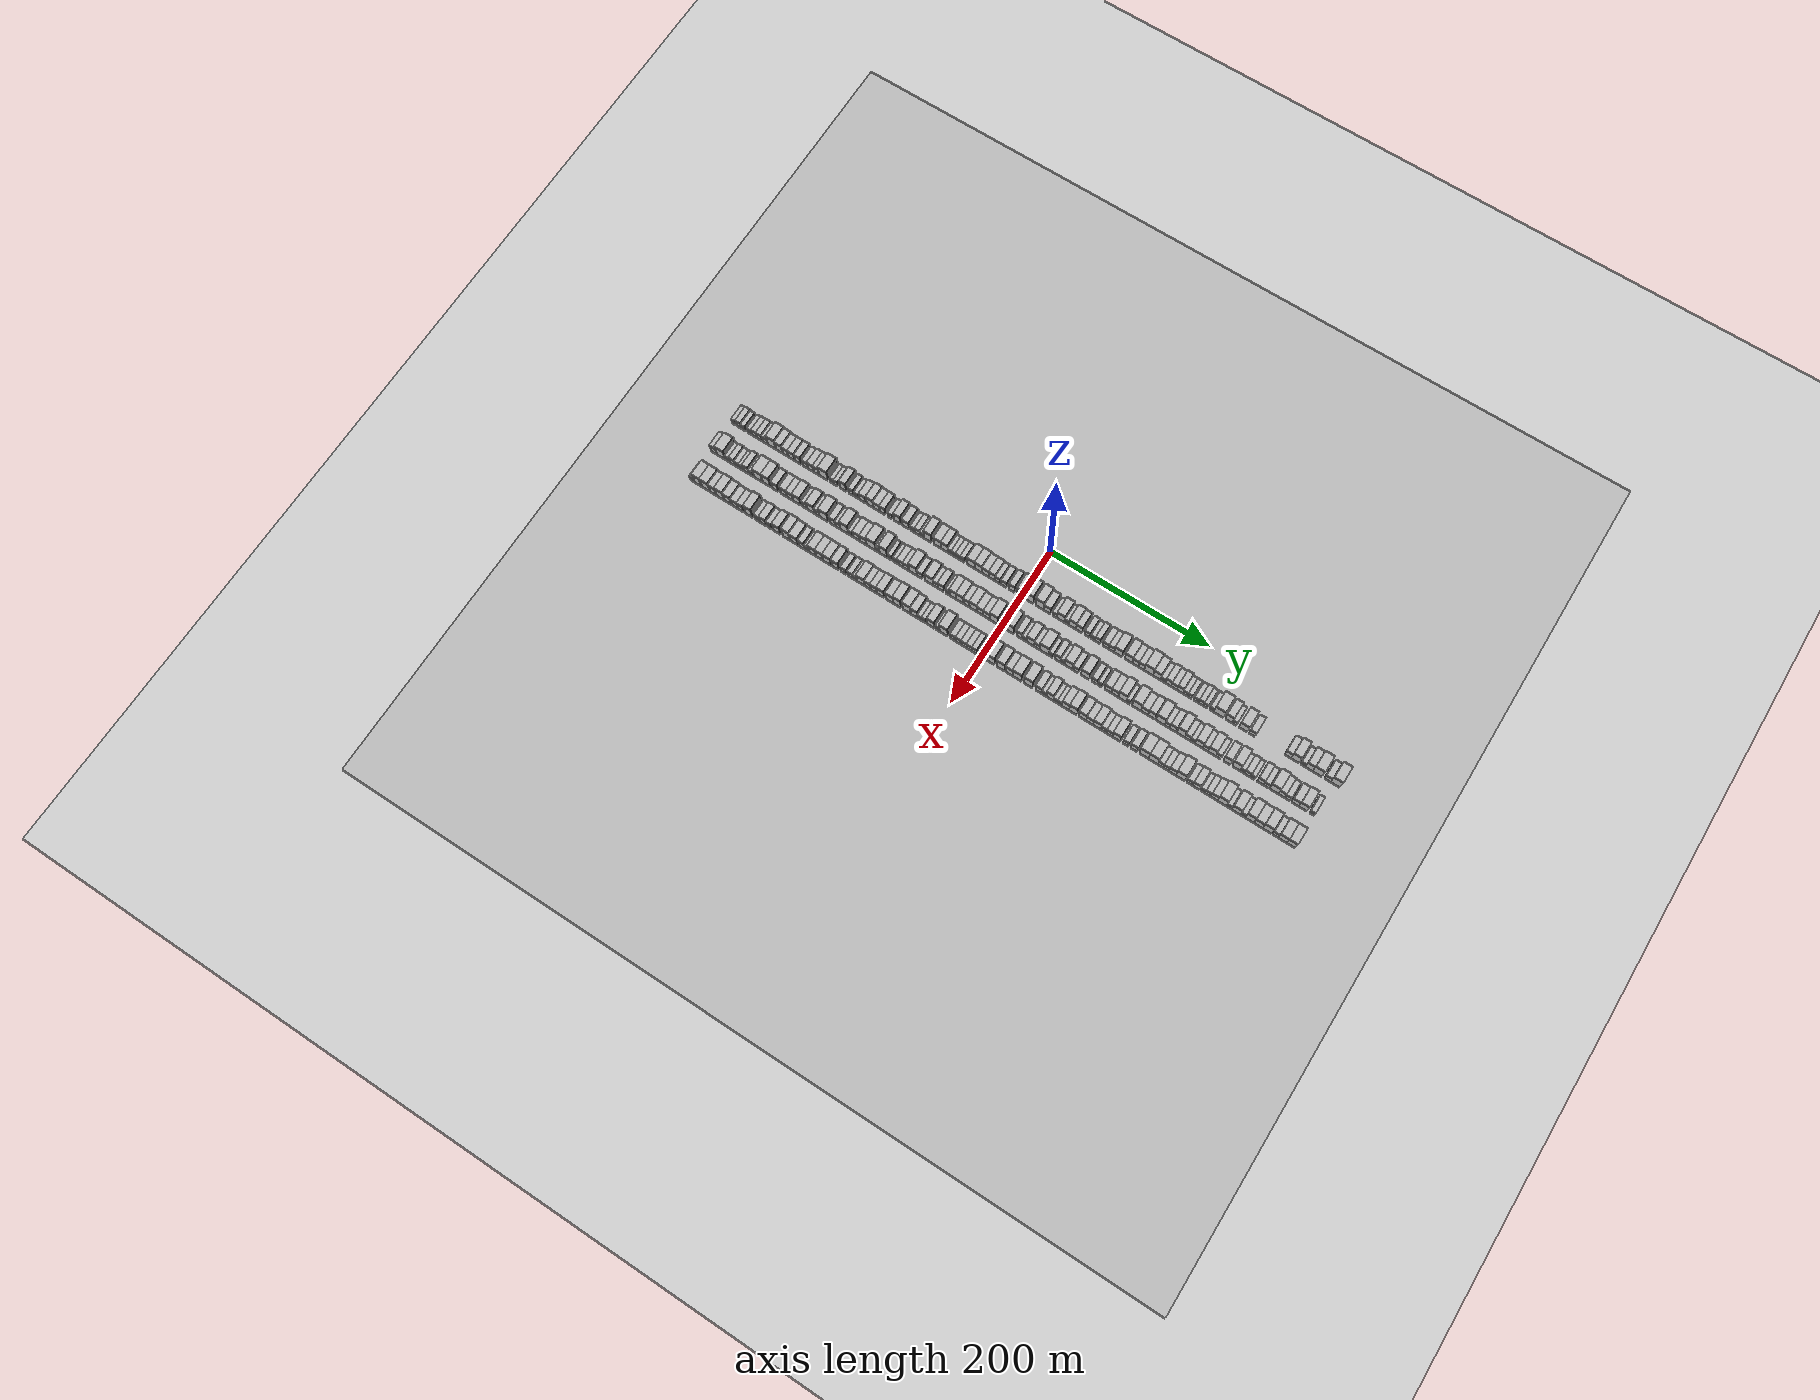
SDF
<?xml version="1.0" encoding="utf-8"?>

<sdf version="1.6">

   <world name="default">

      <gui fullscreen="0">

         <camera name="user_camera">

            <pose>-15 0 4.57585 0 0 0</pose>

            <view_controller>orbit</view_controller>

         </camera>

      </gui>

      <scene>

         <sky>

           <clouds>

             <speed>12</speed>

           </clouds>

         </sky>

         <ambient>0.4 0.4 0.4 1</ambient>

         <background>0.7 0.7 0.7 1</background>

         <shadows>1</shadows>

      </scene>

      <gravity>0 0 -9.8066</gravity>

      <magnetic_field>6e-06 2.3e-05 -4.2e-05</magnetic_field>

      <physics default="0" name="default_physics" type="ode">

         <ode>

            <solver>

               <type>quick</type>

               <iters>10</iters>

               <sor>1.0</sor>

               <use_dynamic_moi_rescaling>0</use_dynamic_moi_rescaling>

            </solver>

            <constraints>

               <cfm>0</cfm>

               <erp>0.2</erp>

               <contact_max_correcting_vel>100</contact_max_correcting_vel>

               <contact_surface_layer>0.001</contact_surface_layer>

            </constraints>

         </ode>

         <max_step_size>0.004</max_step_size>

         <real_time_factor>1</real_time_factor>

         <real_time_update_rate>250</real_time_update_rate>

      </physics>

      <light name="sun" type="directional">

         <cast_shadows>1</cast_shadows>

         <pose>0 0 10 0 0 0</pose>

         <diffuse>0.8 0.8 0.8 1</diffuse>

         <specular>0.2 0.2 0.2 1</specular>

         <attenuation>

            <range>1000</range>

            <constant>0.9</constant>

            <linear>0.01</linear>

            <quadratic>0.001</quadratic>

         </attenuation>

         <direction>-0.5 0.1 -0.9</direction>

      </light>

      <include>

         <name>ground_plane_1</name>

         <uri>model://HANNAS_ground_plane</uri>

         <pose>0 0 0  0 0 0</pose>

      </include>

      <include>

         <name>ground_plane_2</name>

         <uri>model://HANNAS_ground_plane</uri>

         <pose>100 0 0  0 0 0</pose>

      </include>

      <model name="building_1">

         <static>1</static>

         <pose frame="">50.0000 -377.5273 0 0.000000 0.000000 0.000000</pose>

         <link name="link">

            <pose frame="">0 0 6.00 0 0 0</pose>

            <collision name="collision">

               <geometry>

                  <box>

                     <size>20.0000 4.9454 12.0000</size>

                  </box>

               </geometry>

               <max_contacts>10</max_contacts>

               <surface>

                  <contact>

                     <ode/>

                  </contact>

                  <bounce/>

                  <friction>

                     <torsional>

                        <ode/>

                     </torsional>

                     <ode/>

                  </friction>

               </surface>

            </collision>

            <visual name="visual">

               <cast_shadows>0</cast_shadows>

               <geometry>

                  <box>

                     <size>20.0000 4.9454 12.0000</size>

                  </box>

               </geometry>

               <material>

                  <script>

                     <uri>model://HANNAS_wall/materials/scripts</uri>

                     <uri>model://HANNAS_wall/materials/textures</uri>

                     <name>vrc/HANNAS_wall</name>

                  </script>

               </material>

            </visual>

            <self_collide>0</self_collide>

            <enable_wind>0</enable_wind>

            <kinematic>0</kinematic>

         </link>

      </model>

      <model name="building_2">

         <static>1</static>

         <pose frame="">50.0000 -370.7680 0 0.000000 0.000000 0.000000</pose>

         <link name="link">

            <pose frame="">0 0 7.50 0 0 0</pose>

            <collision name="collision">

               <geometry>

                  <box>

                     <size>20.0000 6.5734 15.0000</size>

                  </box>

               </geometry>

               <max_contacts>10</max_contacts>

               <surface>

                  <contact>

                     <ode/>

                  </contact>

                  <bounce/>

                  <friction>

                     <torsional>

                        <ode/>

                     </torsional>

                     <ode/>

                  </friction>

               </surface>

            </collision>

            <visual name="visual">

               <cast_shadows>0</cast_shadows>

               <geometry>

                  <box>

                     <size>20.0000 6.5734 15.0000</size>

                  </box>

               </geometry>

               <material>

                  <script>

                     <uri>model://HANNAS_wall/materials/scripts</uri>

                     <uri>model://HANNAS_wall/materials/textures</uri>

                     <name>vrc/HANNAS_wall</name>

                  </script>

               </material>

            </visual>

            <self_collide>0</self_collide>

            <enable_wind>0</enable_wind>

            <kinematic>0</kinematic>

         </link>

      </model>

      <model name="building_3">

         <static>1</static>

         <pose frame="">50.0000 -364.6494 0 0.000000 0.000000 0.000000</pose>

         <link name="link">

            <pose frame="">0 0 6.00 0 0 0</pose>

            <collision name="collision">

               <geometry>

                  <box>

                     <size>20.0000 5.6638 12.0000</size>

                  </box>

               </geometry>

               <max_contacts>10</max_contacts>

               <surface>

                  <contact>

                     <ode/>

                  </contact>

                  <bounce/>

                  <friction>

                     <torsional>

                        <ode/>

                     </torsional>

                     <ode/>

                  </friction>

               </surface>

            </collision>

            <visual name="visual">

               <cast_shadows>0</cast_shadows>

               <geometry>

                  <box>

                     <size>20.0000 5.6638 12.0000</size>

                  </box>

               </geometry>

               <material>

                  <script>

                     <uri>model://HANNAS_wall/materials/scripts</uri>

                     <uri>model://HANNAS_wall/materials/textures</uri>

                     <name>vrc/HANNAS_wall</name>

                  </script>

               </material>

            </visual>

            <self_collide>0</self_collide>

            <enable_wind>0</enable_wind>

            <kinematic>0</kinematic>

         </link>

      </model>

      <model name="building_4">

         <static>1</static>

         <pose frame="">50.0000 -355.8359 0 0.000000 0.000000 0.000000</pose>

         <link name="link">

            <pose frame="">0 0 6.00 0 0 0</pose>

            <collision name="collision">

               <geometry>

                  <box>

                     <size>20.0000 5.9631 12.0000</size>

                  </box>

               </geometry>

               <max_contacts>10</max_contacts>

               <surface>

                  <contact>

                     <ode/>

                  </contact>

                  <bounce/>

                  <friction>

                     <torsional>

                        <ode/>

                     </torsional>

                     <ode/>

                  </friction>

               </surface>

            </collision>

            <visual name="visual">

               <cast_shadows>0</cast_shadows>

               <geometry>

                  <box>

                     <size>20.0000 5.9631 12.0000</size>

                  </box>

               </geometry>

               <material>

                  <script>

                     <uri>model://HANNAS_wall/materials/scripts</uri>

                     <uri>model://HANNAS_wall/materials/textures</uri>

                     <name>vrc/HANNAS_wall</name>

                  </script>

               </material>

            </visual>

            <self_collide>0</self_collide>

            <enable_wind>0</enable_wind>

            <kinematic>0</kinematic>

         </link>

      </model>

      <model name="building_5">

         <static>1</static>

         <pose frame="">50.0000 -349.7534 0 0.000000 0.000000 0.000000</pose>

         <link name="link">

            <pose frame="">0 0 7.50 0 0 0</pose>

            <collision name="collision">

               <geometry>

                  <box>

                     <size>20.0000 6.2020 15.0000</size>

                  </box>

               </geometry>

               <max_contacts>10</max_contacts>

               <surface>

                  <contact>

                     <ode/>

                  </contact>

                  <bounce/>

                  <friction>

                     <torsional>

                        <ode/>

                     </torsional>

                     <ode/>

                  </friction>

               </surface>

            </collision>

            <visual name="visual">

               <cast_shadows>0</cast_shadows>

               <geometry>

                  <box>

                     <size>20.0000 6.2020 15.0000</size>

                  </box>

               </geometry>

               <material>

                  <script>

                     <uri>model://HANNAS_wall/materials/scripts</uri>

                     <uri>model://HANNAS_wall/materials/textures</uri>

                     <name>vrc/HANNAS_wall</name>

                  </script>

               </material>

            </visual>

            <self_collide>0</self_collide>

            <enable_wind>0</enable_wind>

            <kinematic>0</kinematic>

         </link>

      </model>

      <model name="building_6">

         <static>1</static>

         <pose frame="">50.0000 -343.3390 0 0.000000 0.000000 0.000000</pose>

         <link name="link">

            <pose frame="">0 0 7.50 0 0 0</pose>

            <collision name="collision">

               <geometry>

                  <box>

                     <size>20.0000 6.6268 15.0000</size>

                  </box>

               </geometry>

               <max_contacts>10</max_contacts>

               <surface>

                  <contact>

                     <ode/>

                  </contact>

                  <bounce/>

                  <friction>

                     <torsional>

                        <ode/>

                     </torsional>

                     <ode/>

                  </friction>

               </surface>

            </collision>

            <visual name="visual">

               <cast_shadows>0</cast_shadows>

               <geometry>

                  <box>

                     <size>20.0000 6.6268 15.0000</size>

                  </box>

               </geometry>

               <material>

                  <script>

                     <uri>model://HANNAS_wall/materials/scripts</uri>

                     <uri>model://HANNAS_wall/materials/textures</uri>

                     <name>vrc/HANNAS_wall</name>

                  </script>

               </material>

            </visual>

            <self_collide>0</self_collide>

            <enable_wind>0</enable_wind>

            <kinematic>0</kinematic>

         </link>

      </model>

      <model name="building_7">

         <static>1</static>

         <pose frame="">50.0000 -335.6102 0 0.000000 0.000000 0.000000</pose>

         <link name="link">

            <pose frame="">0 0 7.50 0 0 0</pose>

            <collision name="collision">

               <geometry>

                  <box>

                     <size>20.0000 6.8309 15.0000</size>

                  </box>

               </geometry>

               <max_contacts>10</max_contacts>

               <surface>

                  <contact>

                     <ode/>

                  </contact>

                  <bounce/>

                  <friction>

                     <torsional>

                        <ode/>

                     </torsional>

                     <ode/>

                  </friction>

               </surface>

            </collision>

            <visual name="visual">

               <cast_shadows>0</cast_shadows>

               <geometry>

                  <box>

                     <size>20.0000 6.8309 15.0000</size>

                  </box>

               </geometry>

               <material>

                  <script>

                     <uri>model://HANNAS_wall/materials/scripts</uri>

                     <uri>model://HANNAS_wall/materials/textures</uri>

                     <name>vrc/HANNAS_wall</name>

                  </script>

               </material>

            </visual>

            <self_collide>0</self_collide>

            <enable_wind>0</enable_wind>

            <kinematic>0</kinematic>

         </link>

      </model>

      <model name="building_8">

         <static>1</static>

         <pose frame="">50.0000 -326.6663 0 0.000000 0.000000 0.000000</pose>

         <link name="link">

            <pose frame="">0 0 12.00 0 0 0</pose>

            <collision name="collision">

               <geometry>

                  <box>

                     <size>20.0000 11.0569 24.0000</size>

                  </box>

               </geometry>

               <max_contacts>10</max_contacts>

               <surface>

                  <contact>

                     <ode/>

                  </contact>

                  <bounce/>

                  <friction>

                     <torsional>

                        <ode/>

                     </torsional>

                     <ode/>

                  </friction>

               </surface>

            </collision>

            <visual name="visual">

               <cast_shadows>0</cast_shadows>

               <geometry>

                  <box>

                     <size>20.0000 11.0569 24.0000</size>

                  </box>

               </geometry>

               <material>

                  <script>

                     <uri>model://HANNAS_wall/materials/scripts</uri>

                     <uri>model://HANNAS_wall/materials/textures</uri>

                     <name>vrc/HANNAS_wall</name>

                  </script>

               </material>

            </visual>

            <self_collide>0</self_collide>

            <enable_wind>0</enable_wind>

            <kinematic>0</kinematic>

         </link>

      </model>

      <model name="building_9">

         <static>1</static>

         <pose frame="">50.0000 -316.6502 0 0.000000 0.000000 0.000000</pose>

         <link name="link">

            <pose frame="">0 0 10.50 0 0 0</pose>

            <collision name="collision">

               <geometry>

                  <box>

                     <size>20.0000 8.9752 21.0000</size>

                  </box>

               </geometry>

               <max_contacts>10</max_contacts>

               <surface>

                  <contact>

                     <ode/>

                  </contact>

                  <bounce/>

                  <friction>

                     <torsional>

                        <ode/>

                     </torsional>

                     <ode/>

                  </friction>

               </surface>

            </collision>

            <visual name="visual">

               <cast_shadows>0</cast_shadows>

               <geometry>

                  <box>

                     <size>20.0000 8.9752 21.0000</size>

                  </box>

               </geometry>

               <material>

                  <script>

                     <uri>model://HANNAS_wall/materials/scripts</uri>

                     <uri>model://HANNAS_wall/materials/textures</uri>

                     <name>vrc/HANNAS_wall</name>

                  </script>

               </material>

            </visual>

            <self_collide>0</self_collide>

            <enable_wind>0</enable_wind>

            <kinematic>0</kinematic>

         </link>

      </model>

      <model name="building_10">

         <static>1</static>

         <pose frame="">50.0000 -308.2696 0 0.000000 0.000000 0.000000</pose>

         <link name="link">

            <pose frame="">0 0 9.00 0 0 0</pose>

            <collision name="collision">

               <geometry>

                  <box>

                     <size>20.0000 7.7861 18.0000</size>

                  </box>

               </geometry>

               <max_contacts>10</max_contacts>

               <surface>

                  <contact>

                     <ode/>

                  </contact>

                  <bounce/>

                  <friction>

                     <torsional>

                        <ode/>

                     </torsional>

                     <ode/>

                  </friction>

               </surface>

            </collision>

            <visual name="visual">

               <cast_shadows>0</cast_shadows>

               <geometry>

                  <box>

                     <size>20.0000 7.7861 18.0000</size>

                  </box>

               </geometry>

               <material>

                  <script>

                     <uri>model://HANNAS_wall/materials/scripts</uri>

                     <uri>model://HANNAS_wall/materials/textures</uri>

                     <name>vrc/HANNAS_wall</name>

                  </script>

               </material>

            </visual>

            <self_collide>0</self_collide>

            <enable_wind>0</enable_wind>

            <kinematic>0</kinematic>

         </link>

      </model>

      <model name="building_11">

         <static>1</static>

         <pose frame="">50.0000 -300.3896 0 0.000000 0.000000 0.000000</pose>

         <link name="link">

            <pose frame="">0 0 9.00 0 0 0</pose>

            <collision name="collision">

               <geometry>

                  <box>

                     <size>20.0000 7.9738 18.0000</size>

                  </box>

               </geometry>

               <max_contacts>10</max_contacts>

               <surface>

                  <contact>

                     <ode/>

                  </contact>

                  <bounce/>

                  <friction>

                     <torsional>

                        <ode/>

                     </torsional>

                     <ode/>

                  </friction>

               </surface>

            </collision>

            <visual name="visual">

               <cast_shadows>0</cast_shadows>

               <geometry>

                  <box>

                     <size>20.0000 7.9738 18.0000</size>

                  </box>

               </geometry>

               <material>

                  <script>

                     <uri>model://HANNAS_wall/materials/scripts</uri>

                     <uri>model://HANNAS_wall/materials/textures</uri>

                     <name>vrc/HANNAS_wall</name>

                  </script>

               </material>

            </visual>

            <self_collide>0</self_collide>

            <enable_wind>0</enable_wind>

            <kinematic>0</kinematic>

         </link>

      </model>

      <model name="building_12">

         <static>1</static>

         <pose frame="">50.0000 -291.4953 0 0.000000 0.000000 0.000000</pose>

         <link name="link">

            <pose frame="">0 0 9.00 0 0 0</pose>

            <collision name="collision">

               <geometry>

                  <box>

                     <size>20.0000 7.8147 18.0000</size>

                  </box>

               </geometry>

               <max_contacts>10</max_contacts>

               <surface>

                  <contact>

                     <ode/>

                  </contact>

                  <bounce/>

                  <friction>

                     <torsional>

                        <ode/>

                     </torsional>

                     <ode/>

                  </friction>

               </surface>

            </collision>

            <visual name="visual">

               <cast_shadows>0</cast_shadows>

               <geometry>

                  <box>

                     <size>20.0000 7.8147 18.0000</size>

                  </box>

               </geometry>

               <material>

                  <script>

                     <uri>model://HANNAS_wall/materials/scripts</uri>

                     <uri>model://HANNAS_wall/materials/textures</uri>

                     <name>vrc/HANNAS_wall</name>

                  </script>

               </material>

            </visual>

            <self_collide>0</self_collide>

            <enable_wind>0</enable_wind>

            <kinematic>0</kinematic>

         </link>

      </model>

      <model name="building_13">

         <static>1</static>

         <pose frame="">50.0000 -282.0094 0 0.000000 0.000000 0.000000</pose>

         <link name="link">

            <pose frame="">0 0 7.50 0 0 0</pose>

            <collision name="collision">

               <geometry>

                  <box>

                     <size>20.0000 7.1573 15.0000</size>

                  </box>

               </geometry>

               <max_contacts>10</max_contacts>

               <surface>

                  <contact>

                     <ode/>

                  </contact>

                  <bounce/>

                  <friction>

                     <torsional>

                        <ode/>

                     </torsional>

                     <ode/>

                  </friction>

               </surface>

            </collision>

            <visual name="visual">

               <cast_shadows>0</cast_shadows>

               <geometry>

                  <box>

                     <size>20.0000 7.1573 15.0000</size>

                  </box>

               </geometry>

               <material>

                  <script>

                     <uri>model://HANNAS_wall/materials/scripts</uri>

                     <uri>model://HANNAS_wall/materials/textures</uri>

                     <name>vrc/HANNAS_wall</name>

                  </script>

               </material>

            </visual>

            <self_collide>0</self_collide>

            <enable_wind>0</enable_wind>

            <kinematic>0</kinematic>

         </link>

      </model>

      <model name="building_14">

         <static>1</static>

         <pose frame="">50.0000 -274.5879 0 0.000000 0.000000 0.000000</pose>

         <link name="link">

            <pose frame="">0 0 9.00 0 0 0</pose>

            <collision name="collision">

               <geometry>

                  <box>

                     <size>20.0000 7.6856 18.0000</size>

                  </box>

               </geometry>

               <max_contacts>10</max_contacts>

               <surface>

                  <contact>

                     <ode/>

                  </contact>

                  <bounce/>

                  <friction>

                     <torsional>

                        <ode/>

                     </torsional>

                     <ode/>

                  </friction>

               </surface>

            </collision>

            <visual name="visual">

               <cast_shadows>0</cast_shadows>

               <geometry>

                  <box>

                     <size>20.0000 7.6856 18.0000</size>

                  </box>

               </geometry>

               <material>

                  <script>

                     <uri>model://HANNAS_wall/materials/scripts</uri>

                     <uri>model://HANNAS_wall/materials/textures</uri>

                     <name>vrc/HANNAS_wall</name>

                  </script>

               </material>

            </visual>

            <self_collide>0</self_collide>

            <enable_wind>0</enable_wind>

            <kinematic>0</kinematic>

         </link>

      </model>

      <model name="building_15">

         <static>1</static>

         <pose frame="">50.0000 -267.0893 0 0.000000 0.000000 0.000000</pose>

         <link name="link">

            <pose frame="">0 0 9.00 0 0 0</pose>

            <collision name="collision">

               <geometry>

                  <box>

                     <size>20.0000 7.3118 18.0000</size>

                  </box>

               </geometry>

               <max_contacts>10</max_contacts>

               <surface>

                  <contact>

                     <ode/>

                  </contact>

                  <bounce/>

                  <friction>

                     <torsional>

                        <ode/>

                     </torsional>

                     <ode/>

                  </friction>

               </surface>

            </collision>

            <visual name="visual">

               <cast_shadows>0</cast_shadows>

               <geometry>

                  <box>

                     <size>20.0000 7.3118 18.0000</size>

                  </box>

               </geometry>

               <material>

                  <script>

                     <uri>model://HANNAS_wall/materials/scripts</uri>

                     <uri>model://HANNAS_wall/materials/textures</uri>

                     <name>vrc/HANNAS_wall</name>

                  </script>

               </material>

            </visual>

            <self_collide>0</self_collide>

            <enable_wind>0</enable_wind>

            <kinematic>0</kinematic>

         </link>

      </model>

      <model name="building_16">

         <static>1</static>

         <pose frame="">50.0000 -257.5714 0 0.000000 0.000000 0.000000</pose>

         <link name="link">

            <pose frame="">0 0 12.00 0 0 0</pose>

            <collision name="collision">

               <geometry>

                  <box>

                     <size>20.0000 11.7239 24.0000</size>

                  </box>

               </geometry>

               <max_contacts>10</max_contacts>

               <surface>

                  <contact>

                     <ode/>

                  </contact>

                  <bounce/>

                  <friction>

                     <torsional>

                        <ode/>

                     </torsional>

                     <ode/>

                  </friction>

               </surface>

            </collision>

            <visual name="visual">

               <cast_shadows>0</cast_shadows>

               <geometry>

                  <box>

                     <size>20.0000 11.7239 24.0000</size>

                  </box>

               </geometry>

               <material>

                  <script>

                     <uri>model://HANNAS_wall/materials/scripts</uri>

                     <uri>model://HANNAS_wall/materials/textures</uri>

                     <name>vrc/HANNAS_wall</name>

                  </script>

               </material>

            </visual>

            <self_collide>0</self_collide>

            <enable_wind>0</enable_wind>

            <kinematic>0</kinematic>

         </link>

      </model>

      <model name="building_17">

         <static>1</static>

         <pose frame="">50.0000 -246.2644 0 0.000000 0.000000 0.000000</pose>

         <link name="link">

            <pose frame="">0 0 6.00 0 0 0</pose>

            <collision name="collision">

               <geometry>

                  <box>

                     <size>20.0000 4.8901 12.0000</size>

                  </box>

               </geometry>

               <max_contacts>10</max_contacts>

               <surface>

                  <contact>

                     <ode/>

                  </contact>

                  <bounce/>

                  <friction>

                     <torsional>

                        <ode/>

                     </torsional>

                     <ode/>

                  </friction>

               </surface>

            </collision>

            <visual name="visual">

               <cast_shadows>0</cast_shadows>

               <geometry>

                  <box>

                     <size>20.0000 4.8901 12.0000</size>

                  </box>

               </geometry>

               <material>

                  <script>

                     <uri>model://HANNAS_wall/materials/scripts</uri>

                     <uri>model://HANNAS_wall/materials/textures</uri>

                     <name>vrc/HANNAS_wall</name>

                  </script>

               </material>

            </visual>

            <self_collide>0</self_collide>

            <enable_wind>0</enable_wind>

            <kinematic>0</kinematic>

         </link>

      </model>

      <model name="building_18">

         <static>1</static>

         <pose frame="">50.0000 -241.3413 0 0.000000 0.000000 0.000000</pose>

         <link name="link">

            <pose frame="">0 0 6.00 0 0 0</pose>

            <collision name="collision">

               <geometry>

                  <box>

                     <size>20.0000 4.9562 12.0000</size>

                  </box>

               </geometry>

               <max_contacts>10</max_contacts>

               <surface>

                  <contact>

                     <ode/>

                  </contact>

                  <bounce/>

                  <friction>

                     <torsional>

                        <ode/>

                     </torsional>

                     <ode/>

                  </friction>

               </surface>

            </collision>

            <visual name="visual">

               <cast_shadows>0</cast_shadows>

               <geometry>

                  <box>

                     <size>20.0000 4.9562 12.0000</size>

                  </box>

               </geometry>

               <material>

                  <script>

                     <uri>model://HANNAS_wall/materials/scripts</uri>

                     <uri>model://HANNAS_wall/materials/textures</uri>

                     <name>vrc/HANNAS_wall</name>

                  </script>

               </material>

            </visual>

            <self_collide>0</self_collide>

            <enable_wind>0</enable_wind>

            <kinematic>0</kinematic>

         </link>

      </model>

      <model name="building_19">

         <static>1</static>

         <pose frame="">50.0000 -231.6530 0 0.000000 0.000000 0.000000</pose>

         <link name="link">

            <pose frame="">0 0 10.50 0 0 0</pose>

            <collision name="collision">

               <geometry>

                  <box>

                     <size>20.0000 8.4202 21.0000</size>

                  </box>

               </geometry>

               <max_contacts>10</max_contacts>

               <surface>

                  <contact>

                     <ode/>

                  </contact>

                  <bounce/>

                  <friction>

                     <torsional>

                        <ode/>

                     </torsional>

                     <ode/>

                  </friction>

               </surface>

            </collision>

            <visual name="visual">

               <cast_shadows>0</cast_shadows>

               <geometry>

                  <box>

                     <size>20.0000 8.4202 21.0000</size>

                  </box>

               </geometry>

               <material>

                  <script>

                     <uri>model://HANNAS_wall/materials/scripts</uri>

                     <uri>model://HANNAS_wall/materials/textures</uri>

                     <name>vrc/HANNAS_wall</name>

                  </script>

               </material>

            </visual>

            <self_collide>0</self_collide>

            <enable_wind>0</enable_wind>

            <kinematic>0</kinematic>

         </link>

      </model>

      <model name="building_20">

         <static>1</static>

         <pose frame="">50.0000 -221.2663 0 0.000000 0.000000 0.000000</pose>

         <link name="link">

            <pose frame="">0 0 7.50 0 0 0</pose>

            <collision name="collision">

               <geometry>

                  <box>

                     <size>20.0000 6.3533 15.0000</size>

                  </box>

               </geometry>

               <max_contacts>10</max_contacts>

               <surface>

                  <contact>

                     <ode/>

                  </contact>

                  <bounce/>

                  <friction>

                     <torsional>

                        <ode/>

                     </torsional>

                     <ode/>

                  </friction>

               </surface>

            </collision>

            <visual name="visual">

               <cast_shadows>0</cast_shadows>

               <geometry>

                  <box>

                     <size>20.0000 6.3533 15.0000</size>

                  </box>

               </geometry>

               <material>

                  <script>

                     <uri>model://HANNAS_wall/materials/scripts</uri>

                     <uri>model://HANNAS_wall/materials/textures</uri>

                     <name>vrc/HANNAS_wall</name>

                  </script>

               </material>

            </visual>

            <self_collide>0</self_collide>

            <enable_wind>0</enable_wind>

            <kinematic>0</kinematic>

         </link>

      </model>

      <model name="building_21">

         <static>1</static>

         <pose frame="">50.0000 -214.2123 0 0.000000 0.000000 0.000000</pose>

         <link name="link">

            <pose frame="">0 0 6.00 0 0 0</pose>

            <collision name="collision">

               <geometry>

                  <box>

                     <size>20.0000 5.7547 12.0000</size>

                  </box>

               </geometry>

               <max_contacts>10</max_contacts>

               <surface>

                  <contact>

                     <ode/>

                  </contact>

                  <bounce/>

                  <friction>

                     <torsional>

                        <ode/>

                     </torsional>

                     <ode/>

                  </friction>

               </surface>

            </collision>

            <visual name="visual">

               <cast_shadows>0</cast_shadows>

               <geometry>

                  <box>

                     <size>20.0000 5.7547 12.0000</size>

                  </box>

               </geometry>

               <material>

                  <script>

                     <uri>model://HANNAS_wall/materials/scripts</uri>

                     <uri>model://HANNAS_wall/materials/textures</uri>

                     <name>vrc/HANNAS_wall</name>

                  </script>

               </material>

            </visual>

            <self_collide>0</self_collide>

            <enable_wind>0</enable_wind>

            <kinematic>0</kinematic>

         </link>

      </model>

      <model name="building_22">

         <static>1</static>

         <pose frame="">50.0000 -206.1438 0 0.000000 0.000000 0.000000</pose>

         <link name="link">

            <pose frame="">0 0 9.00 0 0 0</pose>

            <collision name="collision">

               <geometry>

                  <box>

                     <size>20.0000 8.3824 18.0000</size>

                  </box>

               </geometry>

               <max_contacts>10</max_contacts>

               <surface>

                  <contact>

                     <ode/>

                  </contact>

                  <bounce/>

                  <friction>

                     <torsional>

                        <ode/>

                     </torsional>

                     <ode/>

                  </friction>

               </surface>

            </collision>

            <visual name="visual">

               <cast_shadows>0</cast_shadows>

               <geometry>

                  <box>

                     <size>20.0000 8.3824 18.0000</size>

                  </box>

               </geometry>

               <material>

                  <script>

                     <uri>model://HANNAS_wall/materials/scripts</uri>

                     <uri>model://HANNAS_wall/materials/textures</uri>

                     <name>vrc/HANNAS_wall</name>

                  </script>

               </material>

            </visual>

            <self_collide>0</self_collide>

            <enable_wind>0</enable_wind>

            <kinematic>0</kinematic>

         </link>

      </model>

      <model name="building_23">

         <static>1</static>

         <pose frame="">50.0000 -196.3934 0 0.000000 0.000000 0.000000</pose>

         <link name="link">

            <pose frame="">0 0 10.50 0 0 0</pose>

            <collision name="collision">

               <geometry>

                  <box>

                     <size>20.0000 9.1183 21.0000</size>

                  </box>

               </geometry>

               <max_contacts>10</max_contacts>

               <surface>

                  <contact>

                     <ode/>

                  </contact>

                  <bounce/>

                  <friction>

                     <torsional>

                        <ode/>

                     </torsional>

                     <ode/>

                  </friction>

               </surface>

            </collision>

            <visual name="visual">

               <cast_shadows>0</cast_shadows>

               <geometry>

                  <box>

                     <size>20.0000 9.1183 21.0000</size>

                  </box>

               </geometry>

               <material>

                  <script>

                     <uri>model://HANNAS_wall/materials/scripts</uri>

                     <uri>model://HANNAS_wall/materials/textures</uri>

                     <name>vrc/HANNAS_wall</name>

                  </script>

               </material>

            </visual>

            <self_collide>0</self_collide>

            <enable_wind>0</enable_wind>

            <kinematic>0</kinematic>

         </link>

      </model>

      <model name="building_24">

         <static>1</static>

         <pose frame="">50.0000 -187.6576 0 0.000000 0.000000 0.000000</pose>

         <link name="link">

            <pose frame="">0 0 9.00 0 0 0</pose>

            <collision name="collision">

               <geometry>

                  <box>

                     <size>20.0000 8.3534 18.0000</size>

                  </box>

               </geometry>

               <max_contacts>10</max_contacts>

               <surface>

                  <contact>

                     <ode/>

                  </contact>

                  <bounce/>

                  <friction>

                     <torsional>

                        <ode/>

                     </torsional>

                     <ode/>

                  </friction>

               </surface>

            </collision>

            <visual name="visual">

               <cast_shadows>0</cast_shadows>

               <geometry>

                  <box>

                     <size>20.0000 8.3534 18.0000</size>

                  </box>

               </geometry>

               <material>

                  <script>

                     <uri>model://HANNAS_wall/materials/scripts</uri>

                     <uri>model://HANNAS_wall/materials/textures</uri>

                     <name>vrc/HANNAS_wall</name>

                  </script>

               </material>

            </visual>

            <self_collide>0</self_collide>

            <enable_wind>0</enable_wind>

            <kinematic>0</kinematic>

         </link>

      </model>

      <model name="building_25">

         <static>1</static>

         <pose frame="">50.0000 -179.7481 0 0.000000 0.000000 0.000000</pose>

         <link name="link">

            <pose frame="">0 0 9.00 0 0 0</pose>

            <collision name="collision">

               <geometry>

                  <box>

                     <size>20.0000 7.4656 18.0000</size>

                  </box>

               </geometry>

               <max_contacts>10</max_contacts>

               <surface>

                  <contact>

                     <ode/>

                  </contact>

                  <bounce/>

                  <friction>

                     <torsional>

                        <ode/>

                     </torsional>

                     <ode/>

                  </friction>

               </surface>

            </collision>

            <visual name="visual">

               <cast_shadows>0</cast_shadows>

               <geometry>

                  <box>

                     <size>20.0000 7.4656 18.0000</size>

                  </box>

               </geometry>

               <material>

                  <script>

                     <uri>model://HANNAS_wall/materials/scripts</uri>

                     <uri>model://HANNAS_wall/materials/textures</uri>

                     <name>vrc/HANNAS_wall</name>

                  </script>

               </material>

            </visual>

            <self_collide>0</self_collide>

            <enable_wind>0</enable_wind>

            <kinematic>0</kinematic>

         </link>

      </model>

      <model name="building_26">

         <static>1</static>

         <pose frame="">50.0000 -170.0977 0 0.000000 0.000000 0.000000</pose>

         <link name="link">

            <pose frame="">0 0 6.00 0 0 0</pose>

            <collision name="collision">

               <geometry>

                  <box>

                     <size>20.0000 5.8352 12.0000</size>

                  </box>

               </geometry>

               <max_contacts>10</max_contacts>

               <surface>

                  <contact>

                     <ode/>

                  </contact>

                  <bounce/>

                  <friction>

                     <torsional>

                        <ode/>

                     </torsional>

                     <ode/>

                  </friction>

               </surface>

            </collision>

            <visual name="visual">

               <cast_shadows>0</cast_shadows>

               <geometry>

                  <box>

                     <size>20.0000 5.8352 12.0000</size>

                  </box>

               </geometry>

               <material>

                  <script>

                     <uri>model://HANNAS_wall/materials/scripts</uri>

                     <uri>model://HANNAS_wall/materials/textures</uri>

                     <name>vrc/HANNAS_wall</name>

                  </script>

               </material>

            </visual>

            <self_collide>0</self_collide>

            <enable_wind>0</enable_wind>

            <kinematic>0</kinematic>

         </link>

      </model>

      <model name="building_27">

         <static>1</static>

         <pose frame="">50.0000 -160.7447 0 0.000000 0.000000 0.000000</pose>

         <link name="link">

            <pose frame="">0 0 10.50 0 0 0</pose>

            <collision name="collision">

               <geometry>

                  <box>

                     <size>20.0000 8.8708 21.0000</size>

                  </box>

               </geometry>

               <max_contacts>10</max_contacts>

               <surface>

                  <contact>

                     <ode/>

                  </contact>

                  <bounce/>

                  <friction>

                     <torsional>

                        <ode/>

                     </torsional>

                     <ode/>

                  </friction>

               </surface>

            </collision>

            <visual name="visual">

               <cast_shadows>0</cast_shadows>

               <geometry>

                  <box>

                     <size>20.0000 8.8708 21.0000</size>

                  </box>

               </geometry>

               <material>

                  <script>

                     <uri>model://HANNAS_wall/materials/scripts</uri>

                     <uri>model://HANNAS_wall/materials/textures</uri>

                     <name>vrc/HANNAS_wall</name>

                  </script>

               </material>

            </visual>

            <self_collide>0</self_collide>

            <enable_wind>0</enable_wind>

            <kinematic>0</kinematic>

         </link>

      </model>

      <model name="building_28">

         <static>1</static>

         <pose frame="">50.0000 -149.9543 0 0.000000 0.000000 0.000000</pose>

         <link name="link">

            <pose frame="">0 0 9.00 0 0 0</pose>

            <collision name="collision">

               <geometry>

                  <box>

                     <size>20.0000 8.7100 18.0000</size>

                  </box>

               </geometry>

               <max_contacts>10</max_contacts>

               <surface>

                  <contact>

                     <ode/>

                  </contact>

                  <bounce/>

                  <friction>

                     <torsional>

                        <ode/>

                     </torsional>

                     <ode/>

                  </friction>

               </surface>

            </collision>

            <visual name="visual">

               <cast_shadows>0</cast_shadows>

               <geometry>

                  <box>

                     <size>20.0000 8.7100 18.0000</size>

                  </box>

               </geometry>

               <material>

                  <script>

                     <uri>model://HANNAS_wall/materials/scripts</uri>

                     <uri>model://HANNAS_wall/materials/textures</uri>

                     <name>vrc/HANNAS_wall</name>

                  </script>

               </material>

            </visual>

            <self_collide>0</self_collide>

            <enable_wind>0</enable_wind>

            <kinematic>0</kinematic>

         </link>

      </model>

      <model name="building_29">

         <static>1</static>

         <pose frame="">50.0000 -140.6729 0 0.000000 0.000000 0.000000</pose>

         <link name="link">

            <pose frame="">0 0 6.00 0 0 0</pose>

            <collision name="collision">

               <geometry>

                  <box>

                     <size>20.0000 5.8529 12.0000</size>

                  </box>

               </geometry>

               <max_contacts>10</max_contacts>

               <surface>

                  <contact>

                     <ode/>

                  </contact>

                  <bounce/>

                  <friction>

                     <torsional>

                        <ode/>

                     </torsional>

                     <ode/>

                  </friction>

               </surface>

            </collision>

            <visual name="visual">

               <cast_shadows>0</cast_shadows>

               <geometry>

                  <box>

                     <size>20.0000 5.8529 12.0000</size>

                  </box>

               </geometry>

               <material>

                  <script>

                     <uri>model://HANNAS_wall/materials/scripts</uri>

                     <uri>model://HANNAS_wall/materials/textures</uri>

                     <name>vrc/HANNAS_wall</name>

                  </script>

               </material>

            </visual>

            <self_collide>0</self_collide>

            <enable_wind>0</enable_wind>

            <kinematic>0</kinematic>

         </link>

      </model>

      <model name="building_30">

         <static>1</static>

         <pose frame="">50.0000 -134.5189 0 0.000000 0.000000 0.000000</pose>

         <link name="link">

            <pose frame="">0 0 7.50 0 0 0</pose>

            <collision name="collision">

               <geometry>

                  <box>

                     <size>20.0000 6.4551 15.0000</size>

                  </box>

               </geometry>

               <max_contacts>10</max_contacts>

               <surface>

                  <contact>

                     <ode/>

                  </contact>

                  <bounce/>

                  <friction>

                     <torsional>

                        <ode/>

                     </torsional>

                     <ode/>

                  </friction>

               </surface>

            </collision>

            <visual name="visual">

               <cast_shadows>0</cast_shadows>

               <geometry>

                  <box>

                     <size>20.0000 6.4551 15.0000</size>

                  </box>

               </geometry>

               <material>

                  <script>

                     <uri>model://HANNAS_wall/materials/scripts</uri>

                     <uri>model://HANNAS_wall/materials/textures</uri>

                     <name>vrc/HANNAS_wall</name>

                  </script>

               </material>

            </visual>

            <self_collide>0</self_collide>

            <enable_wind>0</enable_wind>

            <kinematic>0</kinematic>

         </link>

      </model>

      <model name="building_31">

         <static>1</static>

         <pose frame="">50.0000 -128.6459 0 0.000000 0.000000 0.000000</pose>

         <link name="link">

            <pose frame="">0 0 6.00 0 0 0</pose>

            <collision name="collision">

               <geometry>

                  <box>

                     <size>20.0000 5.2908 12.0000</size>

                  </box>

               </geometry>

               <max_contacts>10</max_contacts>

               <surface>

                  <contact>

                     <ode/>

                  </contact>

                  <bounce/>

                  <friction>

                     <torsional>

                        <ode/>

                     </torsional>

                     <ode/>

                  </friction>

               </surface>

            </collision>

            <visual name="visual">

               <cast_shadows>0</cast_shadows>

               <geometry>

                  <box>

                     <size>20.0000 5.2908 12.0000</size>

                  </box>

               </geometry>

               <material>

                  <script>

                     <uri>model://HANNAS_wall/materials/scripts</uri>

                     <uri>model://HANNAS_wall/materials/textures</uri>

                     <name>vrc/HANNAS_wall</name>

                  </script>

               </material>

            </visual>

            <self_collide>0</self_collide>

            <enable_wind>0</enable_wind>

            <kinematic>0</kinematic>

         </link>

      </model>

      <model name="building_32">

         <static>1</static>

         <pose frame="">50.0000 -121.1085 0 0.000000 0.000000 0.000000</pose>

         <link name="link">

            <pose frame="">0 0 12.00 0 0 0</pose>

            <collision name="collision">

               <geometry>

                  <box>

                     <size>20.0000 9.7842 24.0000</size>

                  </box>

               </geometry>

               <max_contacts>10</max_contacts>

               <surface>

                  <contact>

                     <ode/>

                  </contact>

                  <bounce/>

                  <friction>

                     <torsional>

                        <ode/>

                     </torsional>

                     <ode/>

                  </friction>

               </surface>

            </collision>

            <visual name="visual">

               <cast_shadows>0</cast_shadows>

               <geometry>

                  <box>

                     <size>20.0000 9.7842 24.0000</size>

                  </box>

               </geometry>

               <material>

                  <script>

                     <uri>model://HANNAS_wall/materials/scripts</uri>

                     <uri>model://HANNAS_wall/materials/textures</uri>

                     <name>vrc/HANNAS_wall</name>

                  </script>

               </material>

            </visual>

            <self_collide>0</self_collide>

            <enable_wind>0</enable_wind>

            <kinematic>0</kinematic>

         </link>

      </model>

      <model name="building_33">

         <static>1</static>

         <pose frame="">50.0000 -108.4735 0 0.000000 0.000000 0.000000</pose>

         <link name="link">

            <pose frame="">0 0 10.50 0 0 0</pose>

            <collision name="collision">

               <geometry>

                  <box>

                     <size>20.0000 9.4856 21.0000</size>

                  </box>

               </geometry>

               <max_contacts>10</max_contacts>

               <surface>

                  <contact>

                     <ode/>

                  </contact>

                  <bounce/>

                  <friction>

                     <torsional>

                        <ode/>

                     </torsional>

                     <ode/>

                  </friction>

               </surface>

            </collision>

            <visual name="visual">

               <cast_shadows>0</cast_shadows>

               <geometry>

                  <box>

                     <size>20.0000 9.4856 21.0000</size>

                  </box>

               </geometry>

               <material>

                  <script>

                     <uri>model://HANNAS_wall/materials/scripts</uri>

                     <uri>model://HANNAS_wall/materials/textures</uri>

                     <name>vrc/HANNAS_wall</name>

                  </script>

               </material>

            </visual>

            <self_collide>0</self_collide>

            <enable_wind>0</enable_wind>

            <kinematic>0</kinematic>

         </link>

      </model>

      <model name="building_34">

         <static>1</static>

         <pose frame="">50.0000 -99.4671 0 0.000000 0.000000 0.000000</pose>

         <link name="link">

            <pose frame="">0 0 10.50 0 0 0</pose>

            <collision name="collision">

               <geometry>

                  <box>

                     <size>20.0000 8.5273 21.0000</size>

                  </box>

               </geometry>

               <max_contacts>10</max_contacts>

               <surface>

                  <contact>

                     <ode/>

                  </contact>

                  <bounce/>

                  <friction>

                     <torsional>

                        <ode/>

                     </torsional>

                     <ode/>

                  </friction>

               </surface>

            </collision>

            <visual name="visual">

               <cast_shadows>0</cast_shadows>

               <geometry>

                  <box>

                     <size>20.0000 8.5273 21.0000</size>

                  </box>

               </geometry>

               <material>

                  <script>

                     <uri>model://HANNAS_wall/materials/scripts</uri>

                     <uri>model://HANNAS_wall/materials/textures</uri>

                     <name>vrc/HANNAS_wall</name>

                  </script>

               </material>

            </visual>

            <self_collide>0</self_collide>

            <enable_wind>0</enable_wind>

            <kinematic>0</kinematic>

         </link>

      </model>

      <model name="building_35">

         <static>1</static>

         <pose frame="">50.0000 -92.8020 0 0.000000 0.000000 0.000000</pose>

         <link name="link">

            <pose frame="">0 0 6.00 0 0 0</pose>

            <collision name="collision">

               <geometry>

                  <box>

                     <size>20.0000 4.8028 12.0000</size>

                  </box>

               </geometry>

               <max_contacts>10</max_contacts>

               <surface>

                  <contact>

                     <ode/>

                  </contact>

                  <bounce/>

                  <friction>

                     <torsional>

                        <ode/>

                     </torsional>

                     <ode/>

                  </friction>

               </surface>

            </collision>

            <visual name="visual">

               <cast_shadows>0</cast_shadows>

               <geometry>

                  <box>

                     <size>20.0000 4.8028 12.0000</size>

                  </box>

               </geometry>

               <material>

                  <script>

                     <uri>model://HANNAS_wall/materials/scripts</uri>

                     <uri>model://HANNAS_wall/materials/textures</uri>

                     <name>vrc/HANNAS_wall</name>

                  </script>

               </material>

            </visual>

            <self_collide>0</self_collide>

            <enable_wind>0</enable_wind>

            <kinematic>0</kinematic>

         </link>

      </model>

      <model name="building_36">

         <static>1</static>

         <pose frame="">50.0000 -87.7829 0 0.000000 0.000000 0.000000</pose>

         <link name="link">

            <pose frame="">0 0 6.00 0 0 0</pose>

            <collision name="collision">

               <geometry>

                  <box>

                     <size>20.0000 5.2355 12.0000</size>

                  </box>

               </geometry>

               <max_contacts>10</max_contacts>

               <surface>

                  <contact>

                     <ode/>

                  </contact>

                  <bounce/>

                  <friction>

                     <torsional>

                        <ode/>

                     </torsional>

                     <ode/>

                  </friction>

               </surface>

            </collision>

            <visual name="visual">

               <cast_shadows>0</cast_shadows>

               <geometry>

                  <box>

                     <size>20.0000 5.2355 12.0000</size>

                  </box>

               </geometry>

               <material>

                  <script>

                     <uri>model://HANNAS_wall/materials/scripts</uri>

                     <uri>model://HANNAS_wall/materials/textures</uri>

                     <name>vrc/HANNAS_wall</name>

                  </script>

               </material>

            </visual>

            <self_collide>0</self_collide>

            <enable_wind>0</enable_wind>

            <kinematic>0</kinematic>

         </link>

      </model>

      <model name="building_37">

         <static>1</static>

         <pose frame="">50.0000 -82.2030 0 0.000000 0.000000 0.000000</pose>

         <link name="link">

            <pose frame="">0 0 6.00 0 0 0</pose>

            <collision name="collision">

               <geometry>

                  <box>

                     <size>20.0000 5.9243 12.0000</size>

                  </box>

               </geometry>

               <max_contacts>10</max_contacts>

               <surface>

                  <contact>

                     <ode/>

                  </contact>

                  <bounce/>

                  <friction>

                     <torsional>

                        <ode/>

                     </torsional>

                     <ode/>

                  </friction>

               </surface>

            </collision>

            <visual name="visual">

               <cast_shadows>0</cast_shadows>

               <geometry>

                  <box>

                     <size>20.0000 5.9243 12.0000</size>

                  </box>

               </geometry>

               <material>

                  <script>

                     <uri>model://HANNAS_wall/materials/scripts</uri>

                     <uri>model://HANNAS_wall/materials/textures</uri>

                     <name>vrc/HANNAS_wall</name>

                  </script>

               </material>

            </visual>

            <self_collide>0</self_collide>

            <enable_wind>0</enable_wind>

            <kinematic>0</kinematic>

         </link>

      </model>

      <model name="building_38">

         <static>1</static>

         <pose frame="">50.0000 -76.2471 0 0.000000 0.000000 0.000000</pose>

         <link name="link">

            <pose frame="">0 0 6.00 0 0 0</pose>

            <collision name="collision">

               <geometry>

                  <box>

                     <size>20.0000 5.9875 12.0000</size>

                  </box>

               </geometry>

               <max_contacts>10</max_contacts>

               <surface>

                  <contact>

                     <ode/>

                  </contact>

                  <bounce/>

                  <friction>

                     <torsional>

                        <ode/>

                     </torsional>

                     <ode/>

                  </friction>

               </surface>

            </collision>

            <visual name="visual">

               <cast_shadows>0</cast_shadows>

               <geometry>

                  <box>

                     <size>20.0000 5.9875 12.0000</size>

                  </box>

               </geometry>

               <material>

                  <script>

                     <uri>model://HANNAS_wall/materials/scripts</uri>

                     <uri>model://HANNAS_wall/materials/textures</uri>

                     <name>vrc/HANNAS_wall</name>

                  </script>

               </material>

            </visual>

            <self_collide>0</self_collide>

            <enable_wind>0</enable_wind>

            <kinematic>0</kinematic>

         </link>

      </model>

      <model name="building_39">

         <static>1</static>

         <pose frame="">50.0000 -65.3838 0 0.000000 0.000000 0.000000</pose>

         <link name="link">

            <pose frame="">0 0 10.50 0 0 0</pose>

            <collision name="collision">

               <geometry>

                  <box>

                     <size>20.0000 9.7389 21.0000</size>

                  </box>

               </geometry>

               <max_contacts>10</max_contacts>

               <surface>

                  <contact>

                     <ode/>

                  </contact>

                  <bounce/>

                  <friction>

                     <torsional>

                        <ode/>

                     </torsional>

                     <ode/>

                  </friction>

               </surface>

            </collision>

            <visual name="visual">

               <cast_shadows>0</cast_shadows>

               <geometry>

                  <box>

                     <size>20.0000 9.7389 21.0000</size>

                  </box>

               </geometry>

               <material>

                  <script>

                     <uri>model://HANNAS_wall/materials/scripts</uri>

                     <uri>model://HANNAS_wall/materials/textures</uri>

                     <name>vrc/HANNAS_wall</name>

                  </script>

               </material>

            </visual>

            <self_collide>0</self_collide>

            <enable_wind>0</enable_wind>

            <kinematic>0</kinematic>

         </link>

      </model>

      <model name="building_40">

         <static>1</static>

         <pose frame="">50.0000 -55.8111 0 0.000000 0.000000 0.000000</pose>

         <link name="link">

            <pose frame="">0 0 10.50 0 0 0</pose>

            <collision name="collision">

               <geometry>

                  <box>

                     <size>20.0000 9.4066 21.0000</size>

                  </box>

               </geometry>

               <max_contacts>10</max_contacts>

               <surface>

                  <contact>

                     <ode/>

                  </contact>

                  <bounce/>

                  <friction>

                     <torsional>

                        <ode/>

                     </torsional>

                     <ode/>

                  </friction>

               </surface>

            </collision>

            <visual name="visual">

               <cast_shadows>0</cast_shadows>

               <geometry>

                  <box>

                     <size>20.0000 9.4066 21.0000</size>

                  </box>

               </geometry>

               <material>

                  <script>

                     <uri>model://HANNAS_wall/materials/scripts</uri>

                     <uri>model://HANNAS_wall/materials/textures</uri>

                     <name>vrc/HANNAS_wall</name>

                  </script>

               </material>

            </visual>

            <self_collide>0</self_collide>

            <enable_wind>0</enable_wind>

            <kinematic>0</kinematic>

         </link>

      </model>

      <model name="building_41">

         <static>1</static>

         <pose frame="">50.0000 -46.9540 0 0.000000 0.000000 0.000000</pose>

         <link name="link">

            <pose frame="">0 0 9.00 0 0 0</pose>

            <collision name="collision">

               <geometry>

                  <box>

                     <size>20.0000 8.3075 18.0000</size>

                  </box>

               </geometry>

               <max_contacts>10</max_contacts>

               <surface>

                  <contact>

                     <ode/>

                  </contact>

                  <bounce/>

                  <friction>

                     <torsional>

                        <ode/>

                     </torsional>

                     <ode/>

                  </friction>

               </surface>

            </collision>

            <visual name="visual">

               <cast_shadows>0</cast_shadows>

               <geometry>

                  <box>

                     <size>20.0000 8.3075 18.0000</size>

                  </box>

               </geometry>

               <material>

                  <script>

                     <uri>model://HANNAS_wall/materials/scripts</uri>

                     <uri>model://HANNAS_wall/materials/textures</uri>

                     <name>vrc/HANNAS_wall</name>

                  </script>

               </material>

            </visual>

            <self_collide>0</self_collide>

            <enable_wind>0</enable_wind>

            <kinematic>0</kinematic>

         </link>

      </model>

      <model name="building_42">

         <static>1</static>

         <pose frame="">50.0000 -38.5774 0 0.000000 0.000000 0.000000</pose>

         <link name="link">

            <pose frame="">0 0 9.00 0 0 0</pose>

            <collision name="collision">

               <geometry>

                  <box>

                     <size>20.0000 8.4458 18.0000</size>

                  </box>

               </geometry>

               <max_contacts>10</max_contacts>

               <surface>

                  <contact>

                     <ode/>

                  </contact>

                  <bounce/>

                  <friction>

                     <torsional>

                        <ode/>

                     </torsional>

                     <ode/>

                  </friction>

               </surface>

            </collision>

            <visual name="visual">

               <cast_shadows>0</cast_shadows>

               <geometry>

                  <box>

                     <size>20.0000 8.4458 18.0000</size>

                  </box>

               </geometry>

               <material>

                  <script>

                     <uri>model://HANNAS_wall/materials/scripts</uri>

                     <uri>model://HANNAS_wall/materials/textures</uri>

                     <name>vrc/HANNAS_wall</name>

                  </script>

               </material>

            </visual>

            <self_collide>0</self_collide>

            <enable_wind>0</enable_wind>

            <kinematic>0</kinematic>

         </link>

      </model>

      <model name="building_43">

         <static>1</static>

         <pose frame="">50.0000 -31.0797 0 0.000000 0.000000 0.000000</pose>

         <link name="link">

            <pose frame="">0 0 7.50 0 0 0</pose>

            <collision name="collision">

               <geometry>

                  <box>

                     <size>20.0000 6.5497 15.0000</size>

                  </box>

               </geometry>

               <max_contacts>10</max_contacts>

               <surface>

                  <contact>

                     <ode/>

                  </contact>

                  <bounce/>

                  <friction>

                     <torsional>

                        <ode/>

                     </torsional>

                     <ode/>

                  </friction>

               </surface>

            </collision>

            <visual name="visual">

               <cast_shadows>0</cast_shadows>

               <geometry>

                  <box>

                     <size>20.0000 6.5497 15.0000</size>

                  </box>

               </geometry>

               <material>

                  <script>

                     <uri>model://HANNAS_wall/materials/scripts</uri>

                     <uri>model://HANNAS_wall/materials/textures</uri>

                     <name>vrc/HANNAS_wall</name>

                  </script>

               </material>

            </visual>

            <self_collide>0</self_collide>

            <enable_wind>0</enable_wind>

            <kinematic>0</kinematic>

         </link>

      </model>

      <model name="building_44">

         <static>1</static>

         <pose frame="">50.0000 -23.2890 0 0.000000 0.000000 0.000000</pose>

         <link name="link">

            <pose frame="">0 0 7.50 0 0 0</pose>

            <collision name="collision">

               <geometry>

                  <box>

                     <size>20.0000 7.0316 15.0000</size>

                  </box>

               </geometry>

               <max_contacts>10</max_contacts>

               <surface>

                  <contact>

                     <ode/>

                  </contact>

                  <bounce/>

                  <friction>

                     <torsional>

                        <ode/>

                     </torsional>

                     <ode/>

                  </friction>

               </surface>

            </collision>

            <visual name="visual">

               <cast_shadows>0</cast_shadows>

               <geometry>

                  <box>

                     <size>20.0000 7.0316 15.0000</size>

                  </box>

               </geometry>

               <material>

                  <script>

                     <uri>model://HANNAS_wall/materials/scripts</uri>

                     <uri>model://HANNAS_wall/materials/textures</uri>

                     <name>vrc/HANNAS_wall</name>

                  </script>

               </material>

            </visual>

            <self_collide>0</self_collide>

            <enable_wind>0</enable_wind>

            <kinematic>0</kinematic>

         </link>

      </model>

      <model name="building_45">

         <static>1</static>

         <pose frame="">50.0000 -13.1310 0 0.000000 0.000000 0.000000</pose>

         <link name="link">

            <pose frame="">0 0 9.00 0 0 0</pose>

            <collision name="collision">

               <geometry>

                  <box>

                     <size>20.0000 7.2844 18.0000</size>

                  </box>

               </geometry>

               <max_contacts>10</max_contacts>

               <surface>

                  <contact>

                     <ode/>

                  </contact>

                  <bounce/>

                  <friction>

                     <torsional>

                        <ode/>

                     </torsional>

                     <ode/>

                  </friction>

               </surface>

            </collision>

            <visual name="visual">

               <cast_shadows>0</cast_shadows>

               <geometry>

                  <box>

                     <size>20.0000 7.2844 18.0000</size>

                  </box>

               </geometry>

               <material>

                  <script>

                     <uri>model://HANNAS_wall/materials/scripts</uri>

                     <uri>model://HANNAS_wall/materials/textures</uri>

                     <name>vrc/HANNAS_wall</name>

                  </script>

               </material>

            </visual>

            <self_collide>0</self_collide>

            <enable_wind>0</enable_wind>

            <kinematic>0</kinematic>

         </link>

      </model>

      <model name="building_46">

         <static>1</static>

         <pose frame="">50.0000 -1.2661 0 0.000000 0.000000 0.000000</pose>

         <link name="link">

            <pose frame="">0 0 10.50 0 0 0</pose>

            <collision name="collision">

               <geometry>

                  <box>

                     <size>20.0000 10.4453 21.0000</size>

                  </box>

               </geometry>

               <max_contacts>10</max_contacts>

               <surface>

                  <contact>

                     <ode/>

                  </contact>

                  <bounce/>

                  <friction>

                     <torsional>

                        <ode/>

                     </torsional>

                     <ode/>

                  </friction>

               </surface>

            </collision>

            <visual name="visual">

               <cast_shadows>0</cast_shadows>

               <geometry>

                  <box>

                     <size>20.0000 10.4453 21.0000</size>

                  </box>

               </geometry>

               <material>

                  <script>

                     <uri>model://HANNAS_wall/materials/scripts</uri>

                     <uri>model://HANNAS_wall/materials/textures</uri>

                     <name>vrc/HANNAS_wall</name>

                  </script>

               </material>

            </visual>

            <self_collide>0</self_collide>

            <enable_wind>0</enable_wind>

            <kinematic>0</kinematic>

         </link>

      </model>

      <model name="building_47">

         <static>1</static>

         <pose frame="">50.0000 9.1413 0 0.000000 0.000000 0.000000</pose>

         <link name="link">

            <pose frame="">0 0 12.00 0 0 0</pose>

            <collision name="collision">

               <geometry>

                  <box>

                     <size>20.0000 10.3695 24.0000</size>

                  </box>

               </geometry>

               <max_contacts>10</max_contacts>

               <surface>

                  <contact>

                     <ode/>

                  </contact>

                  <bounce/>

                  <friction>

                     <torsional>

                        <ode/>

                     </torsional>

                     <ode/>

                  </friction>

               </surface>

            </collision>

            <visual name="visual">

               <cast_shadows>0</cast_shadows>

               <geometry>

                  <box>

                     <size>20.0000 10.3695 24.0000</size>

                  </box>

               </geometry>

               <material>

                  <script>

                     <uri>model://HANNAS_wall/materials/scripts</uri>

                     <uri>model://HANNAS_wall/materials/textures</uri>

                     <name>vrc/HANNAS_wall</name>

                  </script>

               </material>

            </visual>

            <self_collide>0</self_collide>

            <enable_wind>0</enable_wind>

            <kinematic>0</kinematic>

         </link>

      </model>

      <model name="building_48">

         <static>1</static>

         <pose frame="">50.0000 22.5073 0 0.000000 0.000000 0.000000</pose>

         <link name="link">

            <pose frame="">0 0 12.00 0 0 0</pose>

            <collision name="collision">

               <geometry>

                  <box>

                     <size>20.0000 10.3625 24.0000</size>

                  </box>

               </geometry>

               <max_contacts>10</max_contacts>

               <surface>

                  <contact>

                     <ode/>

                  </contact>

                  <bounce/>

                  <friction>

                     <torsional>

                        <ode/>

                     </torsional>

                     <ode/>

                  </friction>

               </surface>

            </collision>

            <visual name="visual">

               <cast_shadows>0</cast_shadows>

               <geometry>

                  <box>

                     <size>20.0000 10.3625 24.0000</size>

                  </box>

               </geometry>

               <material>

                  <script>

                     <uri>model://HANNAS_wall/materials/scripts</uri>

                     <uri>model://HANNAS_wall/materials/textures</uri>

                     <name>vrc/HANNAS_wall</name>

                  </script>

               </material>

            </visual>

            <self_collide>0</self_collide>

            <enable_wind>0</enable_wind>

            <kinematic>0</kinematic>

         </link>

      </model>

      <model name="building_49">

         <static>1</static>

         <pose frame="">50.0000 32.0715 0 0.000000 0.000000 0.000000</pose>

         <link name="link">

            <pose frame="">0 0 9.00 0 0 0</pose>

            <collision name="collision">

               <geometry>

                  <box>

                     <size>20.0000 8.7659 18.0000</size>

                  </box>

               </geometry>

               <max_contacts>10</max_contacts>

               <surface>

                  <contact>

                     <ode/>

                  </contact>

                  <bounce/>

                  <friction>

                     <torsional>

                        <ode/>

                     </torsional>

                     <ode/>

                  </friction>

               </surface>

            </collision>

            <visual name="visual">

               <cast_shadows>0</cast_shadows>

               <geometry>

                  <box>

                     <size>20.0000 8.7659 18.0000</size>

                  </box>

               </geometry>

               <material>

                  <script>

                     <uri>model://HANNAS_wall/materials/scripts</uri>

                     <uri>model://HANNAS_wall/materials/textures</uri>

                     <name>vrc/HANNAS_wall</name>

                  </script>

               </material>

            </visual>

            <self_collide>0</self_collide>

            <enable_wind>0</enable_wind>

            <kinematic>0</kinematic>

         </link>

      </model>

      <model name="building_50">

         <static>1</static>

         <pose frame="">50.0000 41.2767 0 0.000000 0.000000 0.000000</pose>

         <link name="link">

            <pose frame="">0 0 6.00 0 0 0</pose>

            <collision name="collision">

               <geometry>

                  <box>

                     <size>20.0000 5.6445 12.0000</size>

                  </box>

               </geometry>

               <max_contacts>10</max_contacts>

               <surface>

                  <contact>

                     <ode/>

                  </contact>

                  <bounce/>

                  <friction>

                     <torsional>

                        <ode/>

                     </torsional>

                     <ode/>

                  </friction>

               </surface>

            </collision>

            <visual name="visual">

               <cast_shadows>0</cast_shadows>

               <geometry>

                  <box>

                     <size>20.0000 5.6445 12.0000</size>

                  </box>

               </geometry>

               <material>

                  <script>

                     <uri>model://HANNAS_wall/materials/scripts</uri>

                     <uri>model://HANNAS_wall/materials/textures</uri>

                     <name>vrc/HANNAS_wall</name>

                  </script>

               </material>

            </visual>

            <self_collide>0</self_collide>

            <enable_wind>0</enable_wind>

            <kinematic>0</kinematic>

         </link>

      </model>

      <model name="building_51">

         <static>1</static>

         <pose frame="">50.0000 49.0325 0 0.000000 0.000000 0.000000</pose>

         <link name="link">

            <pose frame="">0 0 10.50 0 0 0</pose>

            <collision name="collision">

               <geometry>

                  <box>

                     <size>20.0000 9.8673 21.0000</size>

                  </box>

               </geometry>

               <max_contacts>10</max_contacts>

               <surface>

                  <contact>

                     <ode/>

                  </contact>

                  <bounce/>

                  <friction>

                     <torsional>

                        <ode/>

                     </torsional>

                     <ode/>

                  </friction>

               </surface>

            </collision>

            <visual name="visual">

               <cast_shadows>0</cast_shadows>

               <geometry>

                  <box>

                     <size>20.0000 9.8673 21.0000</size>

                  </box>

               </geometry>

               <material>

                  <script>

                     <uri>model://HANNAS_wall/materials/scripts</uri>

                     <uri>model://HANNAS_wall/materials/textures</uri>

                     <name>vrc/HANNAS_wall</name>

                  </script>

               </material>

            </visual>

            <self_collide>0</self_collide>

            <enable_wind>0</enable_wind>

            <kinematic>0</kinematic>

         </link>

      </model>

      <model name="building_52">

         <static>1</static>

         <pose frame="">50.0000 56.5522 0 0.000000 0.000000 0.000000</pose>

         <link name="link">

            <pose frame="">0 0 6.00 0 0 0</pose>

            <collision name="collision">

               <geometry>

                  <box>

                     <size>20.0000 5.1720 12.0000</size>

                  </box>

               </geometry>

               <max_contacts>10</max_contacts>

               <surface>

                  <contact>

                     <ode/>

                  </contact>

                  <bounce/>

                  <friction>

                     <torsional>

                        <ode/>

                     </torsional>

                     <ode/>

                  </friction>

               </surface>

            </collision>

            <visual name="visual">

               <cast_shadows>0</cast_shadows>

               <geometry>

                  <box>

                     <size>20.0000 5.1720 12.0000</size>

                  </box>

               </geometry>

               <material>

                  <script>

                     <uri>model://HANNAS_wall/materials/scripts</uri>

                     <uri>model://HANNAS_wall/materials/textures</uri>

                     <name>vrc/HANNAS_wall</name>

                  </script>

               </material>

            </visual>

            <self_collide>0</self_collide>

            <enable_wind>0</enable_wind>

            <kinematic>0</kinematic>

         </link>

      </model>

      <model name="building_53">

         <static>1</static>

         <pose frame="">50.0000 63.6290 0 0.000000 0.000000 0.000000</pose>

         <link name="link">

            <pose frame="">0 0 10.50 0 0 0</pose>

            <collision name="collision">

               <geometry>

                  <box>

                     <size>20.0000 8.9818 21.0000</size>

                  </box>

               </geometry>

               <max_contacts>10</max_contacts>

               <surface>

                  <contact>

                     <ode/>

                  </contact>

                  <bounce/>

                  <friction>

                     <torsional>

                        <ode/>

                     </torsional>

                     <ode/>

                  </friction>

               </surface>

            </collision>

            <visual name="visual">

               <cast_shadows>0</cast_shadows>

               <geometry>

                  <box>

                     <size>20.0000 8.9818 21.0000</size>

                  </box>

               </geometry>

               <material>

                  <script>

                     <uri>model://HANNAS_wall/materials/scripts</uri>

                     <uri>model://HANNAS_wall/materials/textures</uri>

                     <name>vrc/HANNAS_wall</name>

                  </script>

               </material>

            </visual>

            <self_collide>0</self_collide>

            <enable_wind>0</enable_wind>

            <kinematic>0</kinematic>

         </link>

      </model>

      <model name="building_54">

         <static>1</static>

         <pose frame="">50.0000 72.0304 0 0.000000 0.000000 0.000000</pose>

         <link name="link">

            <pose frame="">0 0 9.00 0 0 0</pose>

            <collision name="collision">

               <geometry>

                  <box>

                     <size>20.0000 7.8210 18.0000</size>

                  </box>

               </geometry>

               <max_contacts>10</max_contacts>

               <surface>

                  <contact>

                     <ode/>

                  </contact>

                  <bounce/>

                  <friction>

                     <torsional>

                        <ode/>

                     </torsional>

                     <ode/>

                  </friction>

               </surface>

            </collision>

            <visual name="visual">

               <cast_shadows>0</cast_shadows>

               <geometry>

                  <box>

                     <size>20.0000 7.8210 18.0000</size>

                  </box>

               </geometry>

               <material>

                  <script>

                     <uri>model://HANNAS_wall/materials/scripts</uri>

                     <uri>model://HANNAS_wall/materials/textures</uri>

                     <name>vrc/HANNAS_wall</name>

                  </script>

               </material>

            </visual>

            <self_collide>0</self_collide>

            <enable_wind>0</enable_wind>

            <kinematic>0</kinematic>

         </link>

      </model>

      <model name="building_55">

         <static>1</static>

         <pose frame="">50.0000 82.2617 0 0.000000 0.000000 0.000000</pose>

         <link name="link">

            <pose frame="">0 0 7.50 0 0 0</pose>

            <collision name="collision">

               <geometry>

                  <box>

                     <size>20.0000 6.6414 15.0000</size>

                  </box>

               </geometry>

               <max_contacts>10</max_contacts>

               <surface>

                  <contact>

                     <ode/>

                  </contact>

                  <bounce/>

                  <friction>

                     <torsional>

                        <ode/>

                     </torsional>

                     <ode/>

                  </friction>

               </surface>

            </collision>

            <visual name="visual">

               <cast_shadows>0</cast_shadows>

               <geometry>

                  <box>

                     <size>20.0000 6.6414 15.0000</size>

                  </box>

               </geometry>

               <material>

                  <script>

                     <uri>model://HANNAS_wall/materials/scripts</uri>

                     <uri>model://HANNAS_wall/materials/textures</uri>

                     <name>vrc/HANNAS_wall</name>

                  </script>

               </material>

            </visual>

            <self_collide>0</self_collide>

            <enable_wind>0</enable_wind>

            <kinematic>0</kinematic>

         </link>

      </model>

      <model name="building_56">

         <static>1</static>

         <pose frame="">50.0000 89.3755 0 0.000000 0.000000 0.000000</pose>

         <link name="link">

            <pose frame="">0 0 6.00 0 0 0</pose>

            <collision name="collision">

               <geometry>

                  <box>

                     <size>20.0000 5.5863 12.0000</size>

                  </box>

               </geometry>

               <max_contacts>10</max_contacts>

               <surface>

                  <contact>

                     <ode/>

                  </contact>

                  <bounce/>

                  <friction>

                     <torsional>

                        <ode/>

                     </torsional>

                     <ode/>

                  </friction>

               </surface>

            </collision>

            <visual name="visual">

               <cast_shadows>0</cast_shadows>

               <geometry>

                  <box>

                     <size>20.0000 5.5863 12.0000</size>

                  </box>

               </geometry>

               <material>

                  <script>

                     <uri>model://HANNAS_wall/materials/scripts</uri>

                     <uri>model://HANNAS_wall/materials/textures</uri>

                     <name>vrc/HANNAS_wall</name>

                  </script>

               </material>

            </visual>

            <self_collide>0</self_collide>

            <enable_wind>0</enable_wind>

            <kinematic>0</kinematic>

         </link>

      </model>

      <model name="building_57">

         <static>1</static>

         <pose frame="">50.0000 95.4009 0 0.000000 0.000000 0.000000</pose>

         <link name="link">

            <pose frame="">0 0 7.50 0 0 0</pose>

            <collision name="collision">

               <geometry>

                  <box>

                     <size>20.0000 6.4646 15.0000</size>

                  </box>

               </geometry>

               <max_contacts>10</max_contacts>

               <surface>

                  <contact>

                     <ode/>

                  </contact>

                  <bounce/>

                  <friction>

                     <torsional>

                        <ode/>

                     </torsional>

                     <ode/>

                  </friction>

               </surface>

            </collision>

            <visual name="visual">

               <cast_shadows>0</cast_shadows>

               <geometry>

                  <box>

                     <size>20.0000 6.4646 15.0000</size>

                  </box>

               </geometry>

               <material>

                  <script>

                     <uri>model://HANNAS_wall/materials/scripts</uri>

                     <uri>model://HANNAS_wall/materials/textures</uri>

                     <name>vrc/HANNAS_wall</name>

                  </script>

               </material>

            </visual>

            <self_collide>0</self_collide>

            <enable_wind>0</enable_wind>

            <kinematic>0</kinematic>

         </link>

      </model>

      <model name="building_58">

         <static>1</static>

         <pose frame="">50.0000 105.3045 0 0.000000 0.000000 0.000000</pose>

         <link name="link">

            <pose frame="">0 0 7.50 0 0 0</pose>

            <collision name="collision">

               <geometry>

                  <box>

                     <size>20.0000 7.3424 15.0000</size>

                  </box>

               </geometry>

               <max_contacts>10</max_contacts>

               <surface>

                  <contact>

                     <ode/>

                  </contact>

                  <bounce/>

                  <friction>

                     <torsional>

                        <ode/>

                     </torsional>

                     <ode/>

                  </friction>

               </surface>

            </collision>

            <visual name="visual">

               <cast_shadows>0</cast_shadows>

               <geometry>

                  <box>

                     <size>20.0000 7.3424 15.0000</size>

                  </box>

               </geometry>

               <material>

                  <script>

                     <uri>model://HANNAS_wall/materials/scripts</uri>

                     <uri>model://HANNAS_wall/materials/textures</uri>

                     <name>vrc/HANNAS_wall</name>

                  </script>

               </material>

            </visual>

            <self_collide>0</self_collide>

            <enable_wind>0</enable_wind>

            <kinematic>0</kinematic>

         </link>

      </model>

      <model name="building_59">

         <static>1</static>

         <pose frame="">50.0000 112.4464 0 0.000000 0.000000 0.000000</pose>

         <link name="link">

            <pose frame="">0 0 7.50 0 0 0</pose>

            <collision name="collision">

               <geometry>

                  <box>

                     <size>20.0000 6.9415 15.0000</size>

                  </box>

               </geometry>

               <max_contacts>10</max_contacts>

               <surface>

                  <contact>

                     <ode/>

                  </contact>

                  <bounce/>

                  <friction>

                     <torsional>

                        <ode/>

                     </torsional>

                     <ode/>

                  </friction>

               </surface>

            </collision>

            <visual name="visual">

               <cast_shadows>0</cast_shadows>

               <geometry>

                  <box>

                     <size>20.0000 6.9415 15.0000</size>

                  </box>

               </geometry>

               <material>

                  <script>

                     <uri>model://HANNAS_wall/materials/scripts</uri>

                     <uri>model://HANNAS_wall/materials/textures</uri>

                     <name>vrc/HANNAS_wall</name>

                  </script>

               </material>

            </visual>

            <self_collide>0</self_collide>

            <enable_wind>0</enable_wind>

            <kinematic>0</kinematic>

         </link>

      </model>

      <model name="building_60">

         <static>1</static>

         <pose frame="">50.0000 120.9974 0 0.000000 0.000000 0.000000</pose>

         <link name="link">

            <pose frame="">0 0 10.50 0 0 0</pose>

            <collision name="collision">

               <geometry>

                  <box>

                     <size>20.0000 10.1605 21.0000</size>

                  </box>

               </geometry>

               <max_contacts>10</max_contacts>

               <surface>

                  <contact>

                     <ode/>

                  </contact>

                  <bounce/>

                  <friction>

                     <torsional>

                        <ode/>

                     </torsional>

                     <ode/>

                  </friction>

               </surface>

            </collision>

            <visual name="visual">

               <cast_shadows>0</cast_shadows>

               <geometry>

                  <box>

                     <size>20.0000 10.1605 21.0000</size>

                  </box>

               </geometry>

               <material>

                  <script>

                     <uri>model://HANNAS_wall/materials/scripts</uri>

                     <uri>model://HANNAS_wall/materials/textures</uri>

                     <name>vrc/HANNAS_wall</name>

                  </script>

               </material>

            </visual>

            <self_collide>0</self_collide>

            <enable_wind>0</enable_wind>

            <kinematic>0</kinematic>

         </link>

      </model>

      <model name="building_61">

         <static>1</static>

         <pose frame="">50.0000 133.7174 0 0.000000 0.000000 0.000000</pose>

         <link name="link">

            <pose frame="">0 0 10.50 0 0 0</pose>

            <collision name="collision">

               <geometry>

                  <box>

                     <size>20.0000 9.2794 21.0000</size>

                  </box>

               </geometry>

               <max_contacts>10</max_contacts>

               <surface>

                  <contact>

                     <ode/>

                  </contact>

                  <bounce/>

                  <friction>

                     <torsional>

                        <ode/>

                     </torsional>

                     <ode/>

                  </friction>

               </surface>

            </collision>

            <visual name="visual">

               <cast_shadows>0</cast_shadows>

               <geometry>

                  <box>

                     <size>20.0000 9.2794 21.0000</size>

                  </box>

               </geometry>

               <material>

                  <script>

                     <uri>model://HANNAS_wall/materials/scripts</uri>

                     <uri>model://HANNAS_wall/materials/textures</uri>

                     <name>vrc/HANNAS_wall</name>

                  </script>

               </material>

            </visual>

            <self_collide>0</self_collide>

            <enable_wind>0</enable_wind>

            <kinematic>0</kinematic>

         </link>

      </model>

      <model name="building_62">

         <static>1</static>

         <pose frame="">50.0000 142.1484 0 0.000000 0.000000 0.000000</pose>

         <link name="link">

            <pose frame="">0 0 9.00 0 0 0</pose>

            <collision name="collision">

               <geometry>

                  <box>

                     <size>20.0000 7.5827 18.0000</size>

                  </box>

               </geometry>

               <max_contacts>10</max_contacts>

               <surface>

                  <contact>

                     <ode/>

                  </contact>

                  <bounce/>

                  <friction>

                     <torsional>

                        <ode/>

                     </torsional>

                     <ode/>

                  </friction>

               </surface>

            </collision>

            <visual name="visual">

               <cast_shadows>0</cast_shadows>

               <geometry>

                  <box>

                     <size>20.0000 7.5827 18.0000</size>

                  </box>

               </geometry>

               <material>

                  <script>

                     <uri>model://HANNAS_wall/materials/scripts</uri>

                     <uri>model://HANNAS_wall/materials/textures</uri>

                     <name>vrc/HANNAS_wall</name>

                  </script>

               </material>

            </visual>

            <self_collide>0</self_collide>

            <enable_wind>0</enable_wind>

            <kinematic>0</kinematic>

         </link>

      </model>

      <model name="building_63">

         <static>1</static>

         <pose frame="">50.0000 149.6116 0 0.000000 0.000000 0.000000</pose>

         <link name="link">

            <pose frame="">0 0 9.00 0 0 0</pose>

            <collision name="collision">

               <geometry>

                  <box>

                     <size>20.0000 7.3437 18.0000</size>

                  </box>

               </geometry>

               <max_contacts>10</max_contacts>

               <surface>

                  <contact>

                     <ode/>

                  </contact>

                  <bounce/>

                  <friction>

                     <torsional>

                        <ode/>

                     </torsional>

                     <ode/>

                  </friction>

               </surface>

            </collision>

            <visual name="visual">

               <cast_shadows>0</cast_shadows>

               <geometry>

                  <box>

                     <size>20.0000 7.3437 18.0000</size>

                  </box>

               </geometry>

               <material>

                  <script>

                     <uri>model://HANNAS_wall/materials/scripts</uri>

                     <uri>model://HANNAS_wall/materials/textures</uri>

                     <name>vrc/HANNAS_wall</name>

                  </script>

               </material>

            </visual>

            <self_collide>0</self_collide>

            <enable_wind>0</enable_wind>

            <kinematic>0</kinematic>

         </link>

      </model>

      <model name="building_64">

         <static>1</static>

         <pose frame="">50.0000 158.7997 0 0.000000 0.000000 0.000000</pose>

         <link name="link">

            <pose frame="">0 0 12.00 0 0 0</pose>

            <collision name="collision">

               <geometry>

                  <box>

                     <size>20.0000 11.0326 24.0000</size>

                  </box>

               </geometry>

               <max_contacts>10</max_contacts>

               <surface>

                  <contact>

                     <ode/>

                  </contact>

                  <bounce/>

                  <friction>

                     <torsional>

                        <ode/>

                     </torsional>

                     <ode/>

                  </friction>

               </surface>

            </collision>

            <visual name="visual">

               <cast_shadows>0</cast_shadows>

               <geometry>

                  <box>

                     <size>20.0000 11.0326 24.0000</size>

                  </box>

               </geometry>

               <material>

                  <script>

                     <uri>model://HANNAS_wall/materials/scripts</uri>

                     <uri>model://HANNAS_wall/materials/textures</uri>

                     <name>vrc/HANNAS_wall</name>

                  </script>

               </material>

            </visual>

            <self_collide>0</self_collide>

            <enable_wind>0</enable_wind>

            <kinematic>0</kinematic>

         </link>

      </model>

      <model name="building_65">

         <static>1</static>

         <pose frame="">50.0000 168.8379 0 0.000000 0.000000 0.000000</pose>

         <link name="link">

            <pose frame="">0 0 10.50 0 0 0</pose>

            <collision name="collision">

               <geometry>

                  <box>

                     <size>20.0000 9.0439 21.0000</size>

                  </box>

               </geometry>

               <max_contacts>10</max_contacts>

               <surface>

                  <contact>

                     <ode/>

                  </contact>

                  <bounce/>

                  <friction>

                     <torsional>

                        <ode/>

                     </torsional>

                     <ode/>

                  </friction>

               </surface>

            </collision>

            <visual name="visual">

               <cast_shadows>0</cast_shadows>

               <geometry>

                  <box>

                     <size>20.0000 9.0439 21.0000</size>

                  </box>

               </geometry>

               <material>

                  <script>

                     <uri>model://HANNAS_wall/materials/scripts</uri>

                     <uri>model://HANNAS_wall/materials/textures</uri>

                     <name>vrc/HANNAS_wall</name>

                  </script>

               </material>

            </visual>

            <self_collide>0</self_collide>

            <enable_wind>0</enable_wind>

            <kinematic>0</kinematic>

         </link>

      </model>

      <model name="building_66">

         <static>1</static>

         <pose frame="">50.0000 176.3385 0 0.000000 0.000000 0.000000</pose>

         <link name="link">

            <pose frame="">0 0 6.00 0 0 0</pose>

            <collision name="collision">

               <geometry>

                  <box>

                     <size>20.0000 5.9573 12.0000</size>

                  </box>

               </geometry>

               <max_contacts>10</max_contacts>

               <surface>

                  <contact>

                     <ode/>

                  </contact>

                  <bounce/>

                  <friction>

                     <torsional>

                        <ode/>

                     </torsional>

                     <ode/>

                  </friction>

               </surface>

            </collision>

            <visual name="visual">

               <cast_shadows>0</cast_shadows>

               <geometry>

                  <box>

                     <size>20.0000 5.9573 12.0000</size>

                  </box>

               </geometry>

               <material>

                  <script>

                     <uri>model://HANNAS_wall/materials/scripts</uri>

                     <uri>model://HANNAS_wall/materials/textures</uri>

                     <name>vrc/HANNAS_wall</name>

                  </script>

               </material>

            </visual>

            <self_collide>0</self_collide>

            <enable_wind>0</enable_wind>

            <kinematic>0</kinematic>

         </link>

      </model>

      <model name="building_67">

         <static>1</static>

         <pose frame="">50.0000 182.9283 0 0.000000 0.000000 0.000000</pose>

         <link name="link">

            <pose frame="">0 0 9.00 0 0 0</pose>

            <collision name="collision">

               <geometry>

                  <box>

                     <size>20.0000 7.2224 18.0000</size>

                  </box>

               </geometry>

               <max_contacts>10</max_contacts>

               <surface>

                  <contact>

                     <ode/>

                  </contact>

                  <bounce/>

                  <friction>

                     <torsional>

                        <ode/>

                     </torsional>

                     <ode/>

                  </friction>

               </surface>

            </collision>

            <visual name="visual">

               <cast_shadows>0</cast_shadows>

               <geometry>

                  <box>

                     <size>20.0000 7.2224 18.0000</size>

                  </box>

               </geometry>

               <material>

                  <script>

                     <uri>model://HANNAS_wall/materials/scripts</uri>

                     <uri>model://HANNAS_wall/materials/textures</uri>

                     <name>vrc/HANNAS_wall</name>

                  </script>

               </material>

            </visual>

            <self_collide>0</self_collide>

            <enable_wind>0</enable_wind>

            <kinematic>0</kinematic>

         </link>

      </model>

      <model name="building_68">

         <static>1</static>

         <pose frame="">50.0000 190.0364 0 0.000000 0.000000 0.000000</pose>

         <link name="link">

            <pose frame="">0 0 7.50 0 0 0</pose>

            <collision name="collision">

               <geometry>

                  <box>

                     <size>20.0000 6.9937 15.0000</size>

                  </box>

               </geometry>

               <max_contacts>10</max_contacts>

               <surface>

                  <contact>

                     <ode/>

                  </contact>

                  <bounce/>

                  <friction>

                     <torsional>

                        <ode/>

                     </torsional>

                     <ode/>

                  </friction>

               </surface>

            </collision>

            <visual name="visual">

               <cast_shadows>0</cast_shadows>

               <geometry>

                  <box>

                     <size>20.0000 6.9937 15.0000</size>

                  </box>

               </geometry>

               <material>

                  <script>

                     <uri>model://HANNAS_wall/materials/scripts</uri>

                     <uri>model://HANNAS_wall/materials/textures</uri>

                     <name>vrc/HANNAS_wall</name>

                  </script>

               </material>

            </visual>

            <self_collide>0</self_collide>

            <enable_wind>0</enable_wind>

            <kinematic>0</kinematic>

         </link>

      </model>

      <model name="building_69">

         <static>1</static>

         <pose frame="">50.0000 197.2287 0 0.000000 0.000000 0.000000</pose>

         <link name="link">

            <pose frame="">0 0 9.00 0 0 0</pose>

            <collision name="collision">

               <geometry>

                  <box>

                     <size>20.0000 7.3910 18.0000</size>

                  </box>

               </geometry>

               <max_contacts>10</max_contacts>

               <surface>

                  <contact>

                     <ode/>

                  </contact>

                  <bounce/>

                  <friction>

                     <torsional>

                        <ode/>

                     </torsional>

                     <ode/>

                  </friction>

               </surface>

            </collision>

            <visual name="visual">

               <cast_shadows>0</cast_shadows>

               <geometry>

                  <box>

                     <size>20.0000 7.3910 18.0000</size>

                  </box>

               </geometry>

               <material>

                  <script>

                     <uri>model://HANNAS_wall/materials/scripts</uri>

                     <uri>model://HANNAS_wall/materials/textures</uri>

                     <name>vrc/HANNAS_wall</name>

                  </script>

               </material>

            </visual>

            <self_collide>0</self_collide>

            <enable_wind>0</enable_wind>

            <kinematic>0</kinematic>

         </link>

      </model>

      <model name="building_70">

         <static>1</static>

         <pose frame="">50.0000 203.7685 0 0.000000 0.000000 0.000000</pose>

         <link name="link">

            <pose frame="">0 0 6.00 0 0 0</pose>

            <collision name="collision">

               <geometry>

                  <box>

                     <size>20.0000 5.6885 12.0000</size>

                  </box>

               </geometry>

               <max_contacts>10</max_contacts>

               <surface>

                  <contact>

                     <ode/>

                  </contact>

                  <bounce/>

                  <friction>

                     <torsional>

                        <ode/>

                     </torsional>

                     <ode/>

                  </friction>

               </surface>

            </collision>

            <visual name="visual">

               <cast_shadows>0</cast_shadows>

               <geometry>

                  <box>

                     <size>20.0000 5.6885 12.0000</size>

                  </box>

               </geometry>

               <material>

                  <script>

                     <uri>model://HANNAS_wall/materials/scripts</uri>

                     <uri>model://HANNAS_wall/materials/textures</uri>

                     <name>vrc/HANNAS_wall</name>

                  </script>

               </material>

            </visual>

            <self_collide>0</self_collide>

            <enable_wind>0</enable_wind>

            <kinematic>0</kinematic>

         </link>

      </model>

      <model name="building_71">

         <static>1</static>

         <pose frame="">50.0000 209.4373 0 0.000000 0.000000 0.000000</pose>

         <link name="link">

            <pose frame="">0 0 6.00 0 0 0</pose>

            <collision name="collision">

               <geometry>

                  <box>

                     <size>20.0000 5.6490 12.0000</size>

                  </box>

               </geometry>

               <max_contacts>10</max_contacts>

               <surface>

                  <contact>

                     <ode/>

                  </contact>

                  <bounce/>

                  <friction>

                     <torsional>

                        <ode/>

                     </torsional>

                     <ode/>

                  </friction>

               </surface>

            </collision>

            <visual name="visual">

               <cast_shadows>0</cast_shadows>

               <geometry>

                  <box>

                     <size>20.0000 5.6490 12.0000</size>

                  </box>

               </geometry>

               <material>

                  <script>

                     <uri>model://HANNAS_wall/materials/scripts</uri>

                     <uri>model://HANNAS_wall/materials/textures</uri>

                     <name>vrc/HANNAS_wall</name>

                  </script>

               </material>

            </visual>

            <self_collide>0</self_collide>

            <enable_wind>0</enable_wind>

            <kinematic>0</kinematic>

         </link>

      </model>

      <model name="building_72">

         <static>1</static>

         <pose frame="">50.0000 217.1640 0 0.000000 0.000000 0.000000</pose>

         <link name="link">

            <pose frame="">0 0 6.00 0 0 0</pose>

            <collision name="collision">

               <geometry>

                  <box>

                     <size>20.0000 5.8044 12.0000</size>

                  </box>

               </geometry>

               <max_contacts>10</max_contacts>

               <surface>

                  <contact>

                     <ode/>

                  </contact>

                  <bounce/>

                  <friction>

                     <torsional>

                        <ode/>

                     </torsional>

                     <ode/>

                  </friction>

               </surface>

            </collision>

            <visual name="visual">

               <cast_shadows>0</cast_shadows>

               <geometry>

                  <box>

                     <size>20.0000 5.8044 12.0000</size>

                  </box>

               </geometry>

               <material>

                  <script>

                     <uri>model://HANNAS_wall/materials/scripts</uri>

                     <uri>model://HANNAS_wall/materials/textures</uri>

                     <name>vrc/HANNAS_wall</name>

                  </script>

               </material>

            </visual>

            <self_collide>0</self_collide>

            <enable_wind>0</enable_wind>

            <kinematic>0</kinematic>

         </link>

      </model>

      <model name="building_73">

         <static>1</static>

         <pose frame="">50.0000 223.1443 0 0.000000 0.000000 0.000000</pose>

         <link name="link">

            <pose frame="">0 0 7.50 0 0 0</pose>

            <collision name="collision">

               <geometry>

                  <box>

                     <size>20.0000 6.1561 15.0000</size>

                  </box>

               </geometry>

               <max_contacts>10</max_contacts>

               <surface>

                  <contact>

                     <ode/>

                  </contact>

                  <bounce/>

                  <friction>

                     <torsional>

                        <ode/>

                     </torsional>

                     <ode/>

                  </friction>

               </surface>

            </collision>

            <visual name="visual">

               <cast_shadows>0</cast_shadows>

               <geometry>

                  <box>

                     <size>20.0000 6.1561 15.0000</size>

                  </box>

               </geometry>

               <material>

                  <script>

                     <uri>model://HANNAS_wall/materials/scripts</uri>

                     <uri>model://HANNAS_wall/materials/textures</uri>

                     <name>vrc/HANNAS_wall</name>

                  </script>

               </material>

            </visual>

            <self_collide>0</self_collide>

            <enable_wind>0</enable_wind>

            <kinematic>0</kinematic>

         </link>

      </model>

      <model name="building_74">

         <static>1</static>

         <pose frame="">50.0000 228.8796 0 0.000000 0.000000 0.000000</pose>

         <link name="link">

            <pose frame="">0 0 6.00 0 0 0</pose>

            <collision name="collision">

               <geometry>

                  <box>

                     <size>20.0000 5.3145 12.0000</size>

                  </box>

               </geometry>

               <max_contacts>10</max_contacts>

               <surface>

                  <contact>

                     <ode/>

                  </contact>

                  <bounce/>

                  <friction>

                     <torsional>

                        <ode/>

                     </torsional>

                     <ode/>

                  </friction>

               </surface>

            </collision>

            <visual name="visual">

               <cast_shadows>0</cast_shadows>

               <geometry>

                  <box>

                     <size>20.0000 5.3145 12.0000</size>

                  </box>

               </geometry>

               <material>

                  <script>

                     <uri>model://HANNAS_wall/materials/scripts</uri>

                     <uri>model://HANNAS_wall/materials/textures</uri>

                     <name>vrc/HANNAS_wall</name>

                  </script>

               </material>

            </visual>

            <self_collide>0</self_collide>

            <enable_wind>0</enable_wind>

            <kinematic>0</kinematic>

         </link>

      </model>

      <model name="building_75">

         <static>1</static>

         <pose frame="">50.0000 236.1884 0 0.000000 0.000000 0.000000</pose>

         <link name="link">

            <pose frame="">0 0 6.00 0 0 0</pose>

            <collision name="collision">

               <geometry>

                  <box>

                     <size>20.0000 5.3031 12.0000</size>

                  </box>

               </geometry>

               <max_contacts>10</max_contacts>

               <surface>

                  <contact>

                     <ode/>

                  </contact>

                  <bounce/>

                  <friction>

                     <torsional>

                        <ode/>

                     </torsional>

                     <ode/>

                  </friction>

               </surface>

            </collision>

            <visual name="visual">

               <cast_shadows>0</cast_shadows>

               <geometry>

                  <box>

                     <size>20.0000 5.3031 12.0000</size>

                  </box>

               </geometry>

               <material>

                  <script>

                     <uri>model://HANNAS_wall/materials/scripts</uri>

                     <uri>model://HANNAS_wall/materials/textures</uri>

                     <name>vrc/HANNAS_wall</name>

                  </script>

               </material>

            </visual>

            <self_collide>0</self_collide>

            <enable_wind>0</enable_wind>

            <kinematic>0</kinematic>

         </link>

      </model>

      <model name="building_76">

         <static>1</static>

         <pose frame="">50.0000 244.7735 0 0.000000 0.000000 0.000000</pose>

         <link name="link">

            <pose frame="">0 0 12.00 0 0 0</pose>

            <collision name="collision">

               <geometry>

                  <box>

                     <size>20.0000 11.8672 24.0000</size>

                  </box>

               </geometry>

               <max_contacts>10</max_contacts>

               <surface>

                  <contact>

                     <ode/>

                  </contact>

                  <bounce/>

                  <friction>

                     <torsional>

                        <ode/>

                     </torsional>

                     <ode/>

                  </friction>

               </surface>

            </collision>

            <visual name="visual">

               <cast_shadows>0</cast_shadows>

               <geometry>

                  <box>

                     <size>20.0000 11.8672 24.0000</size>

                  </box>

               </geometry>

               <material>

                  <script>

                     <uri>model://HANNAS_wall/materials/scripts</uri>

                     <uri>model://HANNAS_wall/materials/textures</uri>

                     <name>vrc/HANNAS_wall</name>

                  </script>

               </material>

            </visual>

            <self_collide>0</self_collide>

            <enable_wind>0</enable_wind>

            <kinematic>0</kinematic>

         </link>

      </model>

      <model name="building_77">

         <static>1</static>

         <pose frame="">50.0000 256.9779 0 0.000000 0.000000 0.000000</pose>

         <link name="link">

            <pose frame="">0 0 10.50 0 0 0</pose>

            <collision name="collision">

               <geometry>

                  <box>

                     <size>20.0000 8.5415 21.0000</size>

                  </box>

               </geometry>

               <max_contacts>10</max_contacts>

               <surface>

                  <contact>

                     <ode/>

                  </contact>

                  <bounce/>

                  <friction>

                     <torsional>

                        <ode/>

                     </torsional>

                     <ode/>

                  </friction>

               </surface>

            </collision>

            <visual name="visual">

               <cast_shadows>0</cast_shadows>

               <geometry>

                  <box>

                     <size>20.0000 8.5415 21.0000</size>

                  </box>

               </geometry>

               <material>

                  <script>

                     <uri>model://HANNAS_wall/materials/scripts</uri>

                     <uri>model://HANNAS_wall/materials/textures</uri>

                     <name>vrc/HANNAS_wall</name>

                  </script>

               </material>

            </visual>

            <self_collide>0</self_collide>

            <enable_wind>0</enable_wind>

            <kinematic>0</kinematic>

         </link>

      </model>

      <model name="building_78">

         <static>1</static>

         <pose frame="">50.0000 263.9040 0 0.000000 0.000000 0.000000</pose>

         <link name="link">

            <pose frame="">0 0 6.00 0 0 0</pose>

            <collision name="collision">

               <geometry>

                  <box>

                     <size>20.0000 5.3107 12.0000</size>

                  </box>

               </geometry>

               <max_contacts>10</max_contacts>

               <surface>

                  <contact>

                     <ode/>

                  </contact>

                  <bounce/>

                  <friction>

                     <torsional>

                        <ode/>

                     </torsional>

                     <ode/>

                  </friction>

               </surface>

            </collision>

            <visual name="visual">

               <cast_shadows>0</cast_shadows>

               <geometry>

                  <box>

                     <size>20.0000 5.3107 12.0000</size>

                  </box>

               </geometry>

               <material>

                  <script>

                     <uri>model://HANNAS_wall/materials/scripts</uri>

                     <uri>model://HANNAS_wall/materials/textures</uri>

                     <name>vrc/HANNAS_wall</name>

                  </script>

               </material>

            </visual>

            <self_collide>0</self_collide>

            <enable_wind>0</enable_wind>

            <kinematic>0</kinematic>

         </link>

      </model>

      <model name="building_79">

         <static>1</static>

         <pose frame="">50.0000 274.6052 0 0.000000 0.000000 0.000000</pose>

         <link name="link">

            <pose frame="">0 0 10.50 0 0 0</pose>

            <collision name="collision">

               <geometry>

                  <box>

                     <size>20.0000 10.0915 21.0000</size>

                  </box>

               </geometry>

               <max_contacts>10</max_contacts>

               <surface>

                  <contact>

                     <ode/>

                  </contact>

                  <bounce/>

                  <friction>

                     <torsional>

                        <ode/>

                     </torsional>

                     <ode/>

                  </friction>

               </surface>

            </collision>

            <visual name="visual">

               <cast_shadows>0</cast_shadows>

               <geometry>

                  <box>

                     <size>20.0000 10.0915 21.0000</size>

                  </box>

               </geometry>

               <material>

                  <script>

                     <uri>model://HANNAS_wall/materials/scripts</uri>

                     <uri>model://HANNAS_wall/materials/textures</uri>

                     <name>vrc/HANNAS_wall</name>

                  </script>

               </material>

            </visual>

            <self_collide>0</self_collide>

            <enable_wind>0</enable_wind>

            <kinematic>0</kinematic>

         </link>

      </model>

      <model name="building_80">

         <static>1</static>

         <pose frame="">50.0000 285.3946 0 0.000000 0.000000 0.000000</pose>

         <link name="link">

            <pose frame="">0 0 7.50 0 0 0</pose>

            <collision name="collision">

               <geometry>

                  <box>

                     <size>20.0000 7.4874 15.0000</size>

                  </box>

               </geometry>

               <max_contacts>10</max_contacts>

               <surface>

                  <contact>

                     <ode/>

                  </contact>

                  <bounce/>

                  <friction>

                     <torsional>

                        <ode/>

                     </torsional>

                     <ode/>

                  </friction>

               </surface>

            </collision>

            <visual name="visual">

               <cast_shadows>0</cast_shadows>

               <geometry>

                  <box>

                     <size>20.0000 7.4874 15.0000</size>

                  </box>

               </geometry>

               <material>

                  <script>

                     <uri>model://HANNAS_wall/materials/scripts</uri>

                     <uri>model://HANNAS_wall/materials/textures</uri>

                     <name>vrc/HANNAS_wall</name>

                  </script>

               </material>

            </visual>

            <self_collide>0</self_collide>

            <enable_wind>0</enable_wind>

            <kinematic>0</kinematic>

         </link>

      </model>

      <model name="building_81">

         <static>1</static>

         <pose frame="">50.0000 328.4054 0 0.000000 0.000000 0.000000</pose>

         <link name="link">

            <pose frame="">0 0 9.00 0 0 0</pose>

            <collision name="collision">

               <geometry>

                  <box>

                     <size>20.0000 7.5114 18.0000</size>

                  </box>

               </geometry>

               <max_contacts>10</max_contacts>

               <surface>

                  <contact>

                     <ode/>

                  </contact>

                  <bounce/>

                  <friction>

                     <torsional>

                        <ode/>

                     </torsional>

                     <ode/>

                  </friction>

               </surface>

            </collision>

            <visual name="visual">

               <cast_shadows>0</cast_shadows>

               <geometry>

                  <box>

                     <size>20.0000 7.5114 18.0000</size>

                  </box>

               </geometry>

               <material>

                  <script>

                     <uri>model://HANNAS_wall/materials/scripts</uri>

                     <uri>model://HANNAS_wall/materials/textures</uri>

                     <name>vrc/HANNAS_wall</name>

                  </script>

               </material>

            </visual>

            <self_collide>0</self_collide>

            <enable_wind>0</enable_wind>

            <kinematic>0</kinematic>

         </link>

      </model>

      <model name="building_82">

         <static>1</static>

         <pose frame="">50.0000 336.9663 0 0.000000 0.000000 0.000000</pose>

         <link name="link">

            <pose frame="">0 0 12.00 0 0 0</pose>

            <collision name="collision">

               <geometry>

                  <box>

                     <size>20.0000 9.6104 24.0000</size>

                  </box>

               </geometry>

               <max_contacts>10</max_contacts>

               <surface>

                  <contact>

                     <ode/>

                  </contact>

                  <bounce/>

                  <friction>

                     <torsional>

                        <ode/>

                     </torsional>

                     <ode/>

                  </friction>

               </surface>

            </collision>

            <visual name="visual">

               <cast_shadows>0</cast_shadows>

               <geometry>

                  <box>

                     <size>20.0000 9.6104 24.0000</size>

                  </box>

               </geometry>

               <material>

                  <script>

                     <uri>model://HANNAS_wall/materials/scripts</uri>

                     <uri>model://HANNAS_wall/materials/textures</uri>

                     <name>vrc/HANNAS_wall</name>

                  </script>

               </material>

            </visual>

            <self_collide>0</self_collide>

            <enable_wind>0</enable_wind>

            <kinematic>0</kinematic>

         </link>

      </model>

      <model name="building_83">

         <static>1</static>

         <pose frame="">50.0000 346.6145 0 0.000000 0.000000 0.000000</pose>

         <link name="link">

            <pose frame="">0 0 6.00 0 0 0</pose>

            <collision name="collision">

               <geometry>

                  <box>

                     <size>20.0000 5.6861 12.0000</size>

                  </box>

               </geometry>

               <max_contacts>10</max_contacts>

               <surface>

                  <contact>

                     <ode/>

                  </contact>

                  <bounce/>

                  <friction>

                     <torsional>

                        <ode/>

                     </torsional>

                     <ode/>

                  </friction>

               </surface>

            </collision>

            <visual name="visual">

               <cast_shadows>0</cast_shadows>

               <geometry>

                  <box>

                     <size>20.0000 5.6861 12.0000</size>

                  </box>

               </geometry>

               <material>

                  <script>

                     <uri>model://HANNAS_wall/materials/scripts</uri>

                     <uri>model://HANNAS_wall/materials/textures</uri>

                     <name>vrc/HANNAS_wall</name>

                  </script>

               </material>

            </visual>

            <self_collide>0</self_collide>

            <enable_wind>0</enable_wind>

            <kinematic>0</kinematic>

         </link>

      </model>

      <model name="building_84">

         <static>1</static>

         <pose frame="">50.0000 353.7754 0 0.000000 0.000000 0.000000</pose>

         <link name="link">

            <pose frame="">0 0 10.50 0 0 0</pose>

            <collision name="collision">

               <geometry>

                  <box>

                     <size>20.0000 8.6357 21.0000</size>

                  </box>

               </geometry>

               <max_contacts>10</max_contacts>

               <surface>

                  <contact>

                     <ode/>

                  </contact>

                  <bounce/>

                  <friction>

                     <torsional>

                        <ode/>

                     </torsional>

                     <ode/>

                  </friction>

               </surface>

            </collision>

            <visual name="visual">

               <cast_shadows>0</cast_shadows>

               <geometry>

                  <box>

                     <size>20.0000 8.6357 21.0000</size>

                  </box>

               </geometry>

               <material>

                  <script>

                     <uri>model://HANNAS_wall/materials/scripts</uri>

                     <uri>model://HANNAS_wall/materials/textures</uri>

                     <name>vrc/HANNAS_wall</name>

                  </script>

               </material>

            </visual>

            <self_collide>0</self_collide>

            <enable_wind>0</enable_wind>

            <kinematic>0</kinematic>

         </link>

      </model>

      <model name="building_85">

         <static>1</static>

         <pose frame="">50.0000 363.6694 0 0.000000 0.000000 0.000000</pose>

         <link name="link">

            <pose frame="">0 0 12.00 0 0 0</pose>

            <collision name="collision">

               <geometry>

                  <box>

                     <size>20.0000 11.1523 24.0000</size>

                  </box>

               </geometry>

               <max_contacts>10</max_contacts>

               <surface>

                  <contact>

                     <ode/>

                  </contact>

                  <bounce/>

                  <friction>

                     <torsional>

                        <ode/>

                     </torsional>

                     <ode/>

                  </friction>

               </surface>

            </collision>

            <visual name="visual">

               <cast_shadows>0</cast_shadows>

               <geometry>

                  <box>

                     <size>20.0000 11.1523 24.0000</size>

                  </box>

               </geometry>

               <material>

                  <script>

                     <uri>model://HANNAS_wall/materials/scripts</uri>

                     <uri>model://HANNAS_wall/materials/textures</uri>

                     <name>vrc/HANNAS_wall</name>

                  </script>

               </material>

            </visual>

            <self_collide>0</self_collide>

            <enable_wind>0</enable_wind>

            <kinematic>0</kinematic>

         </link>

      </model>

      <model name="building_86">

         <static>1</static>

         <pose frame="">50.0000 375.9354 0 0.000000 0.000000 0.000000</pose>

         <link name="link">

            <pose frame="">0 0 7.50 0 0 0</pose>

            <collision name="collision">

               <geometry>

                  <box>

                     <size>20.0000 7.3797 15.0000</size>

                  </box>

               </geometry>

               <max_contacts>10</max_contacts>

               <surface>

                  <contact>

                     <ode/>

                  </contact>

                  <bounce/>

                  <friction>

                     <torsional>

                        <ode/>

                     </torsional>

                     <ode/>

                  </friction>

               </surface>

            </collision>

            <visual name="visual">

               <cast_shadows>0</cast_shadows>

               <geometry>

                  <box>

                     <size>20.0000 7.3797 15.0000</size>

                  </box>

               </geometry>

               <material>

                  <script>

                     <uri>model://HANNAS_wall/materials/scripts</uri>

                     <uri>model://HANNAS_wall/materials/textures</uri>

                     <name>vrc/HANNAS_wall</name>

                  </script>

               </material>

            </visual>

            <self_collide>0</self_collide>

            <enable_wind>0</enable_wind>

            <kinematic>0</kinematic>

         </link>

      </model>

      <model name="building_87">

         <static>1</static>

         <pose frame="">50.0000 384.9936 0 0.000000 0.000000 0.000000</pose>

         <link name="link">

            <pose frame="">0 0 12.00 0 0 0</pose>

            <collision name="collision">

               <geometry>

                  <box>

                     <size>20.0000 10.7367 24.0000</size>

                  </box>

               </geometry>

               <max_contacts>10</max_contacts>

               <surface>

                  <contact>

                     <ode/>

                  </contact>

                  <bounce/>

                  <friction>

                     <torsional>

                        <ode/>

                     </torsional>

                     <ode/>

                  </friction>

               </surface>

            </collision>

            <visual name="visual">

               <cast_shadows>0</cast_shadows>

               <geometry>

                  <box>

                     <size>20.0000 10.7367 24.0000</size>

                  </box>

               </geometry>

               <material>

                  <script>

                     <uri>model://HANNAS_wall/materials/scripts</uri>

                     <uri>model://HANNAS_wall/materials/textures</uri>

                     <name>vrc/HANNAS_wall</name>

                  </script>

               </material>

            </visual>

            <self_collide>0</self_collide>

            <enable_wind>0</enable_wind>

            <kinematic>0</kinematic>

         </link>

      </model>

      <model name="building_88">

         <static>1</static>

         <pose frame="">90.0000 -376.2433 0 0.000000 0.000000 0.000000</pose>

         <link name="link">

            <pose frame="">0 0 9.00 0 0 0</pose>

            <collision name="collision">

               <geometry>

                  <box>

                     <size>20.0000 7.5133 18.0000</size>

                  </box>

               </geometry>

               <max_contacts>10</max_contacts>

               <surface>

                  <contact>

                     <ode/>

                  </contact>

                  <bounce/>

                  <friction>

                     <torsional>

                        <ode/>

                     </torsional>

                     <ode/>

                  </friction>

               </surface>

            </collision>

            <visual name="visual">

               <cast_shadows>0</cast_shadows>

               <geometry>

                  <box>

                     <size>20.0000 7.5133 18.0000</size>

                  </box>

               </geometry>

               <material>

                  <script>

                     <uri>model://HANNAS_wall/materials/scripts</uri>

                     <uri>model://HANNAS_wall/materials/textures</uri>

                     <name>vrc/HANNAS_wall</name>

                  </script>

               </material>

            </visual>

            <self_collide>0</self_collide>

            <enable_wind>0</enable_wind>

            <kinematic>0</kinematic>

         </link>

      </model>

      <model name="building_89">

         <static>1</static>

         <pose frame="">90.0000 -366.6029 0 0.000000 0.000000 0.000000</pose>

         <link name="link">

            <pose frame="">0 0 12.00 0 0 0</pose>

            <collision name="collision">

               <geometry>

                  <box>

                     <size>20.0000 11.7676 24.0000</size>

                  </box>

               </geometry>

               <max_contacts>10</max_contacts>

               <surface>

                  <contact>

                     <ode/>

                  </contact>

                  <bounce/>

                  <friction>

                     <torsional>

                        <ode/>

                     </torsional>

                     <ode/>

                  </friction>

               </surface>

            </collision>

            <visual name="visual">

               <cast_shadows>0</cast_shadows>

               <geometry>

                  <box>

                     <size>20.0000 11.7676 24.0000</size>

                  </box>

               </geometry>

               <material>

                  <script>

                     <uri>model://HANNAS_wall/materials/scripts</uri>

                     <uri>model://HANNAS_wall/materials/textures</uri>

                     <name>vrc/HANNAS_wall</name>

                  </script>

               </material>

            </visual>

            <self_collide>0</self_collide>

            <enable_wind>0</enable_wind>

            <kinematic>0</kinematic>

         </link>

      </model>

      <model name="building_90">

         <static>1</static>

         <pose frame="">90.0000 -357.8911 0 0.000000 0.000000 0.000000</pose>

         <link name="link">

            <pose frame="">0 0 6.00 0 0 0</pose>

            <collision name="collision">

               <geometry>

                  <box>

                     <size>20.0000 5.6561 12.0000</size>

                  </box>

               </geometry>

               <max_contacts>10</max_contacts>

               <surface>

                  <contact>

                     <ode/>

                  </contact>

                  <bounce/>

                  <friction>

                     <torsional>

                        <ode/>

                     </torsional>

                     <ode/>

                  </friction>

               </surface>

            </collision>

            <visual name="visual">

               <cast_shadows>0</cast_shadows>

               <geometry>

                  <box>

                     <size>20.0000 5.6561 12.0000</size>

                  </box>

               </geometry>

               <material>

                  <script>

                     <uri>model://HANNAS_wall/materials/scripts</uri>

                     <uri>model://HANNAS_wall/materials/textures</uri>

                     <name>vrc/HANNAS_wall</name>

                  </script>

               </material>

            </visual>

            <self_collide>0</self_collide>

            <enable_wind>0</enable_wind>

            <kinematic>0</kinematic>

         </link>

      </model>

      <model name="building_91">

         <static>1</static>

         <pose frame="">90.0000 -351.7477 0 0.000000 0.000000 0.000000</pose>

         <link name="link">

            <pose frame="">0 0 7.50 0 0 0</pose>

            <collision name="collision">

               <geometry>

                  <box>

                     <size>20.0000 6.6307 15.0000</size>

                  </box>

               </geometry>

               <max_contacts>10</max_contacts>

               <surface>

                  <contact>

                     <ode/>

                  </contact>

                  <bounce/>

                  <friction>

                     <torsional>

                        <ode/>

                     </torsional>

                     <ode/>

                  </friction>

               </surface>

            </collision>

            <visual name="visual">

               <cast_shadows>0</cast_shadows>

               <geometry>

                  <box>

                     <size>20.0000 6.6307 15.0000</size>

                  </box>

               </geometry>

               <material>

                  <script>

                     <uri>model://HANNAS_wall/materials/scripts</uri>

                     <uri>model://HANNAS_wall/materials/textures</uri>

                     <name>vrc/HANNAS_wall</name>

                  </script>

               </material>

            </visual>

            <self_collide>0</self_collide>

            <enable_wind>0</enable_wind>

            <kinematic>0</kinematic>

         </link>

      </model>

      <model name="building_92">

         <static>1</static>

         <pose frame="">90.0000 -345.4500 0 0.000000 0.000000 0.000000</pose>

         <link name="link">

            <pose frame="">0 0 6.00 0 0 0</pose>

            <collision name="collision">

               <geometry>

                  <box>

                     <size>20.0000 5.9646 12.0000</size>

                  </box>

               </geometry>

               <max_contacts>10</max_contacts>

               <surface>

                  <contact>

                     <ode/>

                  </contact>

                  <bounce/>

                  <friction>

                     <torsional>

                        <ode/>

                     </torsional>

                     <ode/>

                  </friction>

               </surface>

            </collision>

            <visual name="visual">

               <cast_shadows>0</cast_shadows>

               <geometry>

                  <box>

                     <size>20.0000 5.9646 12.0000</size>

                  </box>

               </geometry>

               <material>

                  <script>

                     <uri>model://HANNAS_wall/materials/scripts</uri>

                     <uri>model://HANNAS_wall/materials/textures</uri>

                     <name>vrc/HANNAS_wall</name>

                  </script>

               </material>

            </visual>

            <self_collide>0</self_collide>

            <enable_wind>0</enable_wind>

            <kinematic>0</kinematic>

         </link>

      </model>

      <model name="building_93">

         <static>1</static>

         <pose frame="">90.0000 -339.5533 0 0.000000 0.000000 0.000000</pose>

         <link name="link">

            <pose frame="">0 0 6.00 0 0 0</pose>

            <collision name="collision">

               <geometry>

                  <box>

                     <size>20.0000 5.8289 12.0000</size>

                  </box>

               </geometry>

               <max_contacts>10</max_contacts>

               <surface>

                  <contact>

                     <ode/>

                  </contact>

                  <bounce/>

                  <friction>

                     <torsional>

                        <ode/>

                     </torsional>

                     <ode/>

                  </friction>

               </surface>

            </collision>

            <visual name="visual">

               <cast_shadows>0</cast_shadows>

               <geometry>

                  <box>

                     <size>20.0000 5.8289 12.0000</size>

                  </box>

               </geometry>

               <material>

                  <script>

                     <uri>model://HANNAS_wall/materials/scripts</uri>

                     <uri>model://HANNAS_wall/materials/textures</uri>

                     <name>vrc/HANNAS_wall</name>

                  </script>

               </material>

            </visual>

            <self_collide>0</self_collide>

            <enable_wind>0</enable_wind>

            <kinematic>0</kinematic>

         </link>

      </model>

      <model name="building_94">

         <static>1</static>

         <pose frame="">90.0000 -333.0238 0 0.000000 0.000000 0.000000</pose>

         <link name="link">

            <pose frame="">0 0 9.00 0 0 0</pose>

            <collision name="collision">

               <geometry>

                  <box>

                     <size>20.0000 7.2301 18.0000</size>

                  </box>

               </geometry>

               <max_contacts>10</max_contacts>

               <surface>

                  <contact>

                     <ode/>

                  </contact>

                  <bounce/>

                  <friction>

                     <torsional>

                        <ode/>

                     </torsional>

                     <ode/>

                  </friction>

               </surface>

            </collision>

            <visual name="visual">

               <cast_shadows>0</cast_shadows>

               <geometry>

                  <box>

                     <size>20.0000 7.2301 18.0000</size>

                  </box>

               </geometry>

               <material>

                  <script>

                     <uri>model://HANNAS_wall/materials/scripts</uri>

                     <uri>model://HANNAS_wall/materials/textures</uri>

                     <name>vrc/HANNAS_wall</name>

                  </script>

               </material>

            </visual>

            <self_collide>0</self_collide>

            <enable_wind>0</enable_wind>

            <kinematic>0</kinematic>

         </link>

      </model>

      <model name="building_95">

         <static>1</static>

         <pose frame="">90.0000 -326.6540 0 0.000000 0.000000 0.000000</pose>

         <link name="link">

            <pose frame="">0 0 6.00 0 0 0</pose>

            <collision name="collision">

               <geometry>

                  <box>

                     <size>20.0000 5.5095 12.0000</size>

                  </box>

               </geometry>

               <max_contacts>10</max_contacts>

               <surface>

                  <contact>

                     <ode/>

                  </contact>

                  <bounce/>

                  <friction>

                     <torsional>

                        <ode/>

                     </torsional>

                     <ode/>

                  </friction>

               </surface>

            </collision>

            <visual name="visual">

               <cast_shadows>0</cast_shadows>

               <geometry>

                  <box>

                     <size>20.0000 5.5095 12.0000</size>

                  </box>

               </geometry>

               <material>

                  <script>

                     <uri>model://HANNAS_wall/materials/scripts</uri>

                     <uri>model://HANNAS_wall/materials/textures</uri>

                     <name>vrc/HANNAS_wall</name>

                  </script>

               </material>

            </visual>

            <self_collide>0</self_collide>

            <enable_wind>0</enable_wind>

            <kinematic>0</kinematic>

         </link>

      </model>

      <model name="building_96">

         <static>1</static>

         <pose frame="">90.0000 -317.0012 0 0.000000 0.000000 0.000000</pose>

         <link name="link">

            <pose frame="">0 0 12.00 0 0 0</pose>

            <collision name="collision">

               <geometry>

                  <box>

                     <size>20.0000 11.7960 24.0000</size>

                  </box>

               </geometry>

               <max_contacts>10</max_contacts>

               <surface>

                  <contact>

                     <ode/>

                  </contact>

                  <bounce/>

                  <friction>

                     <torsional>

                        <ode/>

                     </torsional>

                     <ode/>

                  </friction>

               </surface>

            </collision>

            <visual name="visual">

               <cast_shadows>0</cast_shadows>

               <geometry>

                  <box>

                     <size>20.0000 11.7960 24.0000</size>

                  </box>

               </geometry>

               <material>

                  <script>

                     <uri>model://HANNAS_wall/materials/scripts</uri>

                     <uri>model://HANNAS_wall/materials/textures</uri>

                     <name>vrc/HANNAS_wall</name>

                  </script>

               </material>

            </visual>

            <self_collide>0</self_collide>

            <enable_wind>0</enable_wind>

            <kinematic>0</kinematic>

         </link>

      </model>

      <model name="building_97">

         <static>1</static>

         <pose frame="">90.0000 -305.9926 0 0.000000 0.000000 0.000000</pose>

         <link name="link">

            <pose frame="">0 0 12.00 0 0 0</pose>

            <collision name="collision">

               <geometry>

                  <box>

                     <size>20.0000 10.2212 24.0000</size>

                  </box>

               </geometry>

               <max_contacts>10</max_contacts>

               <surface>

                  <contact>

                     <ode/>

                  </contact>

                  <bounce/>

                  <friction>

                     <torsional>

                        <ode/>

                     </torsional>

                     <ode/>

                  </friction>

               </surface>

            </collision>

            <visual name="visual">

               <cast_shadows>0</cast_shadows>

               <geometry>

                  <box>

                     <size>20.0000 10.2212 24.0000</size>

                  </box>

               </geometry>

               <material>

                  <script>

                     <uri>model://HANNAS_wall/materials/scripts</uri>

                     <uri>model://HANNAS_wall/materials/textures</uri>

                     <name>vrc/HANNAS_wall</name>

                  </script>

               </material>

            </visual>

            <self_collide>0</self_collide>

            <enable_wind>0</enable_wind>

            <kinematic>0</kinematic>

         </link>

      </model>

      <model name="building_98">

         <static>1</static>

         <pose frame="">90.0000 -294.7908 0 0.000000 0.000000 0.000000</pose>

         <link name="link">

            <pose frame="">0 0 9.00 0 0 0</pose>

            <collision name="collision">

               <geometry>

                  <box>

                     <size>20.0000 8.1825 18.0000</size>

                  </box>

               </geometry>

               <max_contacts>10</max_contacts>

               <surface>

                  <contact>

                     <ode/>

                  </contact>

                  <bounce/>

                  <friction>

                     <torsional>

                        <ode/>

                     </torsional>

                     <ode/>

                  </friction>

               </surface>

            </collision>

            <visual name="visual">

               <cast_shadows>0</cast_shadows>

               <geometry>

                  <box>

                     <size>20.0000 8.1825 18.0000</size>

                  </box>

               </geometry>

               <material>

                  <script>

                     <uri>model://HANNAS_wall/materials/scripts</uri>

                     <uri>model://HANNAS_wall/materials/textures</uri>

                     <name>vrc/HANNAS_wall</name>

                  </script>

               </material>

            </visual>

            <self_collide>0</self_collide>

            <enable_wind>0</enable_wind>

            <kinematic>0</kinematic>

         </link>

      </model>

      <model name="building_99">

         <static>1</static>

         <pose frame="">90.0000 -283.4306 0 0.000000 0.000000 0.000000</pose>

         <link name="link">

            <pose frame="">0 0 9.00 0 0 0</pose>

            <collision name="collision">

               <geometry>

                  <box>

                     <size>20.0000 8.5379 18.0000</size>

                  </box>

               </geometry>

               <max_contacts>10</max_contacts>

               <surface>

                  <contact>

                     <ode/>

                  </contact>

                  <bounce/>

                  <friction>

                     <torsional>

                        <ode/>

                     </torsional>

                     <ode/>

                  </friction>

               </surface>

            </collision>

            <visual name="visual">

               <cast_shadows>0</cast_shadows>

               <geometry>

                  <box>

                     <size>20.0000 8.5379 18.0000</size>

                  </box>

               </geometry>

               <material>

                  <script>

                     <uri>model://HANNAS_wall/materials/scripts</uri>

                     <uri>model://HANNAS_wall/materials/textures</uri>

                     <name>vrc/HANNAS_wall</name>

                  </script>

               </material>

            </visual>

            <self_collide>0</self_collide>

            <enable_wind>0</enable_wind>

            <kinematic>0</kinematic>

         </link>

      </model>

      <model name="building_100">

         <static>1</static>

         <pose frame="">90.0000 -274.9121 0 0.000000 0.000000 0.000000</pose>

         <link name="link">

            <pose frame="">0 0 9.00 0 0 0</pose>

            <collision name="collision">

               <geometry>

                  <box>

                     <size>20.0000 8.4990 18.0000</size>

                  </box>

               </geometry>

               <max_contacts>10</max_contacts>

               <surface>

                  <contact>

                     <ode/>

                  </contact>

                  <bounce/>

                  <friction>

                     <torsional>

                        <ode/>

                     </torsional>

                     <ode/>

                  </friction>

               </surface>

            </collision>

            <visual name="visual">

               <cast_shadows>0</cast_shadows>

               <geometry>

                  <box>

                     <size>20.0000 8.4990 18.0000</size>

                  </box>

               </geometry>

               <material>

                  <script>

                     <uri>model://HANNAS_wall/materials/scripts</uri>

                     <uri>model://HANNAS_wall/materials/textures</uri>

                     <name>vrc/HANNAS_wall</name>

                  </script>

               </material>

            </visual>

            <self_collide>0</self_collide>

            <enable_wind>0</enable_wind>

            <kinematic>0</kinematic>

         </link>

      </model>

      <model name="building_101">

         <static>1</static>

         <pose frame="">90.0000 -265.7008 0 0.000000 0.000000 0.000000</pose>

         <link name="link">

            <pose frame="">0 0 10.50 0 0 0</pose>

            <collision name="collision">

               <geometry>

                  <box>

                     <size>20.0000 9.9237 21.0000</size>

                  </box>

               </geometry>

               <max_contacts>10</max_contacts>

               <surface>

                  <contact>

                     <ode/>

                  </contact>

                  <bounce/>

                  <friction>

                     <torsional>

                        <ode/>

                     </torsional>

                     <ode/>

                  </friction>

               </surface>

            </collision>

            <visual name="visual">

               <cast_shadows>0</cast_shadows>

               <geometry>

                  <box>

                     <size>20.0000 9.9237 21.0000</size>

                  </box>

               </geometry>

               <material>

                  <script>

                     <uri>model://HANNAS_wall/materials/scripts</uri>

                     <uri>model://HANNAS_wall/materials/textures</uri>

                     <name>vrc/HANNAS_wall</name>

                  </script>

               </material>

            </visual>

            <self_collide>0</self_collide>

            <enable_wind>0</enable_wind>

            <kinematic>0</kinematic>

         </link>

      </model>

      <model name="building_102">

         <static>1</static>

         <pose frame="">90.0000 -255.7333 0 0.000000 0.000000 0.000000</pose>

         <link name="link">

            <pose frame="">0 0 7.50 0 0 0</pose>

            <collision name="collision">

               <geometry>

                  <box>

                     <size>20.0000 6.0112 15.0000</size>

                  </box>

               </geometry>

               <max_contacts>10</max_contacts>

               <surface>

                  <contact>

                     <ode/>

                  </contact>

                  <bounce/>

                  <friction>

                     <torsional>

                        <ode/>

                     </torsional>

                     <ode/>

                  </friction>

               </surface>

            </collision>

            <visual name="visual">

               <cast_shadows>0</cast_shadows>

               <geometry>

                  <box>

                     <size>20.0000 6.0112 15.0000</size>

                  </box>

               </geometry>

               <material>

                  <script>

                     <uri>model://HANNAS_wall/materials/scripts</uri>

                     <uri>model://HANNAS_wall/materials/textures</uri>

                     <name>vrc/HANNAS_wall</name>

                  </script>

               </material>

            </visual>

            <self_collide>0</self_collide>

            <enable_wind>0</enable_wind>

            <kinematic>0</kinematic>

         </link>

      </model>

      <model name="building_103">

         <static>1</static>

         <pose frame="">90.0000 -247.6088 0 0.000000 0.000000 0.000000</pose>

         <link name="link">

            <pose frame="">0 0 10.50 0 0 0</pose>

            <collision name="collision">

               <geometry>

                  <box>

                     <size>20.0000 10.2378 21.0000</size>

                  </box>

               </geometry>

               <max_contacts>10</max_contacts>

               <surface>

                  <contact>

                     <ode/>

                  </contact>

                  <bounce/>

                  <friction>

                     <torsional>

                        <ode/>

                     </torsional>

                     <ode/>

                  </friction>

               </surface>

            </collision>

            <visual name="visual">

               <cast_shadows>0</cast_shadows>

               <geometry>

                  <box>

                     <size>20.0000 10.2378 21.0000</size>

                  </box>

               </geometry>

               <material>

                  <script>

                     <uri>model://HANNAS_wall/materials/scripts</uri>

                     <uri>model://HANNAS_wall/materials/textures</uri>

                     <name>vrc/HANNAS_wall</name>

                  </script>

               </material>

            </visual>

            <self_collide>0</self_collide>

            <enable_wind>0</enable_wind>

            <kinematic>0</kinematic>

         </link>

      </model>

      <model name="building_104">

         <static>1</static>

         <pose frame="">90.0000 -239.2361 0 0.000000 0.000000 0.000000</pose>

         <link name="link">

            <pose frame="">0 0 7.50 0 0 0</pose>

            <collision name="collision">

               <geometry>

                  <box>

                     <size>20.0000 6.5077 15.0000</size>

                  </box>

               </geometry>

               <max_contacts>10</max_contacts>

               <surface>

                  <contact>

                     <ode/>

                  </contact>

                  <bounce/>

                  <friction>

                     <torsional>

                        <ode/>

                     </torsional>

                     <ode/>

                  </friction>

               </surface>

            </collision>

            <visual name="visual">

               <cast_shadows>0</cast_shadows>

               <geometry>

                  <box>

                     <size>20.0000 6.5077 15.0000</size>

                  </box>

               </geometry>

               <material>

                  <script>

                     <uri>model://HANNAS_wall/materials/scripts</uri>

                     <uri>model://HANNAS_wall/materials/textures</uri>

                     <name>vrc/HANNAS_wall</name>

                  </script>

               </material>

            </visual>

            <self_collide>0</self_collide>

            <enable_wind>0</enable_wind>

            <kinematic>0</kinematic>

         </link>

      </model>

      <model name="building_105">

         <static>1</static>

         <pose frame="">90.0000 -230.2922 0 0.000000 0.000000 0.000000</pose>

         <link name="link">

            <pose frame="">0 0 12.00 0 0 0</pose>

            <collision name="collision">

               <geometry>

                  <box>

                     <size>20.0000 11.3799 24.0000</size>

                  </box>

               </geometry>

               <max_contacts>10</max_contacts>

               <surface>

                  <contact>

                     <ode/>

                  </contact>

                  <bounce/>

                  <friction>

                     <torsional>

                        <ode/>

                     </torsional>

                     <ode/>

                  </friction>

               </surface>

            </collision>

            <visual name="visual">

               <cast_shadows>0</cast_shadows>

               <geometry>

                  <box>

                     <size>20.0000 11.3799 24.0000</size>

                  </box>

               </geometry>

               <material>

                  <script>

                     <uri>model://HANNAS_wall/materials/scripts</uri>

                     <uri>model://HANNAS_wall/materials/textures</uri>

                     <name>vrc/HANNAS_wall</name>

                  </script>

               </material>

            </visual>

            <self_collide>0</self_collide>

            <enable_wind>0</enable_wind>

            <kinematic>0</kinematic>

         </link>

      </model>

      <model name="building_106">

         <static>1</static>

         <pose frame="">90.0000 -218.7694 0 0.000000 0.000000 0.000000</pose>

         <link name="link">

            <pose frame="">0 0 9.00 0 0 0</pose>

            <collision name="collision">

               <geometry>

                  <box>

                     <size>20.0000 7.6656 18.0000</size>

                  </box>

               </geometry>

               <max_contacts>10</max_contacts>

               <surface>

                  <contact>

                     <ode/>

                  </contact>

                  <bounce/>

                  <friction>

                     <torsional>

                        <ode/>

                     </torsional>

                     <ode/>

                  </friction>

               </surface>

            </collision>

            <visual name="visual">

               <cast_shadows>0</cast_shadows>

               <geometry>

                  <box>

                     <size>20.0000 7.6656 18.0000</size>

                  </box>

               </geometry>

               <material>

                  <script>

                     <uri>model://HANNAS_wall/materials/scripts</uri>

                     <uri>model://HANNAS_wall/materials/textures</uri>

                     <name>vrc/HANNAS_wall</name>

                  </script>

               </material>

            </visual>

            <self_collide>0</self_collide>

            <enable_wind>0</enable_wind>

            <kinematic>0</kinematic>

         </link>

      </model>

      <model name="building_107">

         <static>1</static>

         <pose frame="">90.0000 -211.7769 0 0.000000 0.000000 0.000000</pose>

         <link name="link">

            <pose frame="">0 0 7.50 0 0 0</pose>

            <collision name="collision">

               <geometry>

                  <box>

                     <size>20.0000 6.3196 15.0000</size>

                  </box>

               </geometry>

               <max_contacts>10</max_contacts>

               <surface>

                  <contact>

                     <ode/>

                  </contact>

                  <bounce/>

                  <friction>

                     <torsional>

                        <ode/>

                     </torsional>

                     <ode/>

                  </friction>

               </surface>

            </collision>

            <visual name="visual">

               <cast_shadows>0</cast_shadows>

               <geometry>

                  <box>

                     <size>20.0000 6.3196 15.0000</size>

                  </box>

               </geometry>

               <material>

                  <script>

                     <uri>model://HANNAS_wall/materials/scripts</uri>

                     <uri>model://HANNAS_wall/materials/textures</uri>

                     <name>vrc/HANNAS_wall</name>

                  </script>

               </material>

            </visual>

            <self_collide>0</self_collide>

            <enable_wind>0</enable_wind>

            <kinematic>0</kinematic>

         </link>

      </model>

      <model name="building_108">

         <static>1</static>

         <pose frame="">90.0000 -203.2536 0 0.000000 0.000000 0.000000</pose>

         <link name="link">

            <pose frame="">0 0 12.00 0 0 0</pose>

            <collision name="collision">

               <geometry>

                  <box>

                     <size>20.0000 10.7270 24.0000</size>

                  </box>

               </geometry>

               <max_contacts>10</max_contacts>

               <surface>

                  <contact>

                     <ode/>

                  </contact>

                  <bounce/>

                  <friction>

                     <torsional>

                        <ode/>

                     </torsional>

                     <ode/>

                  </friction>

               </surface>

            </collision>

            <visual name="visual">

               <cast_shadows>0</cast_shadows>

               <geometry>

                  <box>

                     <size>20.0000 10.7270 24.0000</size>

                  </box>

               </geometry>

               <material>

                  <script>

                     <uri>model://HANNAS_wall/materials/scripts</uri>

                     <uri>model://HANNAS_wall/materials/textures</uri>

                     <name>vrc/HANNAS_wall</name>

                  </script>

               </material>

            </visual>

            <self_collide>0</self_collide>

            <enable_wind>0</enable_wind>

            <kinematic>0</kinematic>

         </link>

      </model>

      <model name="building_109">

         <static>1</static>

         <pose frame="">90.0000 -195.3982 0 0.000000 0.000000 0.000000</pose>

         <link name="link">

            <pose frame="">0 0 6.00 0 0 0</pose>

            <collision name="collision">

               <geometry>

                  <box>

                     <size>20.0000 4.9838 12.0000</size>

                  </box>

               </geometry>

               <max_contacts>10</max_contacts>

               <surface>

                  <contact>

                     <ode/>

                  </contact>

                  <bounce/>

                  <friction>

                     <torsional>

                        <ode/>

                     </torsional>

                     <ode/>

                  </friction>

               </surface>

            </collision>

            <visual name="visual">

               <cast_shadows>0</cast_shadows>

               <geometry>

                  <box>

                     <size>20.0000 4.9838 12.0000</size>

                  </box>

               </geometry>

               <material>

                  <script>

                     <uri>model://HANNAS_wall/materials/scripts</uri>

                     <uri>model://HANNAS_wall/materials/textures</uri>

                     <name>vrc/HANNAS_wall</name>

                  </script>

               </material>

            </visual>

            <self_collide>0</self_collide>

            <enable_wind>0</enable_wind>

            <kinematic>0</kinematic>

         </link>

      </model>

      <model name="building_110">

         <static>1</static>

         <pose frame="">90.0000 -187.4447 0 0.000000 0.000000 0.000000</pose>

         <link name="link">

            <pose frame="">0 0 9.00 0 0 0</pose>

            <collision name="collision">

               <geometry>

                  <box>

                     <size>20.0000 8.9232 18.0000</size>

                  </box>

               </geometry>

               <max_contacts>10</max_contacts>

               <surface>

                  <contact>

                     <ode/>

                  </contact>

                  <bounce/>

                  <friction>

                     <torsional>

                        <ode/>

                     </torsional>

                     <ode/>

                  </friction>

               </surface>

            </collision>

            <visual name="visual">

               <cast_shadows>0</cast_shadows>

               <geometry>

                  <box>

                     <size>20.0000 8.9232 18.0000</size>

                  </box>

               </geometry>

               <material>

                  <script>

                     <uri>model://HANNAS_wall/materials/scripts</uri>

                     <uri>model://HANNAS_wall/materials/textures</uri>

                     <name>vrc/HANNAS_wall</name>

                  </script>

               </material>

            </visual>

            <self_collide>0</self_collide>

            <enable_wind>0</enable_wind>

            <kinematic>0</kinematic>

         </link>

      </model>

      <model name="building_111">

         <static>1</static>

         <pose frame="">90.0000 -178.6407 0 0.000000 0.000000 0.000000</pose>

         <link name="link">

            <pose frame="">0 0 9.00 0 0 0</pose>

            <collision name="collision">

               <geometry>

                  <box>

                     <size>20.0000 8.6849 18.0000</size>

                  </box>

               </geometry>

               <max_contacts>10</max_contacts>

               <surface>

                  <contact>

                     <ode/>

                  </contact>

                  <bounce/>

                  <friction>

                     <torsional>

                        <ode/>

                     </torsional>

                     <ode/>

                  </friction>

               </surface>

            </collision>

            <visual name="visual">

               <cast_shadows>0</cast_shadows>

               <geometry>

                  <box>

                     <size>20.0000 8.6849 18.0000</size>

                  </box>

               </geometry>

               <material>

                  <script>

                     <uri>model://HANNAS_wall/materials/scripts</uri>

                     <uri>model://HANNAS_wall/materials/textures</uri>

                     <name>vrc/HANNAS_wall</name>

                  </script>

               </material>

            </visual>

            <self_collide>0</self_collide>

            <enable_wind>0</enable_wind>

            <kinematic>0</kinematic>

         </link>

      </model>

      <model name="building_112">

         <static>1</static>

         <pose frame="">90.0000 -168.4499 0 0.000000 0.000000 0.000000</pose>

         <link name="link">

            <pose frame="">0 0 12.00 0 0 0</pose>

            <collision name="collision">

               <geometry>

                  <box>

                     <size>20.0000 11.6965 24.0000</size>

                  </box>

               </geometry>

               <max_contacts>10</max_contacts>

               <surface>

                  <contact>

                     <ode/>

                  </contact>

                  <bounce/>

                  <friction>

                     <torsional>

                        <ode/>

                     </torsional>

                     <ode/>

                  </friction>

               </surface>

            </collision>

            <visual name="visual">

               <cast_shadows>0</cast_shadows>

               <geometry>

                  <box>

                     <size>20.0000 11.6965 24.0000</size>

                  </box>

               </geometry>

               <material>

                  <script>

                     <uri>model://HANNAS_wall/materials/scripts</uri>

                     <uri>model://HANNAS_wall/materials/textures</uri>

                     <name>vrc/HANNAS_wall</name>

                  </script>

               </material>

            </visual>

            <self_collide>0</self_collide>

            <enable_wind>0</enable_wind>

            <kinematic>0</kinematic>

         </link>

      </model>

      <model name="building_113">

         <static>1</static>

         <pose frame="">90.0000 -160.0272 0 0.000000 0.000000 0.000000</pose>

         <link name="link">

            <pose frame="">0 0 6.00 0 0 0</pose>

            <collision name="collision">

               <geometry>

                  <box>

                     <size>20.0000 5.1489 12.0000</size>

                  </box>

               </geometry>

               <max_contacts>10</max_contacts>

               <surface>

                  <contact>

                     <ode/>

                  </contact>

                  <bounce/>

                  <friction>

                     <torsional>

                        <ode/>

                     </torsional>

                     <ode/>

                  </friction>

               </surface>

            </collision>

            <visual name="visual">

               <cast_shadows>0</cast_shadows>

               <geometry>

                  <box>

                     <size>20.0000 5.1489 12.0000</size>

                  </box>

               </geometry>

               <material>

                  <script>

                     <uri>model://HANNAS_wall/materials/scripts</uri>

                     <uri>model://HANNAS_wall/materials/textures</uri>

                     <name>vrc/HANNAS_wall</name>

                  </script>

               </material>

            </visual>

            <self_collide>0</self_collide>

            <enable_wind>0</enable_wind>

            <kinematic>0</kinematic>

         </link>

      </model>

      <model name="building_114">

         <static>1</static>

         <pose frame="">90.0000 -152.5129 0 0.000000 0.000000 0.000000</pose>

         <link name="link">

            <pose frame="">0 0 12.00 0 0 0</pose>

            <collision name="collision">

               <geometry>

                  <box>

                     <size>20.0000 9.8797 24.0000</size>

                  </box>

               </geometry>

               <max_contacts>10</max_contacts>

               <surface>

                  <contact>

                     <ode/>

                  </contact>

                  <bounce/>

                  <friction>

                     <torsional>

                        <ode/>

                     </torsional>

                     <ode/>

                  </friction>

               </surface>

            </collision>

            <visual name="visual">

               <cast_shadows>0</cast_shadows>

               <geometry>

                  <box>

                     <size>20.0000 9.8797 24.0000</size>

                  </box>

               </geometry>

               <material>

                  <script>

                     <uri>model://HANNAS_wall/materials/scripts</uri>

                     <uri>model://HANNAS_wall/materials/textures</uri>

                     <name>vrc/HANNAS_wall</name>

                  </script>

               </material>

            </visual>

            <self_collide>0</self_collide>

            <enable_wind>0</enable_wind>

            <kinematic>0</kinematic>

         </link>

      </model>

      <model name="building_115">

         <static>1</static>

         <pose frame="">90.0000 -144.0586 0 0.000000 0.000000 0.000000</pose>

         <link name="link">

            <pose frame="">0 0 6.00 0 0 0</pose>

            <collision name="collision">

               <geometry>

                  <box>

                     <size>20.0000 5.0291 12.0000</size>

                  </box>

               </geometry>

               <max_contacts>10</max_contacts>

               <surface>

                  <contact>

                     <ode/>

                  </contact>

                  <bounce/>

                  <friction>

                     <torsional>

                        <ode/>

                     </torsional>

                     <ode/>

                  </friction>

               </surface>

            </collision>

            <visual name="visual">

               <cast_shadows>0</cast_shadows>

               <geometry>

                  <box>

                     <size>20.0000 5.0291 12.0000</size>

                  </box>

               </geometry>

               <material>

                  <script>

                     <uri>model://HANNAS_wall/materials/scripts</uri>

                     <uri>model://HANNAS_wall/materials/textures</uri>

                     <name>vrc/HANNAS_wall</name>

                  </script>

               </material>

            </visual>

            <self_collide>0</self_collide>

            <enable_wind>0</enable_wind>

            <kinematic>0</kinematic>

         </link>

      </model>

      <model name="building_116">

         <static>1</static>

         <pose frame="">90.0000 -136.9716 0 0.000000 0.000000 0.000000</pose>

         <link name="link">

            <pose frame="">0 0 6.00 0 0 0</pose>

            <collision name="collision">

               <geometry>

                  <box>

                     <size>20.0000 5.1449 12.0000</size>

                  </box>

               </geometry>

               <max_contacts>10</max_contacts>

               <surface>

                  <contact>

                     <ode/>

                  </contact>

                  <bounce/>

                  <friction>

                     <torsional>

                        <ode/>

                     </torsional>

                     <ode/>

                  </friction>

               </surface>

            </collision>

            <visual name="visual">

               <cast_shadows>0</cast_shadows>

               <geometry>

                  <box>

                     <size>20.0000 5.1449 12.0000</size>

                  </box>

               </geometry>

               <material>

                  <script>

                     <uri>model://HANNAS_wall/materials/scripts</uri>

                     <uri>model://HANNAS_wall/materials/textures</uri>

                     <name>vrc/HANNAS_wall</name>

                  </script>

               </material>

            </visual>

            <self_collide>0</self_collide>

            <enable_wind>0</enable_wind>

            <kinematic>0</kinematic>

         </link>

      </model>

      <model name="building_117">

         <static>1</static>

         <pose frame="">90.0000 -130.6499 0 0.000000 0.000000 0.000000</pose>

         <link name="link">

            <pose frame="">0 0 7.50 0 0 0</pose>

            <collision name="collision">

               <geometry>

                  <box>

                     <size>20.0000 7.4985 15.0000</size>

                  </box>

               </geometry>

               <max_contacts>10</max_contacts>

               <surface>

                  <contact>

                     <ode/>

                  </contact>

                  <bounce/>

                  <friction>

                     <torsional>

                        <ode/>

                     </torsional>

                     <ode/>

                  </friction>

               </surface>

            </collision>

            <visual name="visual">

               <cast_shadows>0</cast_shadows>

               <geometry>

                  <box>

                     <size>20.0000 7.4985 15.0000</size>

                  </box>

               </geometry>

               <material>

                  <script>

                     <uri>model://HANNAS_wall/materials/scripts</uri>

                     <uri>model://HANNAS_wall/materials/textures</uri>

                     <name>vrc/HANNAS_wall</name>

                  </script>

               </material>

            </visual>

            <self_collide>0</self_collide>

            <enable_wind>0</enable_wind>

            <kinematic>0</kinematic>

         </link>

      </model>

      <model name="building_118">

         <static>1</static>

         <pose frame="">90.0000 -123.2020 0 0.000000 0.000000 0.000000</pose>

         <link name="link">

            <pose frame="">0 0 7.50 0 0 0</pose>

            <collision name="collision">

               <geometry>

                  <box>

                     <size>20.0000 7.3974 15.0000</size>

                  </box>

               </geometry>

               <max_contacts>10</max_contacts>

               <surface>

                  <contact>

                     <ode/>

                  </contact>

                  <bounce/>

                  <friction>

                     <torsional>

                        <ode/>

                     </torsional>

                     <ode/>

                  </friction>

               </surface>

            </collision>

            <visual name="visual">

               <cast_shadows>0</cast_shadows>

               <geometry>

                  <box>

                     <size>20.0000 7.3974 15.0000</size>

                  </box>

               </geometry>

               <material>

                  <script>

                     <uri>model://HANNAS_wall/materials/scripts</uri>

                     <uri>model://HANNAS_wall/materials/textures</uri>

                     <name>vrc/HANNAS_wall</name>

                  </script>

               </material>

            </visual>

            <self_collide>0</self_collide>

            <enable_wind>0</enable_wind>

            <kinematic>0</kinematic>

         </link>

      </model>

      <model name="building_119">

         <static>1</static>

         <pose frame="">90.0000 -114.2329 0 0.000000 0.000000 0.000000</pose>

         <link name="link">

            <pose frame="">0 0 12.00 0 0 0</pose>

            <collision name="collision">

               <geometry>

                  <box>

                     <size>20.0000 10.5407 24.0000</size>

                  </box>

               </geometry>

               <max_contacts>10</max_contacts>

               <surface>

                  <contact>

                     <ode/>

                  </contact>

                  <bounce/>

                  <friction>

                     <torsional>

                        <ode/>

                     </torsional>

                     <ode/>

                  </friction>

               </surface>

            </collision>

            <visual name="visual">

               <cast_shadows>0</cast_shadows>

               <geometry>

                  <box>

                     <size>20.0000 10.5407 24.0000</size>

                  </box>

               </geometry>

               <material>

                  <script>

                     <uri>model://HANNAS_wall/materials/scripts</uri>

                     <uri>model://HANNAS_wall/materials/textures</uri>

                     <name>vrc/HANNAS_wall</name>

                  </script>

               </material>

            </visual>

            <self_collide>0</self_collide>

            <enable_wind>0</enable_wind>

            <kinematic>0</kinematic>

         </link>

      </model>

      <model name="building_120">

         <static>1</static>

         <pose frame="">90.0000 -105.2889 0 0.000000 0.000000 0.000000</pose>

         <link name="link">

            <pose frame="">0 0 7.50 0 0 0</pose>

            <collision name="collision">

               <geometry>

                  <box>

                     <size>20.0000 7.3475 15.0000</size>

                  </box>

               </geometry>

               <max_contacts>10</max_contacts>

               <surface>

                  <contact>

                     <ode/>

                  </contact>

                  <bounce/>

                  <friction>

                     <torsional>

                        <ode/>

                     </torsional>

                     <ode/>

                  </friction>

               </surface>

            </collision>

            <visual name="visual">

               <cast_shadows>0</cast_shadows>

               <geometry>

                  <box>

                     <size>20.0000 7.3475 15.0000</size>

                  </box>

               </geometry>

               <material>

                  <script>

                     <uri>model://HANNAS_wall/materials/scripts</uri>

                     <uri>model://HANNAS_wall/materials/textures</uri>

                     <name>vrc/HANNAS_wall</name>

                  </script>

               </material>

            </visual>

            <self_collide>0</self_collide>

            <enable_wind>0</enable_wind>

            <kinematic>0</kinematic>

         </link>

      </model>

      <model name="building_121">

         <static>1</static>

         <pose frame="">90.0000 -93.4156 0 0.000000 0.000000 0.000000</pose>

         <link name="link">

            <pose frame="">0 0 10.50 0 0 0</pose>

            <collision name="collision">

               <geometry>

                  <box>

                     <size>20.0000 10.3990 21.0000</size>

                  </box>

               </geometry>

               <max_contacts>10</max_contacts>

               <surface>

                  <contact>

                     <ode/>

                  </contact>

                  <bounce/>

                  <friction>

                     <torsional>

                        <ode/>

                     </torsional>

                     <ode/>

                  </friction>

               </surface>

            </collision>

            <visual name="visual">

               <cast_shadows>0</cast_shadows>

               <geometry>

                  <box>

                     <size>20.0000 10.3990 21.0000</size>

                  </box>

               </geometry>

               <material>

                  <script>

                     <uri>model://HANNAS_wall/materials/scripts</uri>

                     <uri>model://HANNAS_wall/materials/textures</uri>

                     <name>vrc/HANNAS_wall</name>

                  </script>

               </material>

            </visual>

            <self_collide>0</self_collide>

            <enable_wind>0</enable_wind>

            <kinematic>0</kinematic>

         </link>

      </model>

      <model name="building_122">

         <static>1</static>

         <pose frame="">90.0000 -85.1647 0 0.000000 0.000000 0.000000</pose>

         <link name="link">

            <pose frame="">0 0 7.50 0 0 0</pose>

            <collision name="collision">

               <geometry>

                  <box>

                     <size>20.0000 6.1029 15.0000</size>

                  </box>

               </geometry>

               <max_contacts>10</max_contacts>

               <surface>

                  <contact>

                     <ode/>

                  </contact>

                  <bounce/>

                  <friction>

                     <torsional>

                        <ode/>

                     </torsional>

                     <ode/>

                  </friction>

               </surface>

            </collision>

            <visual name="visual">

               <cast_shadows>0</cast_shadows>

               <geometry>

                  <box>

                     <size>20.0000 6.1029 15.0000</size>

                  </box>

               </geometry>

               <material>

                  <script>

                     <uri>model://HANNAS_wall/materials/scripts</uri>

                     <uri>model://HANNAS_wall/materials/textures</uri>

                     <name>vrc/HANNAS_wall</name>

                  </script>

               </material>

            </visual>

            <self_collide>0</self_collide>

            <enable_wind>0</enable_wind>

            <kinematic>0</kinematic>

         </link>

      </model>

      <model name="building_123">

         <static>1</static>

         <pose frame="">90.0000 -78.1053 0 0.000000 0.000000 0.000000</pose>

         <link name="link">

            <pose frame="">0 0 9.00 0 0 0</pose>

            <collision name="collision">

               <geometry>

                  <box>

                     <size>20.0000 8.0158 18.0000</size>

                  </box>

               </geometry>

               <max_contacts>10</max_contacts>

               <surface>

                  <contact>

                     <ode/>

                  </contact>

                  <bounce/>

                  <friction>

                     <torsional>

                        <ode/>

                     </torsional>

                     <ode/>

                  </friction>

               </surface>

            </collision>

            <visual name="visual">

               <cast_shadows>0</cast_shadows>

               <geometry>

                  <box>

                     <size>20.0000 8.0158 18.0000</size>

                  </box>

               </geometry>

               <material>

                  <script>

                     <uri>model://HANNAS_wall/materials/scripts</uri>

                     <uri>model://HANNAS_wall/materials/textures</uri>

                     <name>vrc/HANNAS_wall</name>

                  </script>

               </material>

            </visual>

            <self_collide>0</self_collide>

            <enable_wind>0</enable_wind>

            <kinematic>0</kinematic>

         </link>

      </model>

      <model name="building_124">

         <static>1</static>

         <pose frame="">90.0000 -69.6190 0 0.000000 0.000000 0.000000</pose>

         <link name="link">

            <pose frame="">0 0 6.00 0 0 0</pose>

            <collision name="collision">

               <geometry>

                  <box>

                     <size>20.0000 4.9568 12.0000</size>

                  </box>

               </geometry>

               <max_contacts>10</max_contacts>

               <surface>

                  <contact>

                     <ode/>

                  </contact>

                  <bounce/>

                  <friction>

                     <torsional>

                        <ode/>

                     </torsional>

                     <ode/>

                  </friction>

               </surface>

            </collision>

            <visual name="visual">

               <cast_shadows>0</cast_shadows>

               <geometry>

                  <box>

                     <size>20.0000 4.9568 12.0000</size>

                  </box>

               </geometry>

               <material>

                  <script>

                     <uri>model://HANNAS_wall/materials/scripts</uri>

                     <uri>model://HANNAS_wall/materials/textures</uri>

                     <name>vrc/HANNAS_wall</name>

                  </script>

               </material>

            </visual>

            <self_collide>0</self_collide>

            <enable_wind>0</enable_wind>

            <kinematic>0</kinematic>

         </link>

      </model>

      <model name="building_125">

         <static>1</static>

         <pose frame="">90.0000 -62.8625 0 0.000000 0.000000 0.000000</pose>

         <link name="link">

            <pose frame="">0 0 10.50 0 0 0</pose>

            <collision name="collision">

               <geometry>

                  <box>

                     <size>20.0000 8.5563 21.0000</size>

                  </box>

               </geometry>

               <max_contacts>10</max_contacts>

               <surface>

                  <contact>

                     <ode/>

                  </contact>

                  <bounce/>

                  <friction>

                     <torsional>

                        <ode/>

                     </torsional>

                     <ode/>

                  </friction>

               </surface>

            </collision>

            <visual name="visual">

               <cast_shadows>0</cast_shadows>

               <geometry>

                  <box>

                     <size>20.0000 8.5563 21.0000</size>

                  </box>

               </geometry>

               <material>

                  <script>

                     <uri>model://HANNAS_wall/materials/scripts</uri>

                     <uri>model://HANNAS_wall/materials/textures</uri>

                     <name>vrc/HANNAS_wall</name>

                  </script>

               </material>

            </visual>

            <self_collide>0</self_collide>

            <enable_wind>0</enable_wind>

            <kinematic>0</kinematic>

         </link>

      </model>

      <model name="building_126">

         <static>1</static>

         <pose frame="">90.0000 -53.9871 0 0.000000 0.000000 0.000000</pose>

         <link name="link">

            <pose frame="">0 0 10.50 0 0 0</pose>

            <collision name="collision">

               <geometry>

                  <box>

                     <size>20.0000 9.1945 21.0000</size>

                  </box>

               </geometry>

               <max_contacts>10</max_contacts>

               <surface>

                  <contact>

                     <ode/>

                  </contact>

                  <bounce/>

                  <friction>

                     <torsional>

                        <ode/>

                     </torsional>

                     <ode/>

                  </friction>

               </surface>

            </collision>

            <visual name="visual">

               <cast_shadows>0</cast_shadows>

               <geometry>

                  <box>

                     <size>20.0000 9.1945 21.0000</size>

                  </box>

               </geometry>

               <material>

                  <script>

                     <uri>model://HANNAS_wall/materials/scripts</uri>

                     <uri>model://HANNAS_wall/materials/textures</uri>

                     <name>vrc/HANNAS_wall</name>

                  </script>

               </material>

            </visual>

            <self_collide>0</self_collide>

            <enable_wind>0</enable_wind>

            <kinematic>0</kinematic>

         </link>

      </model>

      <model name="building_127">

         <static>1</static>

         <pose frame="">90.0000 -45.5771 0 0.000000 0.000000 0.000000</pose>

         <link name="link">

            <pose frame="">0 0 9.00 0 0 0</pose>

            <collision name="collision">

               <geometry>

                  <box>

                     <size>20.0000 7.6255 18.0000</size>

                  </box>

               </geometry>

               <max_contacts>10</max_contacts>

               <surface>

                  <contact>

                     <ode/>

                  </contact>

                  <bounce/>

                  <friction>

                     <torsional>

                        <ode/>

                     </torsional>

                     <ode/>

                  </friction>

               </surface>

            </collision>

            <visual name="visual">

               <cast_shadows>0</cast_shadows>

               <geometry>

                  <box>

                     <size>20.0000 7.6255 18.0000</size>

                  </box>

               </geometry>

               <material>

                  <script>

                     <uri>model://HANNAS_wall/materials/scripts</uri>

                     <uri>model://HANNAS_wall/materials/textures</uri>

                     <name>vrc/HANNAS_wall</name>

                  </script>

               </material>

            </visual>

            <self_collide>0</self_collide>

            <enable_wind>0</enable_wind>

            <kinematic>0</kinematic>

         </link>

      </model>

      <model name="building_128">

         <static>1</static>

         <pose frame="">90.0000 -37.1855 0 0.000000 0.000000 0.000000</pose>

         <link name="link">

            <pose frame="">0 0 10.50 0 0 0</pose>

            <collision name="collision">

               <geometry>

                  <box>

                     <size>20.0000 9.1577 21.0000</size>

                  </box>

               </geometry>

               <max_contacts>10</max_contacts>

               <surface>

                  <contact>

                     <ode/>

                  </contact>

                  <bounce/>

                  <friction>

                     <torsional>

                        <ode/>

                     </torsional>

                     <ode/>

                  </friction>

               </surface>

            </collision>

            <visual name="visual">

               <cast_shadows>0</cast_shadows>

               <geometry>

                  <box>

                     <size>20.0000 9.1577 21.0000</size>

                  </box>

               </geometry>

               <material>

                  <script>

                     <uri>model://HANNAS_wall/materials/scripts</uri>

                     <uri>model://HANNAS_wall/materials/textures</uri>

                     <name>vrc/HANNAS_wall</name>

                  </script>

               </material>

            </visual>

            <self_collide>0</self_collide>

            <enable_wind>0</enable_wind>

            <kinematic>0</kinematic>

         </link>

      </model>

      <model name="building_129">

         <static>1</static>

         <pose frame="">90.0000 -28.3389 0 0.000000 0.000000 0.000000</pose>

         <link name="link">

            <pose frame="">0 0 9.00 0 0 0</pose>

            <collision name="collision">

               <geometry>

                  <box>

                     <size>20.0000 8.5354 18.0000</size>

                  </box>

               </geometry>

               <max_contacts>10</max_contacts>

               <surface>

                  <contact>

                     <ode/>

                  </contact>

                  <bounce/>

                  <friction>

                     <torsional>

                        <ode/>

                     </torsional>

                     <ode/>

                  </friction>

               </surface>

            </collision>

            <visual name="visual">

               <cast_shadows>0</cast_shadows>

               <geometry>

                  <box>

                     <size>20.0000 8.5354 18.0000</size>

                  </box>

               </geometry>

               <material>

                  <script>

                     <uri>model://HANNAS_wall/materials/scripts</uri>

                     <uri>model://HANNAS_wall/materials/textures</uri>

                     <name>vrc/HANNAS_wall</name>

                  </script>

               </material>

            </visual>

            <self_collide>0</self_collide>

            <enable_wind>0</enable_wind>

            <kinematic>0</kinematic>

         </link>

      </model>

      <model name="building_130">

         <static>1</static>

         <pose frame="">90.0000 -19.9987 0 0.000000 0.000000 0.000000</pose>

         <link name="link">

            <pose frame="">0 0 9.00 0 0 0</pose>

            <collision name="collision">

               <geometry>

                  <box>

                     <size>20.0000 8.1452 18.0000</size>

                  </box>

               </geometry>

               <max_contacts>10</max_contacts>

               <surface>

                  <contact>

                     <ode/>

                  </contact>

                  <bounce/>

                  <friction>

                     <torsional>

                        <ode/>

                     </torsional>

                     <ode/>

                  </friction>

               </surface>

            </collision>

            <visual name="visual">

               <cast_shadows>0</cast_shadows>

               <geometry>

                  <box>

                     <size>20.0000 8.1452 18.0000</size>

                  </box>

               </geometry>

               <material>

                  <script>

                     <uri>model://HANNAS_wall/materials/scripts</uri>

                     <uri>model://HANNAS_wall/materials/textures</uri>

                     <name>vrc/HANNAS_wall</name>

                  </script>

               </material>

            </visual>

            <self_collide>0</self_collide>

            <enable_wind>0</enable_wind>

            <kinematic>0</kinematic>

         </link>

      </model>

      <model name="building_131">

         <static>1</static>

         <pose frame="">90.0000 -10.4843 0 0.000000 0.000000 0.000000</pose>

         <link name="link">

            <pose frame="">0 0 12.00 0 0 0</pose>

            <collision name="collision">

               <geometry>

                  <box>

                     <size>20.0000 10.8834 24.0000</size>

                  </box>

               </geometry>

               <max_contacts>10</max_contacts>

               <surface>

                  <contact>

                     <ode/>

                  </contact>

                  <bounce/>

                  <friction>

                     <torsional>

                        <ode/>

                     </torsional>

                     <ode/>

                  </friction>

               </surface>

            </collision>

            <visual name="visual">

               <cast_shadows>0</cast_shadows>

               <geometry>

                  <box>

                     <size>20.0000 10.8834 24.0000</size>

                  </box>

               </geometry>

               <material>

                  <script>

                     <uri>model://HANNAS_wall/materials/scripts</uri>

                     <uri>model://HANNAS_wall/materials/textures</uri>

                     <name>vrc/HANNAS_wall</name>

                  </script>

               </material>

            </visual>

            <self_collide>0</self_collide>

            <enable_wind>0</enable_wind>

            <kinematic>0</kinematic>

         </link>

      </model>

      <model name="building_132">

         <static>1</static>

         <pose frame="">90.0000 0.9035 0 0.000000 0.000000 0.000000</pose>

         <link name="link">

            <pose frame="">0 0 6.00 0 0 0</pose>

            <collision name="collision">

               <geometry>

                  <box>

                     <size>20.0000 5.8924 12.0000</size>

                  </box>

               </geometry>

               <max_contacts>10</max_contacts>

               <surface>

                  <contact>

                     <ode/>

                  </contact>

                  <bounce/>

                  <friction>

                     <torsional>

                        <ode/>

                     </torsional>

                     <ode/>

                  </friction>

               </surface>

            </collision>

            <visual name="visual">

               <cast_shadows>0</cast_shadows>

               <geometry>

                  <box>

                     <size>20.0000 5.8924 12.0000</size>

                  </box>

               </geometry>

               <material>

                  <script>

                     <uri>model://HANNAS_wall/materials/scripts</uri>

                     <uri>model://HANNAS_wall/materials/textures</uri>

                     <name>vrc/HANNAS_wall</name>

                  </script>

               </material>

            </visual>

            <self_collide>0</self_collide>

            <enable_wind>0</enable_wind>

            <kinematic>0</kinematic>

         </link>

      </model>

      <model name="building_133">

         <static>1</static>

         <pose frame="">90.0000 9.3978 0 0.000000 0.000000 0.000000</pose>

         <link name="link">

            <pose frame="">0 0 12.00 0 0 0</pose>

            <collision name="collision">

               <geometry>

                  <box>

                     <size>20.0000 11.0961 24.0000</size>

                  </box>

               </geometry>

               <max_contacts>10</max_contacts>

               <surface>

                  <contact>

                     <ode/>

                  </contact>

                  <bounce/>

                  <friction>

                     <torsional>

                        <ode/>

                     </torsional>

                     <ode/>

                  </friction>

               </surface>

            </collision>

            <visual name="visual">

               <cast_shadows>0</cast_shadows>

               <geometry>

                  <box>

                     <size>20.0000 11.0961 24.0000</size>

                  </box>

               </geometry>

               <material>

                  <script>

                     <uri>model://HANNAS_wall/materials/scripts</uri>

                     <uri>model://HANNAS_wall/materials/textures</uri>

                     <name>vrc/HANNAS_wall</name>

                  </script>

               </material>

            </visual>

            <self_collide>0</self_collide>

            <enable_wind>0</enable_wind>

            <kinematic>0</kinematic>

         </link>

      </model>

      <model name="building_134">

         <static>1</static>

         <pose frame="">90.0000 21.5952 0 0.000000 0.000000 0.000000</pose>

         <link name="link">

            <pose frame="">0 0 9.00 0 0 0</pose>

            <collision name="collision">

               <geometry>

                  <box>

                     <size>20.0000 7.2986 18.0000</size>

                  </box>

               </geometry>

               <max_contacts>10</max_contacts>

               <surface>

                  <contact>

                     <ode/>

                  </contact>

                  <bounce/>

                  <friction>

                     <torsional>

                        <ode/>

                     </torsional>

                     <ode/>

                  </friction>

               </surface>

            </collision>

            <visual name="visual">

               <cast_shadows>0</cast_shadows>

               <geometry>

                  <box>

                     <size>20.0000 7.2986 18.0000</size>

                  </box>

               </geometry>

               <material>

                  <script>

                     <uri>model://HANNAS_wall/materials/scripts</uri>

                     <uri>model://HANNAS_wall/materials/textures</uri>

                     <name>vrc/HANNAS_wall</name>

                  </script>

               </material>

            </visual>

            <self_collide>0</self_collide>

            <enable_wind>0</enable_wind>

            <kinematic>0</kinematic>

         </link>

      </model>

      <model name="building_135">

         <static>1</static>

         <pose frame="">90.0000 28.0359 0 0.000000 0.000000 0.000000</pose>

         <link name="link">

            <pose frame="">0 0 6.00 0 0 0</pose>

            <collision name="collision">

               <geometry>

                  <box>

                     <size>20.0000 5.5828 12.0000</size>

                  </box>

               </geometry>

               <max_contacts>10</max_contacts>

               <surface>

                  <contact>

                     <ode/>

                  </contact>

                  <bounce/>

                  <friction>

                     <torsional>

                        <ode/>

                     </torsional>

                     <ode/>

                  </friction>

               </surface>

            </collision>

            <visual name="visual">

               <cast_shadows>0</cast_shadows>

               <geometry>

                  <box>

                     <size>20.0000 5.5828 12.0000</size>

                  </box>

               </geometry>

               <material>

                  <script>

                     <uri>model://HANNAS_wall/materials/scripts</uri>

                     <uri>model://HANNAS_wall/materials/textures</uri>

                     <name>vrc/HANNAS_wall</name>

                  </script>

               </material>

            </visual>

            <self_collide>0</self_collide>

            <enable_wind>0</enable_wind>

            <kinematic>0</kinematic>

         </link>

      </model>

      <model name="building_136">

         <static>1</static>

         <pose frame="">90.0000 35.5487 0 0.000000 0.000000 0.000000</pose>

         <link name="link">

            <pose frame="">0 0 10.50 0 0 0</pose>

            <collision name="collision">

               <geometry>

                  <box>

                     <size>20.0000 9.4429 21.0000</size>

                  </box>

               </geometry>

               <max_contacts>10</max_contacts>

               <surface>

                  <contact>

                     <ode/>

                  </contact>

                  <bounce/>

                  <friction>

                     <torsional>

                        <ode/>

                     </torsional>

                     <ode/>

                  </friction>

               </surface>

            </collision>

            <visual name="visual">

               <cast_shadows>0</cast_shadows>

               <geometry>

                  <box>

                     <size>20.0000 9.4429 21.0000</size>

                  </box>

               </geometry>

               <material>

                  <script>

                     <uri>model://HANNAS_wall/materials/scripts</uri>

                     <uri>model://HANNAS_wall/materials/textures</uri>

                     <name>vrc/HANNAS_wall</name>

                  </script>

               </material>

            </visual>

            <self_collide>0</self_collide>

            <enable_wind>0</enable_wind>

            <kinematic>0</kinematic>

         </link>

      </model>

      <model name="building_137">

         <static>1</static>

         <pose frame="">90.0000 43.7064 0 0.000000 0.000000 0.000000</pose>

         <link name="link">

            <pose frame="">0 0 7.50 0 0 0</pose>

            <collision name="collision">

               <geometry>

                  <box>

                     <size>20.0000 6.8723 15.0000</size>

                  </box>

               </geometry>

               <max_contacts>10</max_contacts>

               <surface>

                  <contact>

                     <ode/>

                  </contact>

                  <bounce/>

                  <friction>

                     <torsional>

                        <ode/>

                     </torsional>

                     <ode/>

                  </friction>

               </surface>

            </collision>

            <visual name="visual">

               <cast_shadows>0</cast_shadows>

               <geometry>

                  <box>

                     <size>20.0000 6.8723 15.0000</size>

                  </box>

               </geometry>

               <material>

                  <script>

                     <uri>model://HANNAS_wall/materials/scripts</uri>

                     <uri>model://HANNAS_wall/materials/textures</uri>

                     <name>vrc/HANNAS_wall</name>

                  </script>

               </material>

            </visual>

            <self_collide>0</self_collide>

            <enable_wind>0</enable_wind>

            <kinematic>0</kinematic>

         </link>

      </model>

      <model name="building_138">

         <static>1</static>

         <pose frame="">90.0000 53.0431 0 0.000000 0.000000 0.000000</pose>

         <link name="link">

            <pose frame="">0 0 12.00 0 0 0</pose>

            <collision name="collision">

               <geometry>

                  <box>

                     <size>20.0000 11.8011 24.0000</size>

                  </box>

               </geometry>

               <max_contacts>10</max_contacts>

               <surface>

                  <contact>

                     <ode/>

                  </contact>

                  <bounce/>

                  <friction>

                     <torsional>

                        <ode/>

                     </torsional>

                     <ode/>

                  </friction>

               </surface>

            </collision>

            <visual name="visual">

               <cast_shadows>0</cast_shadows>

               <geometry>

                  <box>

                     <size>20.0000 11.8011 24.0000</size>

                  </box>

               </geometry>

               <material>

                  <script>

                     <uri>model://HANNAS_wall/materials/scripts</uri>

                     <uri>model://HANNAS_wall/materials/textures</uri>

                     <name>vrc/HANNAS_wall</name>

                  </script>

               </material>

            </visual>

            <self_collide>0</self_collide>

            <enable_wind>0</enable_wind>

            <kinematic>0</kinematic>

         </link>

      </model>

      <model name="building_139">

         <static>1</static>

         <pose frame="">90.0000 61.4993 0 0.000000 0.000000 0.000000</pose>

         <link name="link">

            <pose frame="">0 0 6.00 0 0 0</pose>

            <collision name="collision">

               <geometry>

                  <box>

                     <size>20.0000 5.1113 12.0000</size>

                  </box>

               </geometry>

               <max_contacts>10</max_contacts>

               <surface>

                  <contact>

                     <ode/>

                  </contact>

                  <bounce/>

                  <friction>

                     <torsional>

                        <ode/>

                     </torsional>

                     <ode/>

                  </friction>

               </surface>

            </collision>

            <visual name="visual">

               <cast_shadows>0</cast_shadows>

               <geometry>

                  <box>

                     <size>20.0000 5.1113 12.0000</size>

                  </box>

               </geometry>

               <material>

                  <script>

                     <uri>model://HANNAS_wall/materials/scripts</uri>

                     <uri>model://HANNAS_wall/materials/textures</uri>

                     <name>vrc/HANNAS_wall</name>

                  </script>

               </material>

            </visual>

            <self_collide>0</self_collide>

            <enable_wind>0</enable_wind>

            <kinematic>0</kinematic>

         </link>

      </model>

      <model name="building_140">

         <static>1</static>

         <pose frame="">90.0000 69.6792 0 0.000000 0.000000 0.000000</pose>

         <link name="link">

            <pose frame="">0 0 9.00 0 0 0</pose>

            <collision name="collision">

               <geometry>

                  <box>

                     <size>20.0000 7.2485 18.0000</size>

                  </box>

               </geometry>

               <max_contacts>10</max_contacts>

               <surface>

                  <contact>

                     <ode/>

                  </contact>

                  <bounce/>

                  <friction>

                     <torsional>

                        <ode/>

                     </torsional>

                     <ode/>

                  </friction>

               </surface>

            </collision>

            <visual name="visual">

               <cast_shadows>0</cast_shadows>

               <geometry>

                  <box>

                     <size>20.0000 7.2485 18.0000</size>

                  </box>

               </geometry>

               <material>

                  <script>

                     <uri>model://HANNAS_wall/materials/scripts</uri>

                     <uri>model://HANNAS_wall/materials/textures</uri>

                     <name>vrc/HANNAS_wall</name>

                  </script>

               </material>

            </visual>

            <self_collide>0</self_collide>

            <enable_wind>0</enable_wind>

            <kinematic>0</kinematic>

         </link>

      </model>

      <model name="building_141">

         <static>1</static>

         <pose frame="">90.0000 75.9424 0 0.000000 0.000000 0.000000</pose>

         <link name="link">

            <pose frame="">0 0 6.00 0 0 0</pose>

            <collision name="collision">

               <geometry>

                  <box>

                     <size>20.0000 5.2779 12.0000</size>

                  </box>

               </geometry>

               <max_contacts>10</max_contacts>

               <surface>

                  <contact>

                     <ode/>

                  </contact>

                  <bounce/>

                  <friction>

                     <torsional>

                        <ode/>

                     </torsional>

                     <ode/>

                  </friction>

               </surface>

            </collision>

            <visual name="visual">

               <cast_shadows>0</cast_shadows>

               <geometry>

                  <box>

                     <size>20.0000 5.2779 12.0000</size>

                  </box>

               </geometry>

               <material>

                  <script>

                     <uri>model://HANNAS_wall/materials/scripts</uri>

                     <uri>model://HANNAS_wall/materials/textures</uri>

                     <name>vrc/HANNAS_wall</name>

                  </script>

               </material>

            </visual>

            <self_collide>0</self_collide>

            <enable_wind>0</enable_wind>

            <kinematic>0</kinematic>

         </link>

      </model>

      <model name="building_142">

         <static>1</static>

         <pose frame="">90.0000 83.7188 0 0.000000 0.000000 0.000000</pose>

         <link name="link">

            <pose frame="">0 0 10.50 0 0 0</pose>

            <collision name="collision">

               <geometry>

                  <box>

                     <size>20.0000 10.2750 21.0000</size>

                  </box>

               </geometry>

               <max_contacts>10</max_contacts>

               <surface>

                  <contact>

                     <ode/>

                  </contact>

                  <bounce/>

                  <friction>

                     <torsional>

                        <ode/>

                     </torsional>

                     <ode/>

                  </friction>

               </surface>

            </collision>

            <visual name="visual">

               <cast_shadows>0</cast_shadows>

               <geometry>

                  <box>

                     <size>20.0000 10.2750 21.0000</size>

                  </box>

               </geometry>

               <material>

                  <script>

                     <uri>model://HANNAS_wall/materials/scripts</uri>

                     <uri>model://HANNAS_wall/materials/textures</uri>

                     <name>vrc/HANNAS_wall</name>

                  </script>

               </material>

            </visual>

            <self_collide>0</self_collide>

            <enable_wind>0</enable_wind>

            <kinematic>0</kinematic>

         </link>

      </model>

      <model name="building_143">

         <static>1</static>

         <pose frame="">90.0000 92.3898 0 0.000000 0.000000 0.000000</pose>

         <link name="link">

            <pose frame="">0 0 7.50 0 0 0</pose>

            <collision name="collision">

               <geometry>

                  <box>

                     <size>20.0000 7.0669 15.0000</size>

                  </box>

               </geometry>

               <max_contacts>10</max_contacts>

               <surface>

                  <contact>

                     <ode/>

                  </contact>

                  <bounce/>

                  <friction>

                     <torsional>

                        <ode/>

                     </torsional>

                     <ode/>

                  </friction>

               </surface>

            </collision>

            <visual name="visual">

               <cast_shadows>0</cast_shadows>

               <geometry>

                  <box>

                     <size>20.0000 7.0669 15.0000</size>

                  </box>

               </geometry>

               <material>

                  <script>

                     <uri>model://HANNAS_wall/materials/scripts</uri>

                     <uri>model://HANNAS_wall/materials/textures</uri>

                     <name>vrc/HANNAS_wall</name>

                  </script>

               </material>

            </visual>

            <self_collide>0</self_collide>

            <enable_wind>0</enable_wind>

            <kinematic>0</kinematic>

         </link>

      </model>

      <model name="building_144">

         <static>1</static>

         <pose frame="">90.0000 103.9994 0 0.000000 0.000000 0.000000</pose>

         <link name="link">

            <pose frame="">0 0 10.50 0 0 0</pose>

            <collision name="collision">

               <geometry>

                  <box>

                     <size>20.0000 10.1522 21.0000</size>

                  </box>

               </geometry>

               <max_contacts>10</max_contacts>

               <surface>

                  <contact>

                     <ode/>

                  </contact>

                  <bounce/>

                  <friction>

                     <torsional>

                        <ode/>

                     </torsional>

                     <ode/>

                  </friction>

               </surface>

            </collision>

            <visual name="visual">

               <cast_shadows>0</cast_shadows>

               <geometry>

                  <box>

                     <size>20.0000 10.1522 21.0000</size>

                  </box>

               </geometry>

               <material>

                  <script>

                     <uri>model://HANNAS_wall/materials/scripts</uri>

                     <uri>model://HANNAS_wall/materials/textures</uri>

                     <name>vrc/HANNAS_wall</name>

                  </script>

               </material>

            </visual>

            <self_collide>0</self_collide>

            <enable_wind>0</enable_wind>

            <kinematic>0</kinematic>

         </link>

      </model>

      <model name="building_145">

         <static>1</static>

         <pose frame="">90.0000 115.5184 0 0.000000 0.000000 0.000000</pose>

         <link name="link">

            <pose frame="">0 0 7.50 0 0 0</pose>

            <collision name="collision">

               <geometry>

                  <box>

                     <size>20.0000 6.8859 15.0000</size>

                  </box>

               </geometry>

               <max_contacts>10</max_contacts>

               <surface>

                  <contact>

                     <ode/>

                  </contact>

                  <bounce/>

                  <friction>

                     <torsional>

                        <ode/>

                     </torsional>

                     <ode/>

                  </friction>

               </surface>

            </collision>

            <visual name="visual">

               <cast_shadows>0</cast_shadows>

               <geometry>

                  <box>

                     <size>20.0000 6.8859 15.0000</size>

                  </box>

               </geometry>

               <material>

                  <script>

                     <uri>model://HANNAS_wall/materials/scripts</uri>

                     <uri>model://HANNAS_wall/materials/textures</uri>

                     <name>vrc/HANNAS_wall</name>

                  </script>

               </material>

            </visual>

            <self_collide>0</self_collide>

            <enable_wind>0</enable_wind>

            <kinematic>0</kinematic>

         </link>

      </model>

      <model name="building_146">

         <static>1</static>

         <pose frame="">90.0000 122.5100 0 0.000000 0.000000 0.000000</pose>

         <link name="link">

            <pose frame="">0 0 6.00 0 0 0</pose>

            <collision name="collision">

               <geometry>

                  <box>

                     <size>20.0000 5.0973 12.0000</size>

                  </box>

               </geometry>

               <max_contacts>10</max_contacts>

               <surface>

                  <contact>

                     <ode/>

                  </contact>

                  <bounce/>

                  <friction>

                     <torsional>

                        <ode/>

                     </torsional>

                     <ode/>

                  </friction>

               </surface>

            </collision>

            <visual name="visual">

               <cast_shadows>0</cast_shadows>

               <geometry>

                  <box>

                     <size>20.0000 5.0973 12.0000</size>

                  </box>

               </geometry>

               <material>

                  <script>

                     <uri>model://HANNAS_wall/materials/scripts</uri>

                     <uri>model://HANNAS_wall/materials/textures</uri>

                     <name>vrc/HANNAS_wall</name>

                  </script>

               </material>

            </visual>

            <self_collide>0</self_collide>

            <enable_wind>0</enable_wind>

            <kinematic>0</kinematic>

         </link>

      </model>

      <model name="building_147">

         <static>1</static>

         <pose frame="">90.0000 132.2653 0 0.000000 0.000000 0.000000</pose>

         <link name="link">

            <pose frame="">0 0 9.00 0 0 0</pose>

            <collision name="collision">

               <geometry>

                  <box>

                     <size>20.0000 8.4133 18.0000</size>

                  </box>

               </geometry>

               <max_contacts>10</max_contacts>

               <surface>

                  <contact>

                     <ode/>

                  </contact>

                  <bounce/>

                  <friction>

                     <torsional>

                        <ode/>

                     </torsional>

                     <ode/>

                  </friction>

               </surface>

            </collision>

            <visual name="visual">

               <cast_shadows>0</cast_shadows>

               <geometry>

                  <box>

                     <size>20.0000 8.4133 18.0000</size>

                  </box>

               </geometry>

               <material>

                  <script>

                     <uri>model://HANNAS_wall/materials/scripts</uri>

                     <uri>model://HANNAS_wall/materials/textures</uri>

                     <name>vrc/HANNAS_wall</name>

                  </script>

               </material>

            </visual>

            <self_collide>0</self_collide>

            <enable_wind>0</enable_wind>

            <kinematic>0</kinematic>

         </link>

      </model>

      <model name="building_148">

         <static>1</static>

         <pose frame="">90.0000 140.9160 0 0.000000 0.000000 0.000000</pose>

         <link name="link">

            <pose frame="">0 0 9.00 0 0 0</pose>

            <collision name="collision">

               <geometry>

                  <box>

                     <size>20.0000 8.8882 18.0000</size>

                  </box>

               </geometry>

               <max_contacts>10</max_contacts>

               <surface>

                  <contact>

                     <ode/>

                  </contact>

                  <bounce/>

                  <friction>

                     <torsional>

                        <ode/>

                     </torsional>

                     <ode/>

                  </friction>

               </surface>

            </collision>

            <visual name="visual">

               <cast_shadows>0</cast_shadows>

               <geometry>

                  <box>

                     <size>20.0000 8.8882 18.0000</size>

                  </box>

               </geometry>

               <material>

                  <script>

                     <uri>model://HANNAS_wall/materials/scripts</uri>

                     <uri>model://HANNAS_wall/materials/textures</uri>

                     <name>vrc/HANNAS_wall</name>

                  </script>

               </material>

            </visual>

            <self_collide>0</self_collide>

            <enable_wind>0</enable_wind>

            <kinematic>0</kinematic>

         </link>

      </model>

      <model name="building_149">

         <static>1</static>

         <pose frame="">90.0000 150.2552 0 0.000000 0.000000 0.000000</pose>

         <link name="link">

            <pose frame="">0 0 12.00 0 0 0</pose>

            <collision name="collision">

               <geometry>

                  <box>

                     <size>20.0000 9.7903 24.0000</size>

                  </box>

               </geometry>

               <max_contacts>10</max_contacts>

               <surface>

                  <contact>

                     <ode/>

                  </contact>

                  <bounce/>

                  <friction>

                     <torsional>

                        <ode/>

                     </torsional>

                     <ode/>

                  </friction>

               </surface>

            </collision>

            <visual name="visual">

               <cast_shadows>0</cast_shadows>

               <geometry>

                  <box>

                     <size>20.0000 9.7903 24.0000</size>

                  </box>

               </geometry>

               <material>

                  <script>

                     <uri>model://HANNAS_wall/materials/scripts</uri>

                     <uri>model://HANNAS_wall/materials/textures</uri>

                     <name>vrc/HANNAS_wall</name>

                  </script>

               </material>

            </visual>

            <self_collide>0</self_collide>

            <enable_wind>0</enable_wind>

            <kinematic>0</kinematic>

         </link>

      </model>

      <model name="building_150">

         <static>1</static>

         <pose frame="">90.0000 157.6554 0 0.000000 0.000000 0.000000</pose>

         <link name="link">

            <pose frame="">0 0 6.00 0 0 0</pose>

            <collision name="collision">

               <geometry>

                  <box>

                     <size>20.0000 5.0099 12.0000</size>

                  </box>

               </geometry>

               <max_contacts>10</max_contacts>

               <surface>

                  <contact>

                     <ode/>

                  </contact>

                  <bounce/>

                  <friction>

                     <torsional>

                        <ode/>

                     </torsional>

                     <ode/>

                  </friction>

               </surface>

            </collision>

            <visual name="visual">

               <cast_shadows>0</cast_shadows>

               <geometry>

                  <box>

                     <size>20.0000 5.0099 12.0000</size>

                  </box>

               </geometry>

               <material>

                  <script>

                     <uri>model://HANNAS_wall/materials/scripts</uri>

                     <uri>model://HANNAS_wall/materials/textures</uri>

                     <name>vrc/HANNAS_wall</name>

                  </script>

               </material>

            </visual>

            <self_collide>0</self_collide>

            <enable_wind>0</enable_wind>

            <kinematic>0</kinematic>

         </link>

      </model>

      <model name="building_151">

         <static>1</static>

         <pose frame="">90.0000 167.6251 0 0.000000 0.000000 0.000000</pose>

         <link name="link">

            <pose frame="">0 0 12.00 0 0 0</pose>

            <collision name="collision">

               <geometry>

                  <box>

                     <size>20.0000 10.9295 24.0000</size>

                  </box>

               </geometry>

               <max_contacts>10</max_contacts>

               <surface>

                  <contact>

                     <ode/>

                  </contact>

                  <bounce/>

                  <friction>

                     <torsional>

                        <ode/>

                     </torsional>

                     <ode/>

                  </friction>

               </surface>

            </collision>

            <visual name="visual">

               <cast_shadows>0</cast_shadows>

               <geometry>

                  <box>

                     <size>20.0000 10.9295 24.0000</size>

                  </box>

               </geometry>

               <material>

                  <script>

                     <uri>model://HANNAS_wall/materials/scripts</uri>

                     <uri>model://HANNAS_wall/materials/textures</uri>

                     <name>vrc/HANNAS_wall</name>

                  </script>

               </material>

            </visual>

            <self_collide>0</self_collide>

            <enable_wind>0</enable_wind>

            <kinematic>0</kinematic>

         </link>

      </model>

      <model name="building_152">

         <static>1</static>

         <pose frame="">90.0000 177.5412 0 0.000000 0.000000 0.000000</pose>

         <link name="link">

            <pose frame="">0 0 9.00 0 0 0</pose>

            <collision name="collision">

               <geometry>

                  <box>

                     <size>20.0000 8.9027 18.0000</size>

                  </box>

               </geometry>

               <max_contacts>10</max_contacts>

               <surface>

                  <contact>

                     <ode/>

                  </contact>

                  <bounce/>

                  <friction>

                     <torsional>

                        <ode/>

                     </torsional>

                     <ode/>

                  </friction>

               </surface>

            </collision>

            <visual name="visual">

               <cast_shadows>0</cast_shadows>

               <geometry>

                  <box>

                     <size>20.0000 8.9027 18.0000</size>

                  </box>

               </geometry>

               <material>

                  <script>

                     <uri>model://HANNAS_wall/materials/scripts</uri>

                     <uri>model://HANNAS_wall/materials/textures</uri>

                     <name>vrc/HANNAS_wall</name>

                  </script>

               </material>

            </visual>

            <self_collide>0</self_collide>

            <enable_wind>0</enable_wind>

            <kinematic>0</kinematic>

         </link>

      </model>

      <model name="building_153">

         <static>1</static>

         <pose frame="">90.0000 186.2119 0 0.000000 0.000000 0.000000</pose>

         <link name="link">

            <pose frame="">0 0 10.50 0 0 0</pose>

            <collision name="collision">

               <geometry>

                  <box>

                     <size>20.0000 8.4387 21.0000</size>

                  </box>

               </geometry>

               <max_contacts>10</max_contacts>

               <surface>

                  <contact>

                     <ode/>

                  </contact>

                  <bounce/>

                  <friction>

                     <torsional>

                        <ode/>

                     </torsional>

                     <ode/>

                  </friction>

               </surface>

            </collision>

            <visual name="visual">

               <cast_shadows>0</cast_shadows>

               <geometry>

                  <box>

                     <size>20.0000 8.4387 21.0000</size>

                  </box>

               </geometry>

               <material>

                  <script>

                     <uri>model://HANNAS_wall/materials/scripts</uri>

                     <uri>model://HANNAS_wall/materials/textures</uri>

                     <name>vrc/HANNAS_wall</name>

                  </script>

               </material>

            </visual>

            <self_collide>0</self_collide>

            <enable_wind>0</enable_wind>

            <kinematic>0</kinematic>

         </link>

      </model>

      <model name="building_154">

         <static>1</static>

         <pose frame="">90.0000 196.8534 0 0.000000 0.000000 0.000000</pose>

         <link name="link">

            <pose frame="">0 0 12.00 0 0 0</pose>

            <collision name="collision">

               <geometry>

                  <box>

                     <size>20.0000 10.8442 24.0000</size>

                  </box>

               </geometry>

               <max_contacts>10</max_contacts>

               <surface>

                  <contact>

                     <ode/>

                  </contact>

                  <bounce/>

                  <friction>

                     <torsional>

                        <ode/>

                     </torsional>

                     <ode/>

                  </friction>

               </surface>

            </collision>

            <visual name="visual">

               <cast_shadows>0</cast_shadows>

               <geometry>

                  <box>

                     <size>20.0000 10.8442 24.0000</size>

                  </box>

               </geometry>

               <material>

                  <script>

                     <uri>model://HANNAS_wall/materials/scripts</uri>

                     <uri>model://HANNAS_wall/materials/textures</uri>

                     <name>vrc/HANNAS_wall</name>

                  </script>

               </material>

            </visual>

            <self_collide>0</self_collide>

            <enable_wind>0</enable_wind>

            <kinematic>0</kinematic>

         </link>

      </model>

      <model name="building_155">

         <static>1</static>

         <pose frame="">90.0000 205.4529 0 0.000000 0.000000 0.000000</pose>

         <link name="link">

            <pose frame="">0 0 7.50 0 0 0</pose>

            <collision name="collision">

               <geometry>

                  <box>

                     <size>20.0000 6.3548 15.0000</size>

                  </box>

               </geometry>

               <max_contacts>10</max_contacts>

               <surface>

                  <contact>

                     <ode/>

                  </contact>

                  <bounce/>

                  <friction>

                     <torsional>

                        <ode/>

                     </torsional>

                     <ode/>

                  </friction>

               </surface>

            </collision>

            <visual name="visual">

               <cast_shadows>0</cast_shadows>

               <geometry>

                  <box>

                     <size>20.0000 6.3548 15.0000</size>

                  </box>

               </geometry>

               <material>

                  <script>

                     <uri>model://HANNAS_wall/materials/scripts</uri>

                     <uri>model://HANNAS_wall/materials/textures</uri>

                     <name>vrc/HANNAS_wall</name>

                  </script>

               </material>

            </visual>

            <self_collide>0</self_collide>

            <enable_wind>0</enable_wind>

            <kinematic>0</kinematic>

         </link>

      </model>

      <model name="building_156">

         <static>1</static>

         <pose frame="">90.0000 212.4758 0 0.000000 0.000000 0.000000</pose>

         <link name="link">

            <pose frame="">0 0 9.00 0 0 0</pose>

            <collision name="collision">

               <geometry>

                  <box>

                     <size>20.0000 7.6910 18.0000</size>

                  </box>

               </geometry>

               <max_contacts>10</max_contacts>

               <surface>

                  <contact>

                     <ode/>

                  </contact>

                  <bounce/>

                  <friction>

                     <torsional>

                        <ode/>

                     </torsional>

                     <ode/>

                  </friction>

               </surface>

            </collision>

            <visual name="visual">

               <cast_shadows>0</cast_shadows>

               <geometry>

                  <box>

                     <size>20.0000 7.6910 18.0000</size>

                  </box>

               </geometry>

               <material>

                  <script>

                     <uri>model://HANNAS_wall/materials/scripts</uri>

                     <uri>model://HANNAS_wall/materials/textures</uri>

                     <name>vrc/HANNAS_wall</name>

                  </script>

               </material>

            </visual>

            <self_collide>0</self_collide>

            <enable_wind>0</enable_wind>

            <kinematic>0</kinematic>

         </link>

      </model>

      <model name="building_157">

         <static>1</static>

         <pose frame="">90.0000 222.1453 0 0.000000 0.000000 0.000000</pose>

         <link name="link">

            <pose frame="">0 0 12.00 0 0 0</pose>

            <collision name="collision">

               <geometry>

                  <box>

                     <size>20.0000 9.6479 24.0000</size>

                  </box>

               </geometry>

               <max_contacts>10</max_contacts>

               <surface>

                  <contact>

                     <ode/>

                  </contact>

                  <bounce/>

                  <friction>

                     <torsional>

                        <ode/>

                     </torsional>

                     <ode/>

                  </friction>

               </surface>

            </collision>

            <visual name="visual">

               <cast_shadows>0</cast_shadows>

               <geometry>

                  <box>

                     <size>20.0000 9.6479 24.0000</size>

                  </box>

               </geometry>

               <material>

                  <script>

                     <uri>model://HANNAS_wall/materials/scripts</uri>

                     <uri>model://HANNAS_wall/materials/textures</uri>

                     <name>vrc/HANNAS_wall</name>

                  </script>

               </material>

            </visual>

            <self_collide>0</self_collide>

            <enable_wind>0</enable_wind>

            <kinematic>0</kinematic>

         </link>

      </model>

      <model name="building_158">

         <static>1</static>

         <pose frame="">90.0000 230.3066 0 0.000000 0.000000 0.000000</pose>

         <link name="link">

            <pose frame="">0 0 7.50 0 0 0</pose>

            <collision name="collision">

               <geometry>

                  <box>

                     <size>20.0000 6.6748 15.0000</size>

                  </box>

               </geometry>

               <max_contacts>10</max_contacts>

               <surface>

                  <contact>

                     <ode/>

                  </contact>

                  <bounce/>

                  <friction>

                     <torsional>

                        <ode/>

                     </torsional>

                     <ode/>

                  </friction>

               </surface>

            </collision>

            <visual name="visual">

               <cast_shadows>0</cast_shadows>

               <geometry>

                  <box>

                     <size>20.0000 6.6748 15.0000</size>

                  </box>

               </geometry>

               <material>

                  <script>

                     <uri>model://HANNAS_wall/materials/scripts</uri>

                     <uri>model://HANNAS_wall/materials/textures</uri>

                     <name>vrc/HANNAS_wall</name>

                  </script>

               </material>

            </visual>

            <self_collide>0</self_collide>

            <enable_wind>0</enable_wind>

            <kinematic>0</kinematic>

         </link>

      </model>

      <model name="building_159">

         <static>1</static>

         <pose frame="">90.0000 236.4164 0 0.000000 0.000000 0.000000</pose>

         <link name="link">

            <pose frame="">0 0 6.00 0 0 0</pose>

            <collision name="collision">

               <geometry>

                  <box>

                     <size>20.0000 5.5449 12.0000</size>

                  </box>

               </geometry>

               <max_contacts>10</max_contacts>

               <surface>

                  <contact>

                     <ode/>

                  </contact>

                  <bounce/>

                  <friction>

                     <torsional>

                        <ode/>

                     </torsional>

                     <ode/>

                  </friction>

               </surface>

            </collision>

            <visual name="visual">

               <cast_shadows>0</cast_shadows>

               <geometry>

                  <box>

                     <size>20.0000 5.5449 12.0000</size>

                  </box>

               </geometry>

               <material>

                  <script>

                     <uri>model://HANNAS_wall/materials/scripts</uri>

                     <uri>model://HANNAS_wall/materials/textures</uri>

                     <name>vrc/HANNAS_wall</name>

                  </script>

               </material>

            </visual>

            <self_collide>0</self_collide>

            <enable_wind>0</enable_wind>

            <kinematic>0</kinematic>

         </link>

      </model>

      <model name="building_160">

         <static>1</static>

         <pose frame="">90.0000 243.9101 0 0.000000 0.000000 0.000000</pose>

         <link name="link">

            <pose frame="">0 0 10.50 0 0 0</pose>

            <collision name="collision">

               <geometry>

                  <box>

                     <size>20.0000 9.4424 21.0000</size>

                  </box>

               </geometry>

               <max_contacts>10</max_contacts>

               <surface>

                  <contact>

                     <ode/>

                  </contact>

                  <bounce/>

                  <friction>

                     <torsional>

                        <ode/>

                     </torsional>

                     <ode/>

                  </friction>

               </surface>

            </collision>

            <visual name="visual">

               <cast_shadows>0</cast_shadows>

               <geometry>

                  <box>

                     <size>20.0000 9.4424 21.0000</size>

                  </box>

               </geometry>

               <material>

                  <script>

                     <uri>model://HANNAS_wall/materials/scripts</uri>

                     <uri>model://HANNAS_wall/materials/textures</uri>

                     <name>vrc/HANNAS_wall</name>

                  </script>

               </material>

            </visual>

            <self_collide>0</self_collide>

            <enable_wind>0</enable_wind>

            <kinematic>0</kinematic>

         </link>

      </model>

      <model name="building_161">

         <static>1</static>

         <pose frame="">90.0000 251.8689 0 0.000000 0.000000 0.000000</pose>

         <link name="link">

            <pose frame="">0 0 7.50 0 0 0</pose>

            <collision name="collision">

               <geometry>

                  <box>

                     <size>20.0000 6.4752 15.0000</size>

                  </box>

               </geometry>

               <max_contacts>10</max_contacts>

               <surface>

                  <contact>

                     <ode/>

                  </contact>

                  <bounce/>

                  <friction>

                     <torsional>

                        <ode/>

                     </torsional>

                     <ode/>

                  </friction>

               </surface>

            </collision>

            <visual name="visual">

               <cast_shadows>0</cast_shadows>

               <geometry>

                  <box>

                     <size>20.0000 6.4752 15.0000</size>

                  </box>

               </geometry>

               <material>

                  <script>

                     <uri>model://HANNAS_wall/materials/scripts</uri>

                     <uri>model://HANNAS_wall/materials/textures</uri>

                     <name>vrc/HANNAS_wall</name>

                  </script>

               </material>

            </visual>

            <self_collide>0</self_collide>

            <enable_wind>0</enable_wind>

            <kinematic>0</kinematic>

         </link>

      </model>

      <model name="building_162">

         <static>1</static>

         <pose frame="">90.0000 259.8492 0 0.000000 0.000000 0.000000</pose>

         <link name="link">

            <pose frame="">0 0 10.50 0 0 0</pose>

            <collision name="collision">

               <geometry>

                  <box>

                     <size>20.0000 9.4855 21.0000</size>

                  </box>

               </geometry>

               <max_contacts>10</max_contacts>

               <surface>

                  <contact>

                     <ode/>

                  </contact>

                  <bounce/>

                  <friction>

                     <torsional>

                        <ode/>

                     </torsional>

                     <ode/>

                  </friction>

               </surface>

            </collision>

            <visual name="visual">

               <cast_shadows>0</cast_shadows>

               <geometry>

                  <box>

                     <size>20.0000 9.4855 21.0000</size>

                  </box>

               </geometry>

               <material>

                  <script>

                     <uri>model://HANNAS_wall/materials/scripts</uri>

                     <uri>model://HANNAS_wall/materials/textures</uri>

                     <name>vrc/HANNAS_wall</name>

                  </script>

               </material>

            </visual>

            <self_collide>0</self_collide>

            <enable_wind>0</enable_wind>

            <kinematic>0</kinematic>

         </link>

      </model>

      <model name="building_163">

         <static>1</static>

         <pose frame="">90.0000 267.6043 0 0.000000 0.000000 0.000000</pose>

         <link name="link">

            <pose frame="">0 0 7.50 0 0 0</pose>

            <collision name="collision">

               <geometry>

                  <box>

                     <size>20.0000 6.0247 15.0000</size>

                  </box>

               </geometry>

               <max_contacts>10</max_contacts>

               <surface>

                  <contact>

                     <ode/>

                  </contact>

                  <bounce/>

                  <friction>

                     <torsional>

                        <ode/>

                     </torsional>

                     <ode/>

                  </friction>

               </surface>

            </collision>

            <visual name="visual">

               <cast_shadows>0</cast_shadows>

               <geometry>

                  <box>

                     <size>20.0000 6.0247 15.0000</size>

                  </box>

               </geometry>

               <material>

                  <script>

                     <uri>model://HANNAS_wall/materials/scripts</uri>

                     <uri>model://HANNAS_wall/materials/textures</uri>

                     <name>vrc/HANNAS_wall</name>

                  </script>

               </material>

            </visual>

            <self_collide>0</self_collide>

            <enable_wind>0</enable_wind>

            <kinematic>0</kinematic>

         </link>

      </model>

      <model name="building_164">

         <static>1</static>

         <pose frame="">90.0000 277.8741 0 0.000000 0.000000 0.000000</pose>

         <link name="link">

            <pose frame="">0 0 10.50 0 0 0</pose>

            <collision name="collision">

               <geometry>

                  <box>

                     <size>20.0000 8.5149 21.0000</size>

                  </box>

               </geometry>

               <max_contacts>10</max_contacts>

               <surface>

                  <contact>

                     <ode/>

                  </contact>

                  <bounce/>

                  <friction>

                     <torsional>

                        <ode/>

                     </torsional>

                     <ode/>

                  </friction>

               </surface>

            </collision>

            <visual name="visual">

               <cast_shadows>0</cast_shadows>

               <geometry>

                  <box>

                     <size>20.0000 8.5149 21.0000</size>

                  </box>

               </geometry>

               <material>

                  <script>

                     <uri>model://HANNAS_wall/materials/scripts</uri>

                     <uri>model://HANNAS_wall/materials/textures</uri>

                     <name>vrc/HANNAS_wall</name>

                  </script>

               </material>

            </visual>

            <self_collide>0</self_collide>

            <enable_wind>0</enable_wind>

            <kinematic>0</kinematic>

         </link>

      </model>

      <model name="building_165">

         <static>1</static>

         <pose frame="">90.0000 289.0942 0 0.000000 0.000000 0.000000</pose>

         <link name="link">

            <pose frame="">0 0 12.00 0 0 0</pose>

            <collision name="collision">

               <geometry>

                  <box>

                     <size>20.0000 9.9253 24.0000</size>

                  </box>

               </geometry>

               <max_contacts>10</max_contacts>

               <surface>

                  <contact>

                     <ode/>

                  </contact>

                  <bounce/>

                  <friction>

                     <torsional>

                        <ode/>

                     </torsional>

                     <ode/>

                  </friction>

               </surface>

            </collision>

            <visual name="visual">

               <cast_shadows>0</cast_shadows>

               <geometry>

                  <box>

                     <size>20.0000 9.9253 24.0000</size>

                  </box>

               </geometry>

               <material>

                  <script>

                     <uri>model://HANNAS_wall/materials/scripts</uri>

                     <uri>model://HANNAS_wall/materials/textures</uri>

                     <name>vrc/HANNAS_wall</name>

                  </script>

               </material>

            </visual>

            <self_collide>0</self_collide>

            <enable_wind>0</enable_wind>

            <kinematic>0</kinematic>

         </link>

      </model>

      <model name="building_166">

         <static>1</static>

         <pose frame="">90.0000 296.6292 0 0.000000 0.000000 0.000000</pose>

         <link name="link">

            <pose frame="">0 0 6.00 0 0 0</pose>

            <collision name="collision">

               <geometry>

                  <box>

                     <size>20.0000 5.1447 12.0000</size>

                  </box>

               </geometry>

               <max_contacts>10</max_contacts>

               <surface>

                  <contact>

                     <ode/>

                  </contact>

                  <bounce/>

                  <friction>

                     <torsional>

                        <ode/>

                     </torsional>

                     <ode/>

                  </friction>

               </surface>

            </collision>

            <visual name="visual">

               <cast_shadows>0</cast_shadows>

               <geometry>

                  <box>

                     <size>20.0000 5.1447 12.0000</size>

                  </box>

               </geometry>

               <material>

                  <script>

                     <uri>model://HANNAS_wall/materials/scripts</uri>

                     <uri>model://HANNAS_wall/materials/textures</uri>

                     <name>vrc/HANNAS_wall</name>

                  </script>

               </material>

            </visual>

            <self_collide>0</self_collide>

            <enable_wind>0</enable_wind>

            <kinematic>0</kinematic>

         </link>

      </model>

      <model name="building_167">

         <static>1</static>

         <pose frame="">90.0000 302.7747 0 0.000000 0.000000 0.000000</pose>

         <link name="link">

            <pose frame="">0 0 7.50 0 0 0</pose>

            <collision name="collision">

               <geometry>

                  <box>

                     <size>20.0000 7.1465 15.0000</size>

                  </box>

               </geometry>

               <max_contacts>10</max_contacts>

               <surface>

                  <contact>

                     <ode/>

                  </contact>

                  <bounce/>

                  <friction>

                     <torsional>

                        <ode/>

                     </torsional>

                     <ode/>

                  </friction>

               </surface>

            </collision>

            <visual name="visual">

               <cast_shadows>0</cast_shadows>

               <geometry>

                  <box>

                     <size>20.0000 7.1465 15.0000</size>

                  </box>

               </geometry>

               <material>

                  <script>

                     <uri>model://HANNAS_wall/materials/scripts</uri>

                     <uri>model://HANNAS_wall/materials/textures</uri>

                     <name>vrc/HANNAS_wall</name>

                  </script>

               </material>

            </visual>

            <self_collide>0</self_collide>

            <enable_wind>0</enable_wind>

            <kinematic>0</kinematic>

         </link>

      </model>

      <model name="building_168">

         <static>1</static>

         <pose frame="">90.0000 308.9719 0 0.000000 0.000000 0.000000</pose>

         <link name="link">

            <pose frame="">0 0 6.00 0 0 0</pose>

            <collision name="collision">

               <geometry>

                  <box>

                     <size>20.0000 5.2478 12.0000</size>

                  </box>

               </geometry>

               <max_contacts>10</max_contacts>

               <surface>

                  <contact>

                     <ode/>

                  </contact>

                  <bounce/>

                  <friction>

                     <torsional>

                        <ode/>

                     </torsional>

                     <ode/>

                  </friction>

               </surface>

            </collision>

            <visual name="visual">

               <cast_shadows>0</cast_shadows>

               <geometry>

                  <box>

                     <size>20.0000 5.2478 12.0000</size>

                  </box>

               </geometry>

               <material>

                  <script>

                     <uri>model://HANNAS_wall/materials/scripts</uri>

                     <uri>model://HANNAS_wall/materials/textures</uri>

                     <name>vrc/HANNAS_wall</name>

                  </script>

               </material>

            </visual>

            <self_collide>0</self_collide>

            <enable_wind>0</enable_wind>

            <kinematic>0</kinematic>

         </link>

      </model>

      <model name="building_169">

         <static>1</static>

         <pose frame="">90.0000 318.2217 0 0.000000 0.000000 0.000000</pose>

         <link name="link">

            <pose frame="">0 0 9.00 0 0 0</pose>

            <collision name="collision">

               <geometry>

                  <box>

                     <size>20.0000 7.2518 18.0000</size>

                  </box>

               </geometry>

               <max_contacts>10</max_contacts>

               <surface>

                  <contact>

                     <ode/>

                  </contact>

                  <bounce/>

                  <friction>

                     <torsional>

                        <ode/>

                     </torsional>

                     <ode/>

                  </friction>

               </surface>

            </collision>

            <visual name="visual">

               <cast_shadows>0</cast_shadows>

               <geometry>

                  <box>

                     <size>20.0000 7.2518 18.0000</size>

                  </box>

               </geometry>

               <material>

                  <script>

                     <uri>model://HANNAS_wall/materials/scripts</uri>

                     <uri>model://HANNAS_wall/materials/textures</uri>

                     <name>vrc/HANNAS_wall</name>

                  </script>

               </material>

            </visual>

            <self_collide>0</self_collide>

            <enable_wind>0</enable_wind>

            <kinematic>0</kinematic>

         </link>

      </model>

      <model name="building_170">

         <static>1</static>

         <pose frame="">90.0000 325.0841 0 0.000000 0.000000 0.000000</pose>

         <link name="link">

            <pose frame="">0 0 7.50 0 0 0</pose>

            <collision name="collision">

               <geometry>

                  <box>

                     <size>20.0000 6.4731 15.0000</size>

                  </box>

               </geometry>

               <max_contacts>10</max_contacts>

               <surface>

                  <contact>

                     <ode/>

                  </contact>

                  <bounce/>

                  <friction>

                     <torsional>

                        <ode/>

                     </torsional>

                     <ode/>

                  </friction>

               </surface>

            </collision>

            <visual name="visual">

               <cast_shadows>0</cast_shadows>

               <geometry>

                  <box>

                     <size>20.0000 6.4731 15.0000</size>

                  </box>

               </geometry>

               <material>

                  <script>

                     <uri>model://HANNAS_wall/materials/scripts</uri>

                     <uri>model://HANNAS_wall/materials/textures</uri>

                     <name>vrc/HANNAS_wall</name>

                  </script>

               </material>

            </visual>

            <self_collide>0</self_collide>

            <enable_wind>0</enable_wind>

            <kinematic>0</kinematic>

         </link>

      </model>

      <model name="building_171">

         <static>1</static>

         <pose frame="">90.0000 334.5607 0 0.000000 0.000000 0.000000</pose>

         <link name="link">

            <pose frame="">0 0 12.00 0 0 0</pose>

            <collision name="collision">

               <geometry>

                  <box>

                     <size>20.0000 10.4802 24.0000</size>

                  </box>

               </geometry>

               <max_contacts>10</max_contacts>

               <surface>

                  <contact>

                     <ode/>

                  </contact>

                  <bounce/>

                  <friction>

                     <torsional>

                        <ode/>

                     </torsional>

                     <ode/>

                  </friction>

               </surface>

            </collision>

            <visual name="visual">

               <cast_shadows>0</cast_shadows>

               <geometry>

                  <box>

                     <size>20.0000 10.4802 24.0000</size>

                  </box>

               </geometry>

               <material>

                  <script>

                     <uri>model://HANNAS_wall/materials/scripts</uri>

                     <uri>model://HANNAS_wall/materials/textures</uri>

                     <name>vrc/HANNAS_wall</name>

                  </script>

               </material>

            </visual>

            <self_collide>0</self_collide>

            <enable_wind>0</enable_wind>

            <kinematic>0</kinematic>

         </link>

      </model>

      <model name="building_172">

         <static>1</static>

         <pose frame="">90.0000 343.4940 0 0.000000 0.000000 0.000000</pose>

         <link name="link">

            <pose frame="">0 0 9.00 0 0 0</pose>

            <collision name="collision">

               <geometry>

                  <box>

                     <size>20.0000 7.3863 18.0000</size>

                  </box>

               </geometry>

               <max_contacts>10</max_contacts>

               <surface>

                  <contact>

                     <ode/>

                  </contact>

                  <bounce/>

                  <friction>

                     <torsional>

                        <ode/>

                     </torsional>

                     <ode/>

                  </friction>

               </surface>

            </collision>

            <visual name="visual">

               <cast_shadows>0</cast_shadows>

               <geometry>

                  <box>

                     <size>20.0000 7.3863 18.0000</size>

                  </box>

               </geometry>

               <material>

                  <script>

                     <uri>model://HANNAS_wall/materials/scripts</uri>

                     <uri>model://HANNAS_wall/materials/textures</uri>

                     <name>vrc/HANNAS_wall</name>

                  </script>

               </material>

            </visual>

            <self_collide>0</self_collide>

            <enable_wind>0</enable_wind>

            <kinematic>0</kinematic>

         </link>

      </model>

      <model name="building_173">

         <static>1</static>

         <pose frame="">90.0000 350.4000 0 0.000000 0.000000 0.000000</pose>

         <link name="link">

            <pose frame="">0 0 7.50 0 0 0</pose>

            <collision name="collision">

               <geometry>

                  <box>

                     <size>20.0000 6.4258 15.0000</size>

                  </box>

               </geometry>

               <max_contacts>10</max_contacts>

               <surface>

                  <contact>

                     <ode/>

                  </contact>

                  <bounce/>

                  <friction>

                     <torsional>

                        <ode/>

                     </torsional>

                     <ode/>

                  </friction>

               </surface>

            </collision>

            <visual name="visual">

               <cast_shadows>0</cast_shadows>

               <geometry>

                  <box>

                     <size>20.0000 6.4258 15.0000</size>

                  </box>

               </geometry>

               <material>

                  <script>

                     <uri>model://HANNAS_wall/materials/scripts</uri>

                     <uri>model://HANNAS_wall/materials/textures</uri>

                     <name>vrc/HANNAS_wall</name>

                  </script>

               </material>

            </visual>

            <self_collide>0</self_collide>

            <enable_wind>0</enable_wind>

            <kinematic>0</kinematic>

         </link>

      </model>

      <model name="building_174">

         <static>1</static>

         <pose frame="">90.0000 359.8848 0 0.000000 0.000000 0.000000</pose>

         <link name="link">

            <pose frame="">0 0 9.00 0 0 0</pose>

            <collision name="collision">

               <geometry>

                  <box>

                     <size>20.0000 8.5437 18.0000</size>

                  </box>

               </geometry>

               <max_contacts>10</max_contacts>

               <surface>

                  <contact>

                     <ode/>

                  </contact>

                  <bounce/>

                  <friction>

                     <torsional>

                        <ode/>

                     </torsional>

                     <ode/>

                  </friction>

               </surface>

            </collision>

            <visual name="visual">

               <cast_shadows>0</cast_shadows>

               <geometry>

                  <box>

                     <size>20.0000 8.5437 18.0000</size>

                  </box>

               </geometry>

               <material>

                  <script>

                     <uri>model://HANNAS_wall/materials/scripts</uri>

                     <uri>model://HANNAS_wall/materials/textures</uri>

                     <name>vrc/HANNAS_wall</name>

                  </script>

               </material>

            </visual>

            <self_collide>0</self_collide>

            <enable_wind>0</enable_wind>

            <kinematic>0</kinematic>

         </link>

      </model>

      <model name="building_175">

         <static>1</static>

         <pose frame="">90.0000 369.0201 0 0.000000 0.000000 0.000000</pose>

         <link name="link">

            <pose frame="">0 0 10.50 0 0 0</pose>

            <collision name="collision">

               <geometry>

                  <box>

                     <size>20.0000 9.7268 21.0000</size>

                  </box>

               </geometry>

               <max_contacts>10</max_contacts>

               <surface>

                  <contact>

                     <ode/>

                  </contact>

                  <bounce/>

                  <friction>

                     <torsional>

                        <ode/>

                     </torsional>

                     <ode/>

                  </friction>

               </surface>

            </collision>

            <visual name="visual">

               <cast_shadows>0</cast_shadows>

               <geometry>

                  <box>

                     <size>20.0000 9.7268 21.0000</size>

                  </box>

               </geometry>

               <material>

                  <script>

                     <uri>model://HANNAS_wall/materials/scripts</uri>

                     <uri>model://HANNAS_wall/materials/textures</uri>

                     <name>vrc/HANNAS_wall</name>

                  </script>

               </material>

            </visual>

            <self_collide>0</self_collide>

            <enable_wind>0</enable_wind>

            <kinematic>0</kinematic>

         </link>

      </model>

      <model name="building_176">

         <static>1</static>

         <pose frame="">90.0000 379.6342 0 0.000000 0.000000 0.000000</pose>

         <link name="link">

            <pose frame="">0 0 6.00 0 0 0</pose>

            <collision name="collision">

               <geometry>

                  <box>

                     <size>20.0000 5.5015 12.0000</size>

                  </box>

               </geometry>

               <max_contacts>10</max_contacts>

               <surface>

                  <contact>

                     <ode/>

                  </contact>

                  <bounce/>

                  <friction>

                     <torsional>

                        <ode/>

                     </torsional>

                     <ode/>

                  </friction>

               </surface>

            </collision>

            <visual name="visual">

               <cast_shadows>0</cast_shadows>

               <geometry>

                  <box>

                     <size>20.0000 5.5015 12.0000</size>

                  </box>

               </geometry>

               <material>

                  <script>

                     <uri>model://HANNAS_wall/materials/scripts</uri>

                     <uri>model://HANNAS_wall/materials/textures</uri>

                     <name>vrc/HANNAS_wall</name>

                  </script>

               </material>

            </visual>

            <self_collide>0</self_collide>

            <enable_wind>0</enable_wind>

            <kinematic>0</kinematic>

         </link>

      </model>

      <model name="building_177">

         <static>1</static>

         <pose frame="">130.0000 -377.3528 0 0.000000 0.000000 0.000000</pose>

         <link name="link">

            <pose frame="">0 0 6.00 0 0 0</pose>

            <collision name="collision">

               <geometry>

                  <box>

                     <size>20.0000 5.2944 12.0000</size>

                  </box>

               </geometry>

               <max_contacts>10</max_contacts>

               <surface>

                  <contact>

                     <ode/>

                  </contact>

                  <bounce/>

                  <friction>

                     <torsional>

                        <ode/>

                     </torsional>

                     <ode/>

                  </friction>

               </surface>

            </collision>

            <visual name="visual">

               <cast_shadows>0</cast_shadows>

               <geometry>

                  <box>

                     <size>20.0000 5.2944 12.0000</size>

                  </box>

               </geometry>

               <material>

                  <script>

                     <uri>model://HANNAS_wall/materials/scripts</uri>

                     <uri>model://HANNAS_wall/materials/textures</uri>

                     <name>vrc/HANNAS_wall</name>

                  </script>

               </material>

            </visual>

            <self_collide>0</self_collide>

            <enable_wind>0</enable_wind>

            <kinematic>0</kinematic>

         </link>

      </model>

      <model name="building_178">

         <static>1</static>

         <pose frame="">130.0000 -369.5994 0 0.000000 0.000000 0.000000</pose>

         <link name="link">

            <pose frame="">0 0 12.00 0 0 0</pose>

            <collision name="collision">

               <geometry>

                  <box>

                     <size>20.0000 10.2124 24.0000</size>

                  </box>

               </geometry>

               <max_contacts>10</max_contacts>

               <surface>

                  <contact>

                     <ode/>

                  </contact>

                  <bounce/>

                  <friction>

                     <torsional>

                        <ode/>

                     </torsional>

                     <ode/>

                  </friction>

               </surface>

            </collision>

            <visual name="visual">

               <cast_shadows>0</cast_shadows>

               <geometry>

                  <box>

                     <size>20.0000 10.2124 24.0000</size>

                  </box>

               </geometry>

               <material>

                  <script>

                     <uri>model://HANNAS_wall/materials/scripts</uri>

                     <uri>model://HANNAS_wall/materials/textures</uri>

                     <name>vrc/HANNAS_wall</name>

                  </script>

               </material>

            </visual>

            <self_collide>0</self_collide>

            <enable_wind>0</enable_wind>

            <kinematic>0</kinematic>

         </link>

      </model>

      <model name="building_179">

         <static>1</static>

         <pose frame="">130.0000 -359.0949 0 0.000000 0.000000 0.000000</pose>

         <link name="link">

            <pose frame="">0 0 12.00 0 0 0</pose>

            <collision name="collision">

               <geometry>

                  <box>

                     <size>20.0000 10.7965 24.0000</size>

                  </box>

               </geometry>

               <max_contacts>10</max_contacts>

               <surface>

                  <contact>

                     <ode/>

                  </contact>

                  <bounce/>

                  <friction>

                     <torsional>

                        <ode/>

                     </torsional>

                     <ode/>

                  </friction>

               </surface>

            </collision>

            <visual name="visual">

               <cast_shadows>0</cast_shadows>

               <geometry>

                  <box>

                     <size>20.0000 10.7965 24.0000</size>

                  </box>

               </geometry>

               <material>

                  <script>

                     <uri>model://HANNAS_wall/materials/scripts</uri>

                     <uri>model://HANNAS_wall/materials/textures</uri>

                     <name>vrc/HANNAS_wall</name>

                  </script>

               </material>

            </visual>

            <self_collide>0</self_collide>

            <enable_wind>0</enable_wind>

            <kinematic>0</kinematic>

         </link>

      </model>

      <model name="building_180">

         <static>1</static>

         <pose frame="">130.0000 -349.3701 0 0.000000 0.000000 0.000000</pose>

         <link name="link">

            <pose frame="">0 0 10.50 0 0 0</pose>

            <collision name="collision">

               <geometry>

                  <box>

                     <size>20.0000 8.6531 21.0000</size>

                  </box>

               </geometry>

               <max_contacts>10</max_contacts>

               <surface>

                  <contact>

                     <ode/>

                  </contact>

                  <bounce/>

                  <friction>

                     <torsional>

                        <ode/>

                     </torsional>

                     <ode/>

                  </friction>

               </surface>

            </collision>

            <visual name="visual">

               <cast_shadows>0</cast_shadows>

               <geometry>

                  <box>

                     <size>20.0000 8.6531 21.0000</size>

                  </box>

               </geometry>

               <material>

                  <script>

                     <uri>model://HANNAS_wall/materials/scripts</uri>

                     <uri>model://HANNAS_wall/materials/textures</uri>

                     <name>vrc/HANNAS_wall</name>

                  </script>

               </material>

            </visual>

            <self_collide>0</self_collide>

            <enable_wind>0</enable_wind>

            <kinematic>0</kinematic>

         </link>

      </model>

      <model name="building_181">

         <static>1</static>

         <pose frame="">130.0000 -339.7732 0 0.000000 0.000000 0.000000</pose>

         <link name="link">

            <pose frame="">0 0 12.00 0 0 0</pose>

            <collision name="collision">

               <geometry>

                  <box>

                     <size>20.0000 10.5407 24.0000</size>

                  </box>

               </geometry>

               <max_contacts>10</max_contacts>

               <surface>

                  <contact>

                     <ode/>

                  </contact>

                  <bounce/>

                  <friction>

                     <torsional>

                        <ode/>

                     </torsional>

                     <ode/>

                  </friction>

               </surface>

            </collision>

            <visual name="visual">

               <cast_shadows>0</cast_shadows>

               <geometry>

                  <box>

                     <size>20.0000 10.5407 24.0000</size>

                  </box>

               </geometry>

               <material>

                  <script>

                     <uri>model://HANNAS_wall/materials/scripts</uri>

                     <uri>model://HANNAS_wall/materials/textures</uri>

                     <name>vrc/HANNAS_wall</name>

                  </script>

               </material>

            </visual>

            <self_collide>0</self_collide>

            <enable_wind>0</enable_wind>

            <kinematic>0</kinematic>

         </link>

      </model>

      <model name="building_182">

         <static>1</static>

         <pose frame="">130.0000 -329.5832 0 0.000000 0.000000 0.000000</pose>

         <link name="link">

            <pose frame="">0 0 10.50 0 0 0</pose>

            <collision name="collision">

               <geometry>

                  <box>

                     <size>20.0000 9.8393 21.0000</size>

                  </box>

               </geometry>

               <max_contacts>10</max_contacts>

               <surface>

                  <contact>

                     <ode/>

                  </contact>

                  <bounce/>

                  <friction>

                     <torsional>

                        <ode/>

                     </torsional>

                     <ode/>

                  </friction>

               </surface>

            </collision>

            <visual name="visual">

               <cast_shadows>0</cast_shadows>

               <geometry>

                  <box>

                     <size>20.0000 9.8393 21.0000</size>

                  </box>

               </geometry>

               <material>

                  <script>

                     <uri>model://HANNAS_wall/materials/scripts</uri>

                     <uri>model://HANNAS_wall/materials/textures</uri>

                     <name>vrc/HANNAS_wall</name>

                  </script>

               </material>

            </visual>

            <self_collide>0</self_collide>

            <enable_wind>0</enable_wind>

            <kinematic>0</kinematic>

         </link>

      </model>

      <model name="building_183">

         <static>1</static>

         <pose frame="">130.0000 -320.5065 0 0.000000 0.000000 0.000000</pose>

         <link name="link">

            <pose frame="">0 0 9.00 0 0 0</pose>

            <collision name="collision">

               <geometry>

                  <box>

                     <size>20.0000 8.3141 18.0000</size>

                  </box>

               </geometry>

               <max_contacts>10</max_contacts>

               <surface>

                  <contact>

                     <ode/>

                  </contact>

                  <bounce/>

                  <friction>

                     <torsional>

                        <ode/>

                     </torsional>

                     <ode/>

                  </friction>

               </surface>

            </collision>

            <visual name="visual">

               <cast_shadows>0</cast_shadows>

               <geometry>

                  <box>

                     <size>20.0000 8.3141 18.0000</size>

                  </box>

               </geometry>

               <material>

                  <script>

                     <uri>model://HANNAS_wall/materials/scripts</uri>

                     <uri>model://HANNAS_wall/materials/textures</uri>

                     <name>vrc/HANNAS_wall</name>

                  </script>

               </material>

            </visual>

            <self_collide>0</self_collide>

            <enable_wind>0</enable_wind>

            <kinematic>0</kinematic>

         </link>

      </model>

      <model name="building_184">

         <static>1</static>

         <pose frame="">130.0000 -312.5033 0 0.000000 0.000000 0.000000</pose>

         <link name="link">

            <pose frame="">0 0 9.00 0 0 0</pose>

            <collision name="collision">

               <geometry>

                  <box>

                     <size>20.0000 7.6923 18.0000</size>

                  </box>

               </geometry>

               <max_contacts>10</max_contacts>

               <surface>

                  <contact>

                     <ode/>

                  </contact>

                  <bounce/>

                  <friction>

                     <torsional>

                        <ode/>

                     </torsional>

                     <ode/>

                  </friction>

               </surface>

            </collision>

            <visual name="visual">

               <cast_shadows>0</cast_shadows>

               <geometry>

                  <box>

                     <size>20.0000 7.6923 18.0000</size>

                  </box>

               </geometry>

               <material>

                  <script>

                     <uri>model://HANNAS_wall/materials/scripts</uri>

                     <uri>model://HANNAS_wall/materials/textures</uri>

                     <name>vrc/HANNAS_wall</name>

                  </script>

               </material>

            </visual>

            <self_collide>0</self_collide>

            <enable_wind>0</enable_wind>

            <kinematic>0</kinematic>

         </link>

      </model>

      <model name="building_185">

         <static>1</static>

         <pose frame="">130.0000 -301.7544 0 0.000000 0.000000 0.000000</pose>

         <link name="link">

            <pose frame="">0 0 12.00 0 0 0</pose>

            <collision name="collision">

               <geometry>

                  <box>

                     <size>20.0000 9.8055 24.0000</size>

                  </box>

               </geometry>

               <max_contacts>10</max_contacts>

               <surface>

                  <contact>

                     <ode/>

                  </contact>

                  <bounce/>

                  <friction>

                     <torsional>

                        <ode/>

                     </torsional>

                     <ode/>

                  </friction>

               </surface>

            </collision>

            <visual name="visual">

               <cast_shadows>0</cast_shadows>

               <geometry>

                  <box>

                     <size>20.0000 9.8055 24.0000</size>

                  </box>

               </geometry>

               <material>

                  <script>

                     <uri>model://HANNAS_wall/materials/scripts</uri>

                     <uri>model://HANNAS_wall/materials/textures</uri>

                     <name>vrc/HANNAS_wall</name>

                  </script>

               </material>

            </visual>

            <self_collide>0</self_collide>

            <enable_wind>0</enable_wind>

            <kinematic>0</kinematic>

         </link>

      </model>

      <model name="building_186">

         <static>1</static>

         <pose frame="">130.0000 -290.4895 0 0.000000 0.000000 0.000000</pose>

         <link name="link">

            <pose frame="">0 0 7.50 0 0 0</pose>

            <collision name="collision">

               <geometry>

                  <box>

                     <size>20.0000 6.7242 15.0000</size>

                  </box>

               </geometry>

               <max_contacts>10</max_contacts>

               <surface>

                  <contact>

                     <ode/>

                  </contact>

                  <bounce/>

                  <friction>

                     <torsional>

                        <ode/>

                     </torsional>

                     <ode/>

                  </friction>

               </surface>

            </collision>

            <visual name="visual">

               <cast_shadows>0</cast_shadows>

               <geometry>

                  <box>

                     <size>20.0000 6.7242 15.0000</size>

                  </box>

               </geometry>

               <material>

                  <script>

                     <uri>model://HANNAS_wall/materials/scripts</uri>

                     <uri>model://HANNAS_wall/materials/textures</uri>

                     <name>vrc/HANNAS_wall</name>

                  </script>

               </material>

            </visual>

            <self_collide>0</self_collide>

            <enable_wind>0</enable_wind>

            <kinematic>0</kinematic>

         </link>

      </model>

      <model name="building_187">

         <static>1</static>

         <pose frame="">130.0000 -282.8909 0 0.000000 0.000000 0.000000</pose>

         <link name="link">

            <pose frame="">0 0 9.00 0 0 0</pose>

            <collision name="collision">

               <geometry>

                  <box>

                     <size>20.0000 8.4730 18.0000</size>

                  </box>

               </geometry>

               <max_contacts>10</max_contacts>

               <surface>

                  <contact>

                     <ode/>

                  </contact>

                  <bounce/>

                  <friction>

                     <torsional>

                        <ode/>

                     </torsional>

                     <ode/>

                  </friction>

               </surface>

            </collision>

            <visual name="visual">

               <cast_shadows>0</cast_shadows>

               <geometry>

                  <box>

                     <size>20.0000 8.4730 18.0000</size>

                  </box>

               </geometry>

               <material>

                  <script>

                     <uri>model://HANNAS_wall/materials/scripts</uri>

                     <uri>model://HANNAS_wall/materials/textures</uri>

                     <name>vrc/HANNAS_wall</name>

                  </script>

               </material>

            </visual>

            <self_collide>0</self_collide>

            <enable_wind>0</enable_wind>

            <kinematic>0</kinematic>

         </link>

      </model>

      <model name="building_188">

         <static>1</static>

         <pose frame="">130.0000 -274.6017 0 0.000000 0.000000 0.000000</pose>

         <link name="link">

            <pose frame="">0 0 7.50 0 0 0</pose>

            <collision name="collision">

               <geometry>

                  <box>

                     <size>20.0000 6.1054 15.0000</size>

                  </box>

               </geometry>

               <max_contacts>10</max_contacts>

               <surface>

                  <contact>

                     <ode/>

                  </contact>

                  <bounce/>

                  <friction>

                     <torsional>

                        <ode/>

                     </torsional>

                     <ode/>

                  </friction>

               </surface>

            </collision>

            <visual name="visual">

               <cast_shadows>0</cast_shadows>

               <geometry>

                  <box>

                     <size>20.0000 6.1054 15.0000</size>

                  </box>

               </geometry>

               <material>

                  <script>

                     <uri>model://HANNAS_wall/materials/scripts</uri>

                     <uri>model://HANNAS_wall/materials/textures</uri>

                     <name>vrc/HANNAS_wall</name>

                  </script>

               </material>

            </visual>

            <self_collide>0</self_collide>

            <enable_wind>0</enable_wind>

            <kinematic>0</kinematic>

         </link>

      </model>

      <model name="building_189">

         <static>1</static>

         <pose frame="">130.0000 -264.8092 0 0.000000 0.000000 0.000000</pose>

         <link name="link">

            <pose frame="">0 0 10.50 0 0 0</pose>

            <collision name="collision">

               <geometry>

                  <box>

                     <size>20.0000 9.4796 21.0000</size>

                  </box>

               </geometry>

               <max_contacts>10</max_contacts>

               <surface>

                  <contact>

                     <ode/>

                  </contact>

                  <bounce/>

                  <friction>

                     <torsional>

                        <ode/>

                     </torsional>

                     <ode/>

                  </friction>

               </surface>

            </collision>

            <visual name="visual">

               <cast_shadows>0</cast_shadows>

               <geometry>

                  <box>

                     <size>20.0000 9.4796 21.0000</size>

                  </box>

               </geometry>

               <material>

                  <script>

                     <uri>model://HANNAS_wall/materials/scripts</uri>

                     <uri>model://HANNAS_wall/materials/textures</uri>

                     <name>vrc/HANNAS_wall</name>

                  </script>

               </material>

            </visual>

            <self_collide>0</self_collide>

            <enable_wind>0</enable_wind>

            <kinematic>0</kinematic>

         </link>

      </model>

      <model name="building_190">

         <static>1</static>

         <pose frame="">130.0000 -252.1814 0 0.000000 0.000000 0.000000</pose>

         <link name="link">

            <pose frame="">0 0 12.00 0 0 0</pose>

            <collision name="collision">

               <geometry>

                  <box>

                     <size>20.0000 9.7760 24.0000</size>

                  </box>

               </geometry>

               <max_contacts>10</max_contacts>

               <surface>

                  <contact>

                     <ode/>

                  </contact>

                  <bounce/>

                  <friction>

                     <torsional>

                        <ode/>

                     </torsional>

                     <ode/>

                  </friction>

               </surface>

            </collision>

            <visual name="visual">

               <cast_shadows>0</cast_shadows>

               <geometry>

                  <box>

                     <size>20.0000 9.7760 24.0000</size>

                  </box>

               </geometry>

               <material>

                  <script>

                     <uri>model://HANNAS_wall/materials/scripts</uri>

                     <uri>model://HANNAS_wall/materials/textures</uri>

                     <name>vrc/HANNAS_wall</name>

                  </script>

               </material>

            </visual>

            <self_collide>0</self_collide>

            <enable_wind>0</enable_wind>

            <kinematic>0</kinematic>

         </link>

      </model>

      <model name="building_191">

         <static>1</static>

         <pose frame="">130.0000 -242.1039 0 0.000000 0.000000 0.000000</pose>

         <link name="link">

            <pose frame="">0 0 10.50 0 0 0</pose>

            <collision name="collision">

               <geometry>

                  <box>

                     <size>20.0000 10.3791 21.0000</size>

                  </box>

               </geometry>

               <max_contacts>10</max_contacts>

               <surface>

                  <contact>

                     <ode/>

                  </contact>

                  <bounce/>

                  <friction>

                     <torsional>

                        <ode/>

                     </torsional>

                     <ode/>

                  </friction>

               </surface>

            </collision>

            <visual name="visual">

               <cast_shadows>0</cast_shadows>

               <geometry>

                  <box>

                     <size>20.0000 10.3791 21.0000</size>

                  </box>

               </geometry>

               <material>

                  <script>

                     <uri>model://HANNAS_wall/materials/scripts</uri>

                     <uri>model://HANNAS_wall/materials/textures</uri>

                     <name>vrc/HANNAS_wall</name>

                  </script>

               </material>

            </visual>

            <self_collide>0</self_collide>

            <enable_wind>0</enable_wind>

            <kinematic>0</kinematic>

         </link>

      </model>

      <model name="building_192">

         <static>1</static>

         <pose frame="">130.0000 -232.1643 0 0.000000 0.000000 0.000000</pose>

         <link name="link">

            <pose frame="">0 0 9.00 0 0 0</pose>

            <collision name="collision">

               <geometry>

                  <box>

                     <size>20.0000 7.5000 18.0000</size>

                  </box>

               </geometry>

               <max_contacts>10</max_contacts>

               <surface>

                  <contact>

                     <ode/>

                  </contact>

                  <bounce/>

                  <friction>

                     <torsional>

                        <ode/>

                     </torsional>

                     <ode/>

                  </friction>

               </surface>

            </collision>

            <visual name="visual">

               <cast_shadows>0</cast_shadows>

               <geometry>

                  <box>

                     <size>20.0000 7.5000 18.0000</size>

                  </box>

               </geometry>

               <material>

                  <script>

                     <uri>model://HANNAS_wall/materials/scripts</uri>

                     <uri>model://HANNAS_wall/materials/textures</uri>

                     <name>vrc/HANNAS_wall</name>

                  </script>

               </material>

            </visual>

            <self_collide>0</self_collide>

            <enable_wind>0</enable_wind>

            <kinematic>0</kinematic>

         </link>

      </model>

      <model name="building_193">

         <static>1</static>

         <pose frame="">130.0000 -225.6796 0 0.000000 0.000000 0.000000</pose>

         <link name="link">

            <pose frame="">0 0 6.00 0 0 0</pose>

            <collision name="collision">

               <geometry>

                  <box>

                     <size>20.0000 5.4693 12.0000</size>

                  </box>

               </geometry>

               <max_contacts>10</max_contacts>

               <surface>

                  <contact>

                     <ode/>

                  </contact>

                  <bounce/>

                  <friction>

                     <torsional>

                        <ode/>

                     </torsional>

                     <ode/>

                  </friction>

               </surface>

            </collision>

            <visual name="visual">

               <cast_shadows>0</cast_shadows>

               <geometry>

                  <box>

                     <size>20.0000 5.4693 12.0000</size>

                  </box>

               </geometry>

               <material>

                  <script>

                     <uri>model://HANNAS_wall/materials/scripts</uri>

                     <uri>model://HANNAS_wall/materials/textures</uri>

                     <name>vrc/HANNAS_wall</name>

                  </script>

               </material>

            </visual>

            <self_collide>0</self_collide>

            <enable_wind>0</enable_wind>

            <kinematic>0</kinematic>

         </link>

      </model>

      <model name="building_194">

         <static>1</static>

         <pose frame="">130.0000 -218.2156 0 0.000000 0.000000 0.000000</pose>

         <link name="link">

            <pose frame="">0 0 10.50 0 0 0</pose>

            <collision name="collision">

               <geometry>

                  <box>

                     <size>20.0000 9.4587 21.0000</size>

                  </box>

               </geometry>

               <max_contacts>10</max_contacts>

               <surface>

                  <contact>

                     <ode/>

                  </contact>

                  <bounce/>

                  <friction>

                     <torsional>

                        <ode/>

                     </torsional>

                     <ode/>

                  </friction>

               </surface>

            </collision>

            <visual name="visual">

               <cast_shadows>0</cast_shadows>

               <geometry>

                  <box>

                     <size>20.0000 9.4587 21.0000</size>

                  </box>

               </geometry>

               <material>

                  <script>

                     <uri>model://HANNAS_wall/materials/scripts</uri>

                     <uri>model://HANNAS_wall/materials/textures</uri>

                     <name>vrc/HANNAS_wall</name>

                  </script>

               </material>

            </visual>

            <self_collide>0</self_collide>

            <enable_wind>0</enable_wind>

            <kinematic>0</kinematic>

         </link>

      </model>

      <model name="building_195">

         <static>1</static>

         <pose frame="">130.0000 -208.7497 0 0.000000 0.000000 0.000000</pose>

         <link name="link">

            <pose frame="">0 0 10.50 0 0 0</pose>

            <collision name="collision">

               <geometry>

                  <box>

                     <size>20.0000 9.4732 21.0000</size>

                  </box>

               </geometry>

               <max_contacts>10</max_contacts>

               <surface>

                  <contact>

                     <ode/>

                  </contact>

                  <bounce/>

                  <friction>

                     <torsional>

                        <ode/>

                     </torsional>

                     <ode/>

                  </friction>

               </surface>

            </collision>

            <visual name="visual">

               <cast_shadows>0</cast_shadows>

               <geometry>

                  <box>

                     <size>20.0000 9.4732 21.0000</size>

                  </box>

               </geometry>

               <material>

                  <script>

                     <uri>model://HANNAS_wall/materials/scripts</uri>

                     <uri>model://HANNAS_wall/materials/textures</uri>

                     <name>vrc/HANNAS_wall</name>

                  </script>

               </material>

            </visual>

            <self_collide>0</self_collide>

            <enable_wind>0</enable_wind>

            <kinematic>0</kinematic>

         </link>

      </model>

      <model name="building_196">

         <static>1</static>

         <pose frame="">130.0000 -198.8215 0 0.000000 0.000000 0.000000</pose>

         <link name="link">

            <pose frame="">0 0 10.50 0 0 0</pose>

            <collision name="collision">

               <geometry>

                  <box>

                     <size>20.0000 10.3832 21.0000</size>

                  </box>

               </geometry>

               <max_contacts>10</max_contacts>

               <surface>

                  <contact>

                     <ode/>

                  </contact>

                  <bounce/>

                  <friction>

                     <torsional>

                        <ode/>

                     </torsional>

                     <ode/>

                  </friction>

               </surface>

            </collision>

            <visual name="visual">

               <cast_shadows>0</cast_shadows>

               <geometry>

                  <box>

                     <size>20.0000 10.3832 21.0000</size>

                  </box>

               </geometry>

               <material>

                  <script>

                     <uri>model://HANNAS_wall/materials/scripts</uri>

                     <uri>model://HANNAS_wall/materials/textures</uri>

                     <name>vrc/HANNAS_wall</name>

                  </script>

               </material>

            </visual>

            <self_collide>0</self_collide>

            <enable_wind>0</enable_wind>

            <kinematic>0</kinematic>

         </link>

      </model>

      <model name="building_197">

         <static>1</static>

         <pose frame="">130.0000 -188.1423 0 0.000000 0.000000 0.000000</pose>

         <link name="link">

            <pose frame="">0 0 10.50 0 0 0</pose>

            <collision name="collision">

               <geometry>

                  <box>

                     <size>20.0000 8.9752 21.0000</size>

                  </box>

               </geometry>

               <max_contacts>10</max_contacts>

               <surface>

                  <contact>

                     <ode/>

                  </contact>

                  <bounce/>

                  <friction>

                     <torsional>

                        <ode/>

                     </torsional>

                     <ode/>

                  </friction>

               </surface>

            </collision>

            <visual name="visual">

               <cast_shadows>0</cast_shadows>

               <geometry>

                  <box>

                     <size>20.0000 8.9752 21.0000</size>

                  </box>

               </geometry>

               <material>

                  <script>

                     <uri>model://HANNAS_wall/materials/scripts</uri>

                     <uri>model://HANNAS_wall/materials/textures</uri>

                     <name>vrc/HANNAS_wall</name>

                  </script>

               </material>

            </visual>

            <self_collide>0</self_collide>

            <enable_wind>0</enable_wind>

            <kinematic>0</kinematic>

         </link>

      </model>

      <model name="building_198">

         <static>1</static>

         <pose frame="">130.0000 -177.1646 0 0.000000 0.000000 0.000000</pose>

         <link name="link">

            <pose frame="">0 0 7.50 0 0 0</pose>

            <collision name="collision">

               <geometry>

                  <box>

                     <size>20.0000 6.9802 15.0000</size>

                  </box>

               </geometry>

               <max_contacts>10</max_contacts>

               <surface>

                  <contact>

                     <ode/>

                  </contact>

                  <bounce/>

                  <friction>

                     <torsional>

                        <ode/>

                     </torsional>

                     <ode/>

                  </friction>

               </surface>

            </collision>

            <visual name="visual">

               <cast_shadows>0</cast_shadows>

               <geometry>

                  <box>

                     <size>20.0000 6.9802 15.0000</size>

                  </box>

               </geometry>

               <material>

                  <script>

                     <uri>model://HANNAS_wall/materials/scripts</uri>

                     <uri>model://HANNAS_wall/materials/textures</uri>

                     <name>vrc/HANNAS_wall</name>

                  </script>

               </material>

            </visual>

            <self_collide>0</self_collide>

            <enable_wind>0</enable_wind>

            <kinematic>0</kinematic>

         </link>

      </model>

      <model name="building_199">

         <static>1</static>

         <pose frame="">130.0000 -168.4057 0 0.000000 0.000000 0.000000</pose>

         <link name="link">

            <pose frame="">0 0 7.50 0 0 0</pose>

            <collision name="collision">

               <geometry>

                  <box>

                     <size>20.0000 6.5376 15.0000</size>

                  </box>

               </geometry>

               <max_contacts>10</max_contacts>

               <surface>

                  <contact>

                     <ode/>

                  </contact>

                  <bounce/>

                  <friction>

                     <torsional>

                        <ode/>

                     </torsional>

                     <ode/>

                  </friction>

               </surface>

            </collision>

            <visual name="visual">

               <cast_shadows>0</cast_shadows>

               <geometry>

                  <box>

                     <size>20.0000 6.5376 15.0000</size>

                  </box>

               </geometry>

               <material>

                  <script>

                     <uri>model://HANNAS_wall/materials/scripts</uri>

                     <uri>model://HANNAS_wall/materials/textures</uri>

                     <name>vrc/HANNAS_wall</name>

                  </script>

               </material>

            </visual>

            <self_collide>0</self_collide>

            <enable_wind>0</enable_wind>

            <kinematic>0</kinematic>

         </link>

      </model>

      <model name="building_200">

         <static>1</static>

         <pose frame="">130.0000 -162.6642 0 0.000000 0.000000 0.000000</pose>

         <link name="link">

            <pose frame="">0 0 6.00 0 0 0</pose>

            <collision name="collision">

               <geometry>

                  <box>

                     <size>20.0000 4.9455 12.0000</size>

                  </box>

               </geometry>

               <max_contacts>10</max_contacts>

               <surface>

                  <contact>

                     <ode/>

                  </contact>

                  <bounce/>

                  <friction>

                     <torsional>

                        <ode/>

                     </torsional>

                     <ode/>

                  </friction>

               </surface>

            </collision>

            <visual name="visual">

               <cast_shadows>0</cast_shadows>

               <geometry>

                  <box>

                     <size>20.0000 4.9455 12.0000</size>

                  </box>

               </geometry>

               <material>

                  <script>

                     <uri>model://HANNAS_wall/materials/scripts</uri>

                     <uri>model://HANNAS_wall/materials/textures</uri>

                     <name>vrc/HANNAS_wall</name>

                  </script>

               </material>

            </visual>

            <self_collide>0</self_collide>

            <enable_wind>0</enable_wind>

            <kinematic>0</kinematic>

         </link>

      </model>

      <model name="building_201">

         <static>1</static>

         <pose frame="">130.0000 -154.9932 0 0.000000 0.000000 0.000000</pose>

         <link name="link">

            <pose frame="">0 0 10.50 0 0 0</pose>

            <collision name="collision">

               <geometry>

                  <box>

                     <size>20.0000 10.3965 21.0000</size>

                  </box>

               </geometry>

               <max_contacts>10</max_contacts>

               <surface>

                  <contact>

                     <ode/>

                  </contact>

                  <bounce/>

                  <friction>

                     <torsional>

                        <ode/>

                     </torsional>

                     <ode/>

                  </friction>

               </surface>

            </collision>

            <visual name="visual">

               <cast_shadows>0</cast_shadows>

               <geometry>

                  <box>

                     <size>20.0000 10.3965 21.0000</size>

                  </box>

               </geometry>

               <material>

                  <script>

                     <uri>model://HANNAS_wall/materials/scripts</uri>

                     <uri>model://HANNAS_wall/materials/textures</uri>

                     <name>vrc/HANNAS_wall</name>

                  </script>

               </material>

            </visual>

            <self_collide>0</self_collide>

            <enable_wind>0</enable_wind>

            <kinematic>0</kinematic>

         </link>

      </model>

      <model name="building_202">

         <static>1</static>

         <pose frame="">130.0000 -146.1828 0 0.000000 0.000000 0.000000</pose>

         <link name="link">

            <pose frame="">0 0 9.00 0 0 0</pose>

            <collision name="collision">

               <geometry>

                  <box>

                     <size>20.0000 7.2243 18.0000</size>

                  </box>

               </geometry>

               <max_contacts>10</max_contacts>

               <surface>

                  <contact>

                     <ode/>

                  </contact>

                  <bounce/>

                  <friction>

                     <torsional>

                        <ode/>

                     </torsional>

                     <ode/>

                  </friction>

               </surface>

            </collision>

            <visual name="visual">

               <cast_shadows>0</cast_shadows>

               <geometry>

                  <box>

                     <size>20.0000 7.2243 18.0000</size>

                  </box>

               </geometry>

               <material>

                  <script>

                     <uri>model://HANNAS_wall/materials/scripts</uri>

                     <uri>model://HANNAS_wall/materials/textures</uri>

                     <name>vrc/HANNAS_wall</name>

                  </script>

               </material>

            </visual>

            <self_collide>0</self_collide>

            <enable_wind>0</enable_wind>

            <kinematic>0</kinematic>

         </link>

      </model>

      <model name="building_203">

         <static>1</static>

         <pose frame="">130.0000 -138.4527 0 0.000000 0.000000 0.000000</pose>

         <link name="link">

            <pose frame="">0 0 9.00 0 0 0</pose>

            <collision name="collision">

               <geometry>

                  <box>

                     <size>20.0000 8.2360 18.0000</size>

                  </box>

               </geometry>

               <max_contacts>10</max_contacts>

               <surface>

                  <contact>

                     <ode/>

                  </contact>

                  <bounce/>

                  <friction>

                     <torsional>

                        <ode/>

                     </torsional>

                     <ode/>

                  </friction>

               </surface>

            </collision>

            <visual name="visual">

               <cast_shadows>0</cast_shadows>

               <geometry>

                  <box>

                     <size>20.0000 8.2360 18.0000</size>

                  </box>

               </geometry>

               <material>

                  <script>

                     <uri>model://HANNAS_wall/materials/scripts</uri>

                     <uri>model://HANNAS_wall/materials/textures</uri>

                     <name>vrc/HANNAS_wall</name>

                  </script>

               </material>

            </visual>

            <self_collide>0</self_collide>

            <enable_wind>0</enable_wind>

            <kinematic>0</kinematic>

         </link>

      </model>

      <model name="building_204">

         <static>1</static>

         <pose frame="">130.0000 -129.5408 0 0.000000 0.000000 0.000000</pose>

         <link name="link">

            <pose frame="">0 0 10.50 0 0 0</pose>

            <collision name="collision">

               <geometry>

                  <box>

                     <size>20.0000 9.5878 21.0000</size>

                  </box>

               </geometry>

               <max_contacts>10</max_contacts>

               <surface>

                  <contact>

                     <ode/>

                  </contact>

                  <bounce/>

                  <friction>

                     <torsional>

                        <ode/>

                     </torsional>

                     <ode/>

                  </friction>

               </surface>

            </collision>

            <visual name="visual">

               <cast_shadows>0</cast_shadows>

               <geometry>

                  <box>

                     <size>20.0000 9.5878 21.0000</size>

                  </box>

               </geometry>

               <material>

                  <script>

                     <uri>model://HANNAS_wall/materials/scripts</uri>

                     <uri>model://HANNAS_wall/materials/textures</uri>

                     <name>vrc/HANNAS_wall</name>

                  </script>

               </material>

            </visual>

            <self_collide>0</self_collide>

            <enable_wind>0</enable_wind>

            <kinematic>0</kinematic>

         </link>

      </model>

      <model name="building_205">

         <static>1</static>

         <pose frame="">130.0000 -117.9343 0 0.000000 0.000000 0.000000</pose>

         <link name="link">

            <pose frame="">0 0 10.50 0 0 0</pose>

            <collision name="collision">

               <geometry>

                  <box>

                     <size>20.0000 9.6252 21.0000</size>

                  </box>

               </geometry>

               <max_contacts>10</max_contacts>

               <surface>

                  <contact>

                     <ode/>

                  </contact>

                  <bounce/>

                  <friction>

                     <torsional>

                        <ode/>

                     </torsional>

                     <ode/>

                  </friction>

               </surface>

            </collision>

            <visual name="visual">

               <cast_shadows>0</cast_shadows>

               <geometry>

                  <box>

                     <size>20.0000 9.6252 21.0000</size>

                  </box>

               </geometry>

               <material>

                  <script>

                     <uri>model://HANNAS_wall/materials/scripts</uri>

                     <uri>model://HANNAS_wall/materials/textures</uri>

                     <name>vrc/HANNAS_wall</name>

                  </script>

               </material>

            </visual>

            <self_collide>0</self_collide>

            <enable_wind>0</enable_wind>

            <kinematic>0</kinematic>

         </link>

      </model>

      <model name="building_206">

         <static>1</static>

         <pose frame="">130.0000 -108.1946 0 0.000000 0.000000 0.000000</pose>

         <link name="link">

            <pose frame="">0 0 12.00 0 0 0</pose>

            <collision name="collision">

               <geometry>

                  <box>

                     <size>20.0000 9.8543 24.0000</size>

                  </box>

               </geometry>

               <max_contacts>10</max_contacts>

               <surface>

                  <contact>

                     <ode/>

                  </contact>

                  <bounce/>

                  <friction>

                     <torsional>

                        <ode/>

                     </torsional>

                     <ode/>

                  </friction>

               </surface>

            </collision>

            <visual name="visual">

               <cast_shadows>0</cast_shadows>

               <geometry>

                  <box>

                     <size>20.0000 9.8543 24.0000</size>

                  </box>

               </geometry>

               <material>

                  <script>

                     <uri>model://HANNAS_wall/materials/scripts</uri>

                     <uri>model://HANNAS_wall/materials/textures</uri>

                     <name>vrc/HANNAS_wall</name>

                  </script>

               </material>

            </visual>

            <self_collide>0</self_collide>

            <enable_wind>0</enable_wind>

            <kinematic>0</kinematic>

         </link>

      </model>

      <model name="building_207">

         <static>1</static>

         <pose frame="">130.0000 -96.0289 0 0.000000 0.000000 0.000000</pose>

         <link name="link">

            <pose frame="">0 0 12.00 0 0 0</pose>

            <collision name="collision">

               <geometry>

                  <box>

                     <size>20.0000 10.4771 24.0000</size>

                  </box>

               </geometry>

               <max_contacts>10</max_contacts>

               <surface>

                  <contact>

                     <ode/>

                  </contact>

                  <bounce/>

                  <friction>

                     <torsional>

                        <ode/>

                     </torsional>

                     <ode/>

                  </friction>

               </surface>

            </collision>

            <visual name="visual">

               <cast_shadows>0</cast_shadows>

               <geometry>

                  <box>

                     <size>20.0000 10.4771 24.0000</size>

                  </box>

               </geometry>

               <material>

                  <script>

                     <uri>model://HANNAS_wall/materials/scripts</uri>

                     <uri>model://HANNAS_wall/materials/textures</uri>

                     <name>vrc/HANNAS_wall</name>

                  </script>

               </material>

            </visual>

            <self_collide>0</self_collide>

            <enable_wind>0</enable_wind>

            <kinematic>0</kinematic>

         </link>

      </model>

      <model name="building_208">

         <static>1</static>

         <pose frame="">130.0000 -86.3805 0 0.000000 0.000000 0.000000</pose>

         <link name="link">

            <pose frame="">0 0 10.50 0 0 0</pose>

            <collision name="collision">

               <geometry>

                  <box>

                     <size>20.0000 8.8195 21.0000</size>

                  </box>

               </geometry>

               <max_contacts>10</max_contacts>

               <surface>

                  <contact>

                     <ode/>

                  </contact>

                  <bounce/>

                  <friction>

                     <torsional>

                        <ode/>

                     </torsional>

                     <ode/>

                  </friction>

               </surface>

            </collision>

            <visual name="visual">

               <cast_shadows>0</cast_shadows>

               <geometry>

                  <box>

                     <size>20.0000 8.8195 21.0000</size>

                  </box>

               </geometry>

               <material>

                  <script>

                     <uri>model://HANNAS_wall/materials/scripts</uri>

                     <uri>model://HANNAS_wall/materials/textures</uri>

                     <name>vrc/HANNAS_wall</name>

                  </script>

               </material>

            </visual>

            <self_collide>0</self_collide>

            <enable_wind>0</enable_wind>

            <kinematic>0</kinematic>

         </link>

      </model>

      <model name="building_209">

         <static>1</static>

         <pose frame="">130.0000 -79.4064 0 0.000000 0.000000 0.000000</pose>

         <link name="link">

            <pose frame="">0 0 6.00 0 0 0</pose>

            <collision name="collision">

               <geometry>

                  <box>

                     <size>20.0000 5.1288 12.0000</size>

                  </box>

               </geometry>

               <max_contacts>10</max_contacts>

               <surface>

                  <contact>

                     <ode/>

                  </contact>

                  <bounce/>

                  <friction>

                     <torsional>

                        <ode/>

                     </torsional>

                     <ode/>

                  </friction>

               </surface>

            </collision>

            <visual name="visual">

               <cast_shadows>0</cast_shadows>

               <geometry>

                  <box>

                     <size>20.0000 5.1288 12.0000</size>

                  </box>

               </geometry>

               <material>

                  <script>

                     <uri>model://HANNAS_wall/materials/scripts</uri>

                     <uri>model://HANNAS_wall/materials/textures</uri>

                     <name>vrc/HANNAS_wall</name>

                  </script>

               </material>

            </visual>

            <self_collide>0</self_collide>

            <enable_wind>0</enable_wind>

            <kinematic>0</kinematic>

         </link>

      </model>

      <model name="building_210">

         <static>1</static>

         <pose frame="">130.0000 -74.2174 0 0.000000 0.000000 0.000000</pose>

         <link name="link">

            <pose frame="">0 0 6.00 0 0 0</pose>

            <collision name="collision">

               <geometry>

                  <box>

                     <size>20.0000 5.2493 12.0000</size>

                  </box>

               </geometry>

               <max_contacts>10</max_contacts>

               <surface>

                  <contact>

                     <ode/>

                  </contact>

                  <bounce/>

                  <friction>

                     <torsional>

                        <ode/>

                     </torsional>

                     <ode/>

                  </friction>

               </surface>

            </collision>

            <visual name="visual">

               <cast_shadows>0</cast_shadows>

               <geometry>

                  <box>

                     <size>20.0000 5.2493 12.0000</size>

                  </box>

               </geometry>

               <material>

                  <script>

                     <uri>model://HANNAS_wall/materials/scripts</uri>

                     <uri>model://HANNAS_wall/materials/textures</uri>

                     <name>vrc/HANNAS_wall</name>

                  </script>

               </material>

            </visual>

            <self_collide>0</self_collide>

            <enable_wind>0</enable_wind>

            <kinematic>0</kinematic>

         </link>

      </model>

      <model name="building_211">

         <static>1</static>

         <pose frame="">130.0000 -64.9161 0 0.000000 0.000000 0.000000</pose>

         <link name="link">

            <pose frame="">0 0 10.50 0 0 0</pose>

            <collision name="collision">

               <geometry>

                  <box>

                     <size>20.0000 9.3532 21.0000</size>

                  </box>

               </geometry>

               <max_contacts>10</max_contacts>

               <surface>

                  <contact>

                     <ode/>

                  </contact>

                  <bounce/>

                  <friction>

                     <torsional>

                        <ode/>

                     </torsional>

                     <ode/>

                  </friction>

               </surface>

            </collision>

            <visual name="visual">

               <cast_shadows>0</cast_shadows>

               <geometry>

                  <box>

                     <size>20.0000 9.3532 21.0000</size>

                  </box>

               </geometry>

               <material>

                  <script>

                     <uri>model://HANNAS_wall/materials/scripts</uri>

                     <uri>model://HANNAS_wall/materials/textures</uri>

                     <name>vrc/HANNAS_wall</name>

                  </script>

               </material>

            </visual>

            <self_collide>0</self_collide>

            <enable_wind>0</enable_wind>

            <kinematic>0</kinematic>

         </link>

      </model>

      <model name="building_212">

         <static>1</static>

         <pose frame="">130.0000 -56.7356 0 0.000000 0.000000 0.000000</pose>

         <link name="link">

            <pose frame="">0 0 6.00 0 0 0</pose>

            <collision name="collision">

               <geometry>

                  <box>

                     <size>20.0000 5.0079 12.0000</size>

                  </box>

               </geometry>

               <max_contacts>10</max_contacts>

               <surface>

                  <contact>

                     <ode/>

                  </contact>

                  <bounce/>

                  <friction>

                     <torsional>

                        <ode/>

                     </torsional>

                     <ode/>

                  </friction>

               </surface>

            </collision>

            <visual name="visual">

               <cast_shadows>0</cast_shadows>

               <geometry>

                  <box>

                     <size>20.0000 5.0079 12.0000</size>

                  </box>

               </geometry>

               <material>

                  <script>

                     <uri>model://HANNAS_wall/materials/scripts</uri>

                     <uri>model://HANNAS_wall/materials/textures</uri>

                     <name>vrc/HANNAS_wall</name>

                  </script>

               </material>

            </visual>

            <self_collide>0</self_collide>

            <enable_wind>0</enable_wind>

            <kinematic>0</kinematic>

         </link>

      </model>

      <model name="building_213">

         <static>1</static>

         <pose frame="">130.0000 -48.8933 0 0.000000 0.000000 0.000000</pose>

         <link name="link">

            <pose frame="">0 0 12.00 0 0 0</pose>

            <collision name="collision">

               <geometry>

                  <box>

                     <size>20.0000 10.6766 24.0000</size>

                  </box>

               </geometry>

               <max_contacts>10</max_contacts>

               <surface>

                  <contact>

                     <ode/>

                  </contact>

                  <bounce/>

                  <friction>

                     <torsional>

                        <ode/>

                     </torsional>

                     <ode/>

                  </friction>

               </surface>

            </collision>

            <visual name="visual">

               <cast_shadows>0</cast_shadows>

               <geometry>

                  <box>

                     <size>20.0000 10.6766 24.0000</size>

                  </box>

               </geometry>

               <material>

                  <script>

                     <uri>model://HANNAS_wall/materials/scripts</uri>

                     <uri>model://HANNAS_wall/materials/textures</uri>

                     <name>vrc/HANNAS_wall</name>

                  </script>

               </material>

            </visual>

            <self_collide>0</self_collide>

            <enable_wind>0</enable_wind>

            <kinematic>0</kinematic>

         </link>

      </model>

      <model name="building_214">

         <static>1</static>

         <pose frame="">130.0000 -37.0915 0 0.000000 0.000000 0.000000</pose>

         <link name="link">

            <pose frame="">0 0 7.50 0 0 0</pose>

            <collision name="collision">

               <geometry>

                  <box>

                     <size>20.0000 6.9271 15.0000</size>

                  </box>

               </geometry>

               <max_contacts>10</max_contacts>

               <surface>

                  <contact>

                     <ode/>

                  </contact>

                  <bounce/>

                  <friction>

                     <torsional>

                        <ode/>

                     </torsional>

                     <ode/>

                  </friction>

               </surface>

            </collision>

            <visual name="visual">

               <cast_shadows>0</cast_shadows>

               <geometry>

                  <box>

                     <size>20.0000 6.9271 15.0000</size>

                  </box>

               </geometry>

               <material>

                  <script>

                     <uri>model://HANNAS_wall/materials/scripts</uri>

                     <uri>model://HANNAS_wall/materials/textures</uri>

                     <name>vrc/HANNAS_wall</name>

                  </script>

               </material>

            </visual>

            <self_collide>0</self_collide>

            <enable_wind>0</enable_wind>

            <kinematic>0</kinematic>

         </link>

      </model>

      <model name="building_215">

         <static>1</static>

         <pose frame="">130.0000 -30.2226 0 0.000000 0.000000 0.000000</pose>

         <link name="link">

            <pose frame="">0 0 7.50 0 0 0</pose>

            <collision name="collision">

               <geometry>

                  <box>

                     <size>20.0000 6.8108 15.0000</size>

                  </box>

               </geometry>

               <max_contacts>10</max_contacts>

               <surface>

                  <contact>

                     <ode/>

                  </contact>

                  <bounce/>

                  <friction>

                     <torsional>

                        <ode/>

                     </torsional>

                     <ode/>

                  </friction>

               </surface>

            </collision>

            <visual name="visual">

               <cast_shadows>0</cast_shadows>

               <geometry>

                  <box>

                     <size>20.0000 6.8108 15.0000</size>

                  </box>

               </geometry>

               <material>

                  <script>

                     <uri>model://HANNAS_wall/materials/scripts</uri>

                     <uri>model://HANNAS_wall/materials/textures</uri>

                     <name>vrc/HANNAS_wall</name>

                  </script>

               </material>

            </visual>

            <self_collide>0</self_collide>

            <enable_wind>0</enable_wind>

            <kinematic>0</kinematic>

         </link>

      </model>

      <model name="building_216">

         <static>1</static>

         <pose frame="">130.0000 -23.2544 0 0.000000 0.000000 0.000000</pose>

         <link name="link">

            <pose frame="">0 0 7.50 0 0 0</pose>

            <collision name="collision">

               <geometry>

                  <box>

                     <size>20.0000 7.1256 15.0000</size>

                  </box>

               </geometry>

               <max_contacts>10</max_contacts>

               <surface>

                  <contact>

                     <ode/>

                  </contact>

                  <bounce/>

                  <friction>

                     <torsional>

                        <ode/>

                     </torsional>

                     <ode/>

                  </friction>

               </surface>

            </collision>

            <visual name="visual">

               <cast_shadows>0</cast_shadows>

               <geometry>

                  <box>

                     <size>20.0000 7.1256 15.0000</size>

                  </box>

               </geometry>

               <material>

                  <script>

                     <uri>model://HANNAS_wall/materials/scripts</uri>

                     <uri>model://HANNAS_wall/materials/textures</uri>

                     <name>vrc/HANNAS_wall</name>

                  </script>

               </material>

            </visual>

            <self_collide>0</self_collide>

            <enable_wind>0</enable_wind>

            <kinematic>0</kinematic>

         </link>

      </model>

      <model name="building_217">

         <static>1</static>

         <pose frame="">130.0000 -16.3145 0 0.000000 0.000000 0.000000</pose>

         <link name="link">

            <pose frame="">0 0 7.50 0 0 0</pose>

            <collision name="collision">

               <geometry>

                  <box>

                     <size>20.0000 6.7543 15.0000</size>

                  </box>

               </geometry>

               <max_contacts>10</max_contacts>

               <surface>

                  <contact>

                     <ode/>

                  </contact>

                  <bounce/>

                  <friction>

                     <torsional>

                        <ode/>

                     </torsional>

                     <ode/>

                  </friction>

               </surface>

            </collision>

            <visual name="visual">

               <cast_shadows>0</cast_shadows>

               <geometry>

                  <box>

                     <size>20.0000 6.7543 15.0000</size>

                  </box>

               </geometry>

               <material>

                  <script>

                     <uri>model://HANNAS_wall/materials/scripts</uri>

                     <uri>model://HANNAS_wall/materials/textures</uri>

                     <name>vrc/HANNAS_wall</name>

                  </script>

               </material>

            </visual>

            <self_collide>0</self_collide>

            <enable_wind>0</enable_wind>

            <kinematic>0</kinematic>

         </link>

      </model>

      <model name="building_218">

         <static>1</static>

         <pose frame="">130.0000 -9.8092 0 0.000000 0.000000 0.000000</pose>

         <link name="link">

            <pose frame="">0 0 7.50 0 0 0</pose>

            <collision name="collision">

               <geometry>

                  <box>

                     <size>20.0000 6.2564 15.0000</size>

                  </box>

               </geometry>

               <max_contacts>10</max_contacts>

               <surface>

                  <contact>

                     <ode/>

                  </contact>

                  <bounce/>

                  <friction>

                     <torsional>

                        <ode/>

                     </torsional>

                     <ode/>

                  </friction>

               </surface>

            </collision>

            <visual name="visual">

               <cast_shadows>0</cast_shadows>

               <geometry>

                  <box>

                     <size>20.0000 6.2564 15.0000</size>

                  </box>

               </geometry>

               <material>

                  <script>

                     <uri>model://HANNAS_wall/materials/scripts</uri>

                     <uri>model://HANNAS_wall/materials/textures</uri>

                     <name>vrc/HANNAS_wall</name>

                  </script>

               </material>

            </visual>

            <self_collide>0</self_collide>

            <enable_wind>0</enable_wind>

            <kinematic>0</kinematic>

         </link>

      </model>

      <model name="building_219">

         <static>1</static>

         <pose frame="">130.0000 -1.3647 0 0.000000 0.000000 0.000000</pose>

         <link name="link">

            <pose frame="">0 0 7.50 0 0 0</pose>

            <collision name="collision">

               <geometry>

                  <box>

                     <size>20.0000 6.6325 15.0000</size>

                  </box>

               </geometry>

               <max_contacts>10</max_contacts>

               <surface>

                  <contact>

                     <ode/>

                  </contact>

                  <bounce/>

                  <friction>

                     <torsional>

                        <ode/>

                     </torsional>

                     <ode/>

                  </friction>

               </surface>

            </collision>

            <visual name="visual">

               <cast_shadows>0</cast_shadows>

               <geometry>

                  <box>

                     <size>20.0000 6.6325 15.0000</size>

                  </box>

               </geometry>

               <material>

                  <script>

                     <uri>model://HANNAS_wall/materials/scripts</uri>

                     <uri>model://HANNAS_wall/materials/textures</uri>

                     <name>vrc/HANNAS_wall</name>

                  </script>

               </material>

            </visual>

            <self_collide>0</self_collide>

            <enable_wind>0</enable_wind>

            <kinematic>0</kinematic>

         </link>

      </model>

      <model name="building_220">

         <static>1</static>

         <pose frame="">130.0000 10.2895 0 0.000000 0.000000 0.000000</pose>

         <link name="link">

            <pose frame="">0 0 12.00 0 0 0</pose>

            <collision name="collision">

               <geometry>

                  <box>

                     <size>20.0000 10.6760 24.0000</size>

                  </box>

               </geometry>

               <max_contacts>10</max_contacts>

               <surface>

                  <contact>

                     <ode/>

                  </contact>

                  <bounce/>

                  <friction>

                     <torsional>

                        <ode/>

                     </torsional>

                     <ode/>

                  </friction>

               </surface>

            </collision>

            <visual name="visual">

               <cast_shadows>0</cast_shadows>

               <geometry>

                  <box>

                     <size>20.0000 10.6760 24.0000</size>

                  </box>

               </geometry>

               <material>

                  <script>

                     <uri>model://HANNAS_wall/materials/scripts</uri>

                     <uri>model://HANNAS_wall/materials/textures</uri>

                     <name>vrc/HANNAS_wall</name>

                  </script>

               </material>

            </visual>

            <self_collide>0</self_collide>

            <enable_wind>0</enable_wind>

            <kinematic>0</kinematic>

         </link>

      </model>

      <model name="building_221">

         <static>1</static>

         <pose frame="">130.0000 23.5789 0 0.000000 0.000000 0.000000</pose>

         <link name="link">

            <pose frame="">0 0 12.00 0 0 0</pose>

            <collision name="collision">

               <geometry>

                  <box>

                     <size>20.0000 9.9028 24.0000</size>

                  </box>

               </geometry>

               <max_contacts>10</max_contacts>

               <surface>

                  <contact>

                     <ode/>

                  </contact>

                  <bounce/>

                  <friction>

                     <torsional>

                        <ode/>

                     </torsional>

                     <ode/>

                  </friction>

               </surface>

            </collision>

            <visual name="visual">

               <cast_shadows>0</cast_shadows>

               <geometry>

                  <box>

                     <size>20.0000 9.9028 24.0000</size>

                  </box>

               </geometry>

               <material>

                  <script>

                     <uri>model://HANNAS_wall/materials/scripts</uri>

                     <uri>model://HANNAS_wall/materials/textures</uri>

                     <name>vrc/HANNAS_wall</name>

                  </script>

               </material>

            </visual>

            <self_collide>0</self_collide>

            <enable_wind>0</enable_wind>

            <kinematic>0</kinematic>

         </link>

      </model>

      <model name="building_222">

         <static>1</static>

         <pose frame="">130.0000 33.7404 0 0.000000 0.000000 0.000000</pose>

         <link name="link">

            <pose frame="">0 0 10.50 0 0 0</pose>

            <collision name="collision">

               <geometry>

                  <box>

                     <size>20.0000 8.4202 21.0000</size>

                  </box>

               </geometry>

               <max_contacts>10</max_contacts>

               <surface>

                  <contact>

                     <ode/>

                  </contact>

                  <bounce/>

                  <friction>

                     <torsional>

                        <ode/>

                     </torsional>

                     <ode/>

                  </friction>

               </surface>

            </collision>

            <visual name="visual">

               <cast_shadows>0</cast_shadows>

               <geometry>

                  <box>

                     <size>20.0000 8.4202 21.0000</size>

                  </box>

               </geometry>

               <material>

                  <script>

                     <uri>model://HANNAS_wall/materials/scripts</uri>

                     <uri>model://HANNAS_wall/materials/textures</uri>

                     <name>vrc/HANNAS_wall</name>

                  </script>

               </material>

            </visual>

            <self_collide>0</self_collide>

            <enable_wind>0</enable_wind>

            <kinematic>0</kinematic>

         </link>

      </model>

      <model name="building_223">

         <static>1</static>

         <pose frame="">130.0000 43.8730 0 0.000000 0.000000 0.000000</pose>

         <link name="link">

            <pose frame="">0 0 12.00 0 0 0</pose>

            <collision name="collision">

               <geometry>

                  <box>

                     <size>20.0000 11.8450 24.0000</size>

                  </box>

               </geometry>

               <max_contacts>10</max_contacts>

               <surface>

                  <contact>

                     <ode/>

                  </contact>

                  <bounce/>

                  <friction>

                     <torsional>

                        <ode/>

                     </torsional>

                     <ode/>

                  </friction>

               </surface>

            </collision>

            <visual name="visual">

               <cast_shadows>0</cast_shadows>

               <geometry>

                  <box>

                     <size>20.0000 11.8450 24.0000</size>

                  </box>

               </geometry>

               <material>

                  <script>

                     <uri>model://HANNAS_wall/materials/scripts</uri>

                     <uri>model://HANNAS_wall/materials/textures</uri>

                     <name>vrc/HANNAS_wall</name>

                  </script>

               </material>

            </visual>

            <self_collide>0</self_collide>

            <enable_wind>0</enable_wind>

            <kinematic>0</kinematic>

         </link>

      </model>

      <model name="building_224">

         <static>1</static>

         <pose frame="">130.0000 58.2633 0 0.000000 0.000000 0.000000</pose>

         <link name="link">

            <pose frame="">0 0 12.00 0 0 0</pose>

            <collision name="collision">

               <geometry>

                  <box>

                     <size>20.0000 10.9357 24.0000</size>

                  </box>

               </geometry>

               <max_contacts>10</max_contacts>

               <surface>

                  <contact>

                     <ode/>

                  </contact>

                  <bounce/>

                  <friction>

                     <torsional>

                        <ode/>

                     </torsional>

                     <ode/>

                  </friction>

               </surface>

            </collision>

            <visual name="visual">

               <cast_shadows>0</cast_shadows>

               <geometry>

                  <box>

                     <size>20.0000 10.9357 24.0000</size>

                  </box>

               </geometry>

               <material>

                  <script>

                     <uri>model://HANNAS_wall/materials/scripts</uri>

                     <uri>model://HANNAS_wall/materials/textures</uri>

                     <name>vrc/HANNAS_wall</name>

                  </script>

               </material>

            </visual>

            <self_collide>0</self_collide>

            <enable_wind>0</enable_wind>

            <kinematic>0</kinematic>

         </link>

      </model>

      <model name="building_225">

         <static>1</static>

         <pose frame="">130.0000 70.8101 0 0.000000 0.000000 0.000000</pose>

         <link name="link">

            <pose frame="">0 0 9.00 0 0 0</pose>

            <collision name="collision">

               <geometry>

                  <box>

                     <size>20.0000 8.1577 18.0000</size>

                  </box>

               </geometry>

               <max_contacts>10</max_contacts>

               <surface>

                  <contact>

                     <ode/>

                  </contact>

                  <bounce/>

                  <friction>

                     <torsional>

                        <ode/>

                     </torsional>

                     <ode/>

                  </friction>

               </surface>

            </collision>

            <visual name="visual">

               <cast_shadows>0</cast_shadows>

               <geometry>

                  <box>

                     <size>20.0000 8.1577 18.0000</size>

                  </box>

               </geometry>

               <material>

                  <script>

                     <uri>model://HANNAS_wall/materials/scripts</uri>

                     <uri>model://HANNAS_wall/materials/textures</uri>

                     <name>vrc/HANNAS_wall</name>

                  </script>

               </material>

            </visual>

            <self_collide>0</self_collide>

            <enable_wind>0</enable_wind>

            <kinematic>0</kinematic>

         </link>

      </model>

      <model name="building_226">

         <static>1</static>

         <pose frame="">130.0000 77.7439 0 0.000000 0.000000 0.000000</pose>

         <link name="link">

            <pose frame="">0 0 6.00 0 0 0</pose>

            <collision name="collision">

               <geometry>

                  <box>

                     <size>20.0000 5.7100 12.0000</size>

                  </box>

               </geometry>

               <max_contacts>10</max_contacts>

               <surface>

                  <contact>

                     <ode/>

                  </contact>

                  <bounce/>

                  <friction>

                     <torsional>

                        <ode/>

                     </torsional>

                     <ode/>

                  </friction>

               </surface>

            </collision>

            <visual name="visual">

               <cast_shadows>0</cast_shadows>

               <geometry>

                  <box>

                     <size>20.0000 5.7100 12.0000</size>

                  </box>

               </geometry>

               <material>

                  <script>

                     <uri>model://HANNAS_wall/materials/scripts</uri>

                     <uri>model://HANNAS_wall/materials/textures</uri>

                     <name>vrc/HANNAS_wall</name>

                  </script>

               </material>

            </visual>

            <self_collide>0</self_collide>

            <enable_wind>0</enable_wind>

            <kinematic>0</kinematic>

         </link>

      </model>

      <model name="building_227">

         <static>1</static>

         <pose frame="">130.0000 84.9529 0 0.000000 0.000000 0.000000</pose>

         <link name="link">

            <pose frame="">0 0 10.50 0 0 0</pose>

            <collision name="collision">

               <geometry>

                  <box>

                     <size>20.0000 8.7080 21.0000</size>

                  </box>

               </geometry>

               <max_contacts>10</max_contacts>

               <surface>

                  <contact>

                     <ode/>

                  </contact>

                  <bounce/>

                  <friction>

                     <torsional>

                        <ode/>

                     </torsional>

                     <ode/>

                  </friction>

               </surface>

            </collision>

            <visual name="visual">

               <cast_shadows>0</cast_shadows>

               <geometry>

                  <box>

                     <size>20.0000 8.7080 21.0000</size>

                  </box>

               </geometry>

               <material>

                  <script>

                     <uri>model://HANNAS_wall/materials/scripts</uri>

                     <uri>model://HANNAS_wall/materials/textures</uri>

                     <name>vrc/HANNAS_wall</name>

                  </script>

               </material>

            </visual>

            <self_collide>0</self_collide>

            <enable_wind>0</enable_wind>

            <kinematic>0</kinematic>

         </link>

      </model>

      <model name="building_228">

         <static>1</static>

         <pose frame="">130.0000 91.7722 0 0.000000 0.000000 0.000000</pose>

         <link name="link">

            <pose frame="">0 0 6.00 0 0 0</pose>

            <collision name="collision">

               <geometry>

                  <box>

                     <size>20.0000 4.9307 12.0000</size>

                  </box>

               </geometry>

               <max_contacts>10</max_contacts>

               <surface>

                  <contact>

                     <ode/>

                  </contact>

                  <bounce/>

                  <friction>

                     <torsional>

                        <ode/>

                     </torsional>

                     <ode/>

                  </friction>

               </surface>

            </collision>

            <visual name="visual">

               <cast_shadows>0</cast_shadows>

               <geometry>

                  <box>

                     <size>20.0000 4.9307 12.0000</size>

                  </box>

               </geometry>

               <material>

                  <script>

                     <uri>model://HANNAS_wall/materials/scripts</uri>

                     <uri>model://HANNAS_wall/materials/textures</uri>

                     <name>vrc/HANNAS_wall</name>

                  </script>

               </material>

            </visual>

            <self_collide>0</self_collide>

            <enable_wind>0</enable_wind>

            <kinematic>0</kinematic>

         </link>

      </model>

      <model name="building_229">

         <static>1</static>

         <pose frame="">130.0000 97.1174 0 0.000000 0.000000 0.000000</pose>

         <link name="link">

            <pose frame="">0 0 6.00 0 0 0</pose>

            <collision name="collision">

               <geometry>

                  <box>

                     <size>20.0000 5.7597 12.0000</size>

                  </box>

               </geometry>

               <max_contacts>10</max_contacts>

               <surface>

                  <contact>

                     <ode/>

                  </contact>

                  <bounce/>

                  <friction>

                     <torsional>

                        <ode/>

                     </torsional>

                     <ode/>

                  </friction>

               </surface>

            </collision>

            <visual name="visual">

               <cast_shadows>0</cast_shadows>

               <geometry>

                  <box>

                     <size>20.0000 5.7597 12.0000</size>

                  </box>

               </geometry>

               <material>

                  <script>

                     <uri>model://HANNAS_wall/materials/scripts</uri>

                     <uri>model://HANNAS_wall/materials/textures</uri>

                     <name>vrc/HANNAS_wall</name>

                  </script>

               </material>

            </visual>

            <self_collide>0</self_collide>

            <enable_wind>0</enable_wind>

            <kinematic>0</kinematic>

         </link>

      </model>

      <model name="building_230">

         <static>1</static>

         <pose frame="">130.0000 104.3597 0 0.000000 0.000000 0.000000</pose>

         <link name="link">

            <pose frame="">0 0 10.50 0 0 0</pose>

            <collision name="collision">

               <geometry>

                  <box>

                     <size>20.0000 8.7249 21.0000</size>

                  </box>

               </geometry>

               <max_contacts>10</max_contacts>

               <surface>

                  <contact>

                     <ode/>

                  </contact>

                  <bounce/>

                  <friction>

                     <torsional>

                        <ode/>

                     </torsional>

                     <ode/>

                  </friction>

               </surface>

            </collision>

            <visual name="visual">

               <cast_shadows>0</cast_shadows>

               <geometry>

                  <box>

                     <size>20.0000 8.7249 21.0000</size>

                  </box>

               </geometry>

               <material>

                  <script>

                     <uri>model://HANNAS_wall/materials/scripts</uri>

                     <uri>model://HANNAS_wall/materials/textures</uri>

                     <name>vrc/HANNAS_wall</name>

                  </script>

               </material>

            </visual>

            <self_collide>0</self_collide>

            <enable_wind>0</enable_wind>

            <kinematic>0</kinematic>

         </link>

      </model>

      <model name="building_231">

         <static>1</static>

         <pose frame="">130.0000 113.6431 0 0.000000 0.000000 0.000000</pose>

         <link name="link">

            <pose frame="">0 0 12.00 0 0 0</pose>

            <collision name="collision">

               <geometry>

                  <box>

                     <size>20.0000 9.8419 24.0000</size>

                  </box>

               </geometry>

               <max_contacts>10</max_contacts>

               <surface>

                  <contact>

                     <ode/>

                  </contact>

                  <bounce/>

                  <friction>

                     <torsional>

                        <ode/>

                     </torsional>

                     <ode/>

                  </friction>

               </surface>

            </collision>

            <visual name="visual">

               <cast_shadows>0</cast_shadows>

               <geometry>

                  <box>

                     <size>20.0000 9.8419 24.0000</size>

                  </box>

               </geometry>

               <material>

                  <script>

                     <uri>model://HANNAS_wall/materials/scripts</uri>

                     <uri>model://HANNAS_wall/materials/textures</uri>

                     <name>vrc/HANNAS_wall</name>

                  </script>

               </material>

            </visual>

            <self_collide>0</self_collide>

            <enable_wind>0</enable_wind>

            <kinematic>0</kinematic>

         </link>

      </model>

      <model name="building_232">

         <static>1</static>

         <pose frame="">130.0000 125.2389 0 0.000000 0.000000 0.000000</pose>

         <link name="link">

            <pose frame="">0 0 10.50 0 0 0</pose>

            <collision name="collision">

               <geometry>

                  <box>

                     <size>20.0000 9.3499 21.0000</size>

                  </box>

               </geometry>

               <max_contacts>10</max_contacts>

               <surface>

                  <contact>

                     <ode/>

                  </contact>

                  <bounce/>

                  <friction>

                     <torsional>

                        <ode/>

                     </torsional>

                     <ode/>

                  </friction>

               </surface>

            </collision>

            <visual name="visual">

               <cast_shadows>0</cast_shadows>

               <geometry>

                  <box>

                     <size>20.0000 9.3499 21.0000</size>

                  </box>

               </geometry>

               <material>

                  <script>

                     <uri>model://HANNAS_wall/materials/scripts</uri>

                     <uri>model://HANNAS_wall/materials/textures</uri>

                     <name>vrc/HANNAS_wall</name>

                  </script>

               </material>

            </visual>

            <self_collide>0</self_collide>

            <enable_wind>0</enable_wind>

            <kinematic>0</kinematic>

         </link>

      </model>

      <model name="building_233">

         <static>1</static>

         <pose frame="">130.0000 134.1041 0 0.000000 0.000000 0.000000</pose>

         <link name="link">

            <pose frame="">0 0 9.00 0 0 0</pose>

            <collision name="collision">

               <geometry>

                  <box>

                     <size>20.0000 8.3805 18.0000</size>

                  </box>

               </geometry>

               <max_contacts>10</max_contacts>

               <surface>

                  <contact>

                     <ode/>

                  </contact>

                  <bounce/>

                  <friction>

                     <torsional>

                        <ode/>

                     </torsional>

                     <ode/>

                  </friction>

               </surface>

            </collision>

            <visual name="visual">

               <cast_shadows>0</cast_shadows>

               <geometry>

                  <box>

                     <size>20.0000 8.3805 18.0000</size>

                  </box>

               </geometry>

               <material>

                  <script>

                     <uri>model://HANNAS_wall/materials/scripts</uri>

                     <uri>model://HANNAS_wall/materials/textures</uri>

                     <name>vrc/HANNAS_wall</name>

                  </script>

               </material>

            </visual>

            <self_collide>0</self_collide>

            <enable_wind>0</enable_wind>

            <kinematic>0</kinematic>

         </link>

      </model>

      <model name="building_234">

         <static>1</static>

         <pose frame="">130.0000 143.1586 0 0.000000 0.000000 0.000000</pose>

         <link name="link">

            <pose frame="">0 0 10.50 0 0 0</pose>

            <collision name="collision">

               <geometry>

                  <box>

                     <size>20.0000 9.7284 21.0000</size>

                  </box>

               </geometry>

               <max_contacts>10</max_contacts>

               <surface>

                  <contact>

                     <ode/>

                  </contact>

                  <bounce/>

                  <friction>

                     <torsional>

                        <ode/>

                     </torsional>

                     <ode/>

                  </friction>

               </surface>

            </collision>

            <visual name="visual">

               <cast_shadows>0</cast_shadows>

               <geometry>

                  <box>

                     <size>20.0000 9.7284 21.0000</size>

                  </box>

               </geometry>

               <material>

                  <script>

                     <uri>model://HANNAS_wall/materials/scripts</uri>

                     <uri>model://HANNAS_wall/materials/textures</uri>

                     <name>vrc/HANNAS_wall</name>

                  </script>

               </material>

            </visual>

            <self_collide>0</self_collide>

            <enable_wind>0</enable_wind>

            <kinematic>0</kinematic>

         </link>

      </model>

      <model name="building_235">

         <static>1</static>

         <pose frame="">130.0000 151.3514 0 0.000000 0.000000 0.000000</pose>

         <link name="link">

            <pose frame="">0 0 7.50 0 0 0</pose>

            <collision name="collision">

               <geometry>

                  <box>

                     <size>20.0000 6.6573 15.0000</size>

                  </box>

               </geometry>

               <max_contacts>10</max_contacts>

               <surface>

                  <contact>

                     <ode/>

                  </contact>

                  <bounce/>

                  <friction>

                     <torsional>

                        <ode/>

                     </torsional>

                     <ode/>

                  </friction>

               </surface>

            </collision>

            <visual name="visual">

               <cast_shadows>0</cast_shadows>

               <geometry>

                  <box>

                     <size>20.0000 6.6573 15.0000</size>

                  </box>

               </geometry>

               <material>

                  <script>

                     <uri>model://HANNAS_wall/materials/scripts</uri>

                     <uri>model://HANNAS_wall/materials/textures</uri>

                     <name>vrc/HANNAS_wall</name>

                  </script>

               </material>

            </visual>

            <self_collide>0</self_collide>

            <enable_wind>0</enable_wind>

            <kinematic>0</kinematic>

         </link>

      </model>

      <model name="building_236">

         <static>1</static>

         <pose frame="">130.0000 158.3975 0 0.000000 0.000000 0.000000</pose>

         <link name="link">

            <pose frame="">0 0 7.50 0 0 0</pose>

            <collision name="collision">

               <geometry>

                  <box>

                     <size>20.0000 7.4349 15.0000</size>

                  </box>

               </geometry>

               <max_contacts>10</max_contacts>

               <surface>

                  <contact>

                     <ode/>

                  </contact>

                  <bounce/>

                  <friction>

                     <torsional>

                        <ode/>

                     </torsional>

                     <ode/>

                  </friction>

               </surface>

            </collision>

            <visual name="visual">

               <cast_shadows>0</cast_shadows>

               <geometry>

                  <box>

                     <size>20.0000 7.4349 15.0000</size>

                  </box>

               </geometry>

               <material>

                  <script>

                     <uri>model://HANNAS_wall/materials/scripts</uri>

                     <uri>model://HANNAS_wall/materials/textures</uri>

                     <name>vrc/HANNAS_wall</name>

                  </script>

               </material>

            </visual>

            <self_collide>0</self_collide>

            <enable_wind>0</enable_wind>

            <kinematic>0</kinematic>

         </link>

      </model>

      <model name="building_237">

         <static>1</static>

         <pose frame="">130.0000 167.1434 0 0.000000 0.000000 0.000000</pose>

         <link name="link">

            <pose frame="">0 0 10.50 0 0 0</pose>

            <collision name="collision">

               <geometry>

                  <box>

                     <size>20.0000 10.0569 21.0000</size>

                  </box>

               </geometry>

               <max_contacts>10</max_contacts>

               <surface>

                  <contact>

                     <ode/>

                  </contact>

                  <bounce/>

                  <friction>

                     <torsional>

                        <ode/>

                     </torsional>

                     <ode/>

                  </friction>

               </surface>

            </collision>

            <visual name="visual">

               <cast_shadows>0</cast_shadows>

               <geometry>

                  <box>

                     <size>20.0000 10.0569 21.0000</size>

                  </box>

               </geometry>

               <material>

                  <script>

                     <uri>model://HANNAS_wall/materials/scripts</uri>

                     <uri>model://HANNAS_wall/materials/textures</uri>

                     <name>vrc/HANNAS_wall</name>

                  </script>

               </material>

            </visual>

            <self_collide>0</self_collide>

            <enable_wind>0</enable_wind>

            <kinematic>0</kinematic>

         </link>

      </model>

      <model name="building_238">

         <static>1</static>

         <pose frame="">130.0000 178.7855 0 0.000000 0.000000 0.000000</pose>

         <link name="link">

            <pose frame="">0 0 7.50 0 0 0</pose>

            <collision name="collision">

               <geometry>

                  <box>

                     <size>20.0000 7.2273 15.0000</size>

                  </box>

               </geometry>

               <max_contacts>10</max_contacts>

               <surface>

                  <contact>

                     <ode/>

                  </contact>

                  <bounce/>

                  <friction>

                     <torsional>

                        <ode/>

                     </torsional>

                     <ode/>

                  </friction>

               </surface>

            </collision>

            <visual name="visual">

               <cast_shadows>0</cast_shadows>

               <geometry>

                  <box>

                     <size>20.0000 7.2273 15.0000</size>

                  </box>

               </geometry>

               <material>

                  <script>

                     <uri>model://HANNAS_wall/materials/scripts</uri>

                     <uri>model://HANNAS_wall/materials/textures</uri>

                     <name>vrc/HANNAS_wall</name>

                  </script>

               </material>

            </visual>

            <self_collide>0</self_collide>

            <enable_wind>0</enable_wind>

            <kinematic>0</kinematic>

         </link>

      </model>

      <model name="building_239">

         <static>1</static>

         <pose frame="">130.0000 188.6639 0 0.000000 0.000000 0.000000</pose>

         <link name="link">

            <pose frame="">0 0 9.00 0 0 0</pose>

            <collision name="collision">

               <geometry>

                  <box>

                     <size>20.0000 8.5294 18.0000</size>

                  </box>

               </geometry>

               <max_contacts>10</max_contacts>

               <surface>

                  <contact>

                     <ode/>

                  </contact>

                  <bounce/>

                  <friction>

                     <torsional>

                        <ode/>

                     </torsional>

                     <ode/>

                  </friction>

               </surface>

            </collision>

            <visual name="visual">

               <cast_shadows>0</cast_shadows>

               <geometry>

                  <box>

                     <size>20.0000 8.5294 18.0000</size>

                  </box>

               </geometry>

               <material>

                  <script>

                     <uri>model://HANNAS_wall/materials/scripts</uri>

                     <uri>model://HANNAS_wall/materials/textures</uri>

                     <name>vrc/HANNAS_wall</name>

                  </script>

               </material>

            </visual>

            <self_collide>0</self_collide>

            <enable_wind>0</enable_wind>

            <kinematic>0</kinematic>

         </link>

      </model>

      <model name="building_240">

         <static>1</static>

         <pose frame="">130.0000 200.7323 0 0.000000 0.000000 0.000000</pose>

         <link name="link">

            <pose frame="">0 0 12.00 0 0 0</pose>

            <collision name="collision">

               <geometry>

                  <box>

                     <size>20.0000 11.6072 24.0000</size>

                  </box>

               </geometry>

               <max_contacts>10</max_contacts>

               <surface>

                  <contact>

                     <ode/>

                  </contact>

                  <bounce/>

                  <friction>

                     <torsional>

                        <ode/>

                     </torsional>

                     <ode/>

                  </friction>

               </surface>

            </collision>

            <visual name="visual">

               <cast_shadows>0</cast_shadows>

               <geometry>

                  <box>

                     <size>20.0000 11.6072 24.0000</size>

                  </box>

               </geometry>

               <material>

                  <script>

                     <uri>model://HANNAS_wall/materials/scripts</uri>

                     <uri>model://HANNAS_wall/materials/textures</uri>

                     <name>vrc/HANNAS_wall</name>

                  </script>

               </material>

            </visual>

            <self_collide>0</self_collide>

            <enable_wind>0</enable_wind>

            <kinematic>0</kinematic>

         </link>

      </model>

      <model name="building_241">

         <static>1</static>

         <pose frame="">130.0000 212.2852 0 0.000000 0.000000 0.000000</pose>

         <link name="link">

            <pose frame="">0 0 12.00 0 0 0</pose>

            <collision name="collision">

               <geometry>

                  <box>

                     <size>20.0000 11.4986 24.0000</size>

                  </box>

               </geometry>

               <max_contacts>10</max_contacts>

               <surface>

                  <contact>

                     <ode/>

                  </contact>

                  <bounce/>

                  <friction>

                     <torsional>

                        <ode/>

                     </torsional>

                     <ode/>

                  </friction>

               </surface>

            </collision>

            <visual name="visual">

               <cast_shadows>0</cast_shadows>

               <geometry>

                  <box>

                     <size>20.0000 11.4986 24.0000</size>

                  </box>

               </geometry>

               <material>

                  <script>

                     <uri>model://HANNAS_wall/materials/scripts</uri>

                     <uri>model://HANNAS_wall/materials/textures</uri>

                     <name>vrc/HANNAS_wall</name>

                  </script>

               </material>

            </visual>

            <self_collide>0</self_collide>

            <enable_wind>0</enable_wind>

            <kinematic>0</kinematic>

         </link>

      </model>

      <model name="building_242">

         <static>1</static>

         <pose frame="">130.0000 221.2168 0 0.000000 0.000000 0.000000</pose>

         <link name="link">

            <pose frame="">0 0 7.50 0 0 0</pose>

            <collision name="collision">

               <geometry>

                  <box>

                     <size>20.0000 6.3645 15.0000</size>

                  </box>

               </geometry>

               <max_contacts>10</max_contacts>

               <surface>

                  <contact>

                     <ode/>

                  </contact>

                  <bounce/>

                  <friction>

                     <torsional>

                        <ode/>

                     </torsional>

                     <ode/>

                  </friction>

               </surface>

            </collision>

            <visual name="visual">

               <cast_shadows>0</cast_shadows>

               <geometry>

                  <box>

                     <size>20.0000 6.3645 15.0000</size>

                  </box>

               </geometry>

               <material>

                  <script>

                     <uri>model://HANNAS_wall/materials/scripts</uri>

                     <uri>model://HANNAS_wall/materials/textures</uri>

                     <name>vrc/HANNAS_wall</name>

                  </script>

               </material>

            </visual>

            <self_collide>0</self_collide>

            <enable_wind>0</enable_wind>

            <kinematic>0</kinematic>

         </link>

      </model>

      <model name="building_243">

         <static>1</static>

         <pose frame="">130.0000 227.9272 0 0.000000 0.000000 0.000000</pose>

         <link name="link">

            <pose frame="">0 0 7.50 0 0 0</pose>

            <collision name="collision">

               <geometry>

                  <box>

                     <size>20.0000 7.0564 15.0000</size>

                  </box>

               </geometry>

               <max_contacts>10</max_contacts>

               <surface>

                  <contact>

                     <ode/>

                  </contact>

                  <bounce/>

                  <friction>

                     <torsional>

                        <ode/>

                     </torsional>

                     <ode/>

                  </friction>

               </surface>

            </collision>

            <visual name="visual">

               <cast_shadows>0</cast_shadows>

               <geometry>

                  <box>

                     <size>20.0000 7.0564 15.0000</size>

                  </box>

               </geometry>

               <material>

                  <script>

                     <uri>model://HANNAS_wall/materials/scripts</uri>

                     <uri>model://HANNAS_wall/materials/textures</uri>

                     <name>vrc/HANNAS_wall</name>

                  </script>

               </material>

            </visual>

            <self_collide>0</self_collide>

            <enable_wind>0</enable_wind>

            <kinematic>0</kinematic>

         </link>

      </model>

      <model name="building_244">

         <static>1</static>

         <pose frame="">130.0000 235.5909 0 0.000000 0.000000 0.000000</pose>

         <link name="link">

            <pose frame="">0 0 9.00 0 0 0</pose>

            <collision name="collision">

               <geometry>

                  <box>

                     <size>20.0000 8.2710 18.0000</size>

                  </box>

               </geometry>

               <max_contacts>10</max_contacts>

               <surface>

                  <contact>

                     <ode/>

                  </contact>

                  <bounce/>

                  <friction>

                     <torsional>

                        <ode/>

                     </torsional>

                     <ode/>

                  </friction>

               </surface>

            </collision>

            <visual name="visual">

               <cast_shadows>0</cast_shadows>

               <geometry>

                  <box>

                     <size>20.0000 8.2710 18.0000</size>

                  </box>

               </geometry>

               <material>

                  <script>

                     <uri>model://HANNAS_wall/materials/scripts</uri>

                     <uri>model://HANNAS_wall/materials/textures</uri>

                     <name>vrc/HANNAS_wall</name>

                  </script>

               </material>

            </visual>

            <self_collide>0</self_collide>

            <enable_wind>0</enable_wind>

            <kinematic>0</kinematic>

         </link>

      </model>

      <model name="building_245">

         <static>1</static>

         <pose frame="">130.0000 245.3354 0 0.000000 0.000000 0.000000</pose>

         <link name="link">

            <pose frame="">0 0 12.00 0 0 0</pose>

            <collision name="collision">

               <geometry>

                  <box>

                     <size>20.0000 11.2181 24.0000</size>

                  </box>

               </geometry>

               <max_contacts>10</max_contacts>

               <surface>

                  <contact>

                     <ode/>

                  </contact>

                  <bounce/>

                  <friction>

                     <torsional>

                        <ode/>

                     </torsional>

                     <ode/>

                  </friction>

               </surface>

            </collision>

            <visual name="visual">

               <cast_shadows>0</cast_shadows>

               <geometry>

                  <box>

                     <size>20.0000 11.2181 24.0000</size>

                  </box>

               </geometry>

               <material>

                  <script>

                     <uri>model://HANNAS_wall/materials/scripts</uri>

                     <uri>model://HANNAS_wall/materials/textures</uri>

                     <name>vrc/HANNAS_wall</name>

                  </script>

               </material>

            </visual>

            <self_collide>0</self_collide>

            <enable_wind>0</enable_wind>

            <kinematic>0</kinematic>

         </link>

      </model>

      <model name="building_246">

         <static>1</static>

         <pose frame="">130.0000 256.4407 0 0.000000 0.000000 0.000000</pose>

         <link name="link">

            <pose frame="">0 0 7.50 0 0 0</pose>

            <collision name="collision">

               <geometry>

                  <box>

                     <size>20.0000 6.9925 15.0000</size>

                  </box>

               </geometry>

               <max_contacts>10</max_contacts>

               <surface>

                  <contact>

                     <ode/>

                  </contact>

                  <bounce/>

                  <friction>

                     <torsional>

                        <ode/>

                     </torsional>

                     <ode/>

                  </friction>

               </surface>

            </collision>

            <visual name="visual">

               <cast_shadows>0</cast_shadows>

               <geometry>

                  <box>

                     <size>20.0000 6.9925 15.0000</size>

                  </box>

               </geometry>

               <material>

                  <script>

                     <uri>model://HANNAS_wall/materials/scripts</uri>

                     <uri>model://HANNAS_wall/materials/textures</uri>

                     <name>vrc/HANNAS_wall</name>

                  </script>

               </material>

            </visual>

            <self_collide>0</self_collide>

            <enable_wind>0</enable_wind>

            <kinematic>0</kinematic>

         </link>

      </model>

      <model name="building_247">

         <static>1</static>

         <pose frame="">130.0000 264.1708 0 0.000000 0.000000 0.000000</pose>

         <link name="link">

            <pose frame="">0 0 9.00 0 0 0</pose>

            <collision name="collision">

               <geometry>

                  <box>

                     <size>20.0000 8.4676 18.0000</size>

                  </box>

               </geometry>

               <max_contacts>10</max_contacts>

               <surface>

                  <contact>

                     <ode/>

                  </contact>

                  <bounce/>

                  <friction>

                     <torsional>

                        <ode/>

                     </torsional>

                     <ode/>

                  </friction>

               </surface>

            </collision>

            <visual name="visual">

               <cast_shadows>0</cast_shadows>

               <geometry>

                  <box>

                     <size>20.0000 8.4676 18.0000</size>

                  </box>

               </geometry>

               <material>

                  <script>

                     <uri>model://HANNAS_wall/materials/scripts</uri>

                     <uri>model://HANNAS_wall/materials/textures</uri>

                     <name>vrc/HANNAS_wall</name>

                  </script>

               </material>

            </visual>

            <self_collide>0</self_collide>

            <enable_wind>0</enable_wind>

            <kinematic>0</kinematic>

         </link>

      </model>

      <model name="building_248">

         <static>1</static>

         <pose frame="">130.0000 272.1838 0 0.000000 0.000000 0.000000</pose>

         <link name="link">

            <pose frame="">0 0 6.00 0 0 0</pose>

            <collision name="collision">

               <geometry>

                  <box>

                     <size>20.0000 5.5583 12.0000</size>

                  </box>

               </geometry>

               <max_contacts>10</max_contacts>

               <surface>

                  <contact>

                     <ode/>

                  </contact>

                  <bounce/>

                  <friction>

                     <torsional>

                        <ode/>

                     </torsional>

                     <ode/>

                  </friction>

               </surface>

            </collision>

            <visual name="visual">

               <cast_shadows>0</cast_shadows>

               <geometry>

                  <box>

                     <size>20.0000 5.5583 12.0000</size>

                  </box>

               </geometry>

               <material>

                  <script>

                     <uri>model://HANNAS_wall/materials/scripts</uri>

                     <uri>model://HANNAS_wall/materials/textures</uri>

                     <name>vrc/HANNAS_wall</name>

                  </script>

               </material>

            </visual>

            <self_collide>0</self_collide>

            <enable_wind>0</enable_wind>

            <kinematic>0</kinematic>

         </link>

      </model>

      <model name="building_249">

         <static>1</static>

         <pose frame="">130.0000 278.4024 0 0.000000 0.000000 0.000000</pose>

         <link name="link">

            <pose frame="">0 0 7.50 0 0 0</pose>

            <collision name="collision">

               <geometry>

                  <box>

                     <size>20.0000 6.8790 15.0000</size>

                  </box>

               </geometry>

               <max_contacts>10</max_contacts>

               <surface>

                  <contact>

                     <ode/>

                  </contact>

                  <bounce/>

                  <friction>

                     <torsional>

                        <ode/>

                     </torsional>

                     <ode/>

                  </friction>

               </surface>

            </collision>

            <visual name="visual">

               <cast_shadows>0</cast_shadows>

               <geometry>

                  <box>

                     <size>20.0000 6.8790 15.0000</size>

                  </box>

               </geometry>

               <material>

                  <script>

                     <uri>model://HANNAS_wall/materials/scripts</uri>

                     <uri>model://HANNAS_wall/materials/textures</uri>

                     <name>vrc/HANNAS_wall</name>

                  </script>

               </material>

            </visual>

            <self_collide>0</self_collide>

            <enable_wind>0</enable_wind>

            <kinematic>0</kinematic>

         </link>

      </model>

      <model name="building_250">

         <static>1</static>

         <pose frame="">130.0000 285.8797 0 0.000000 0.000000 0.000000</pose>

         <link name="link">

            <pose frame="">0 0 9.00 0 0 0</pose>

            <collision name="collision">

               <geometry>

                  <box>

                     <size>20.0000 8.0755 18.0000</size>

                  </box>

               </geometry>

               <max_contacts>10</max_contacts>

               <surface>

                  <contact>

                     <ode/>

                  </contact>

                  <bounce/>

                  <friction>

                     <torsional>

                        <ode/>

                     </torsional>

                     <ode/>

                  </friction>

               </surface>

            </collision>

            <visual name="visual">

               <cast_shadows>0</cast_shadows>

               <geometry>

                  <box>

                     <size>20.0000 8.0755 18.0000</size>

                  </box>

               </geometry>

               <material>

                  <script>

                     <uri>model://HANNAS_wall/materials/scripts</uri>

                     <uri>model://HANNAS_wall/materials/textures</uri>

                     <name>vrc/HANNAS_wall</name>

                  </script>

               </material>

            </visual>

            <self_collide>0</self_collide>

            <enable_wind>0</enable_wind>

            <kinematic>0</kinematic>

         </link>

      </model>

      <model name="building_251">

         <static>1</static>

         <pose frame="">130.0000 295.3504 0 0.000000 0.000000 0.000000</pose>

         <link name="link">

            <pose frame="">0 0 12.00 0 0 0</pose>

            <collision name="collision">

               <geometry>

                  <box>

                     <size>20.0000 10.8658 24.0000</size>

                  </box>

               </geometry>

               <max_contacts>10</max_contacts>

               <surface>

                  <contact>

                     <ode/>

                  </contact>

                  <bounce/>

                  <friction>

                     <torsional>

                        <ode/>

                     </torsional>

                     <ode/>

                  </friction>

               </surface>

            </collision>

            <visual name="visual">

               <cast_shadows>0</cast_shadows>

               <geometry>

                  <box>

                     <size>20.0000 10.8658 24.0000</size>

                  </box>

               </geometry>

               <material>

                  <script>

                     <uri>model://HANNAS_wall/materials/scripts</uri>

                     <uri>model://HANNAS_wall/materials/textures</uri>

                     <name>vrc/HANNAS_wall</name>

                  </script>

               </material>

            </visual>

            <self_collide>0</self_collide>

            <enable_wind>0</enable_wind>

            <kinematic>0</kinematic>

         </link>

      </model>

      <model name="building_252">

         <static>1</static>

         <pose frame="">130.0000 303.5244 0 0.000000 0.000000 0.000000</pose>

         <link name="link">

            <pose frame="">0 0 6.00 0 0 0</pose>

            <collision name="collision">

               <geometry>

                  <box>

                     <size>20.0000 5.4823 12.0000</size>

                  </box>

               </geometry>

               <max_contacts>10</max_contacts>

               <surface>

                  <contact>

                     <ode/>

                  </contact>

                  <bounce/>

                  <friction>

                     <torsional>

                        <ode/>

                     </torsional>

                     <ode/>

                  </friction>

               </surface>

            </collision>

            <visual name="visual">

               <cast_shadows>0</cast_shadows>

               <geometry>

                  <box>

                     <size>20.0000 5.4823 12.0000</size>

                  </box>

               </geometry>

               <material>

                  <script>

                     <uri>model://HANNAS_wall/materials/scripts</uri>

                     <uri>model://HANNAS_wall/materials/textures</uri>

                     <name>vrc/HANNAS_wall</name>

                  </script>

               </material>

            </visual>

            <self_collide>0</self_collide>

            <enable_wind>0</enable_wind>

            <kinematic>0</kinematic>

         </link>

      </model>

      <model name="building_253">

         <static>1</static>

         <pose frame="">130.0000 312.3660 0 0.000000 0.000000 0.000000</pose>

         <link name="link">

            <pose frame="">0 0 10.50 0 0 0</pose>

            <collision name="collision">

               <geometry>

                  <box>

                     <size>20.0000 10.2009 21.0000</size>

                  </box>

               </geometry>

               <max_contacts>10</max_contacts>

               <surface>

                  <contact>

                     <ode/>

                  </contact>

                  <bounce/>

                  <friction>

                     <torsional>

                        <ode/>

                     </torsional>

                     <ode/>

                  </friction>

               </surface>

            </collision>

            <visual name="visual">

               <cast_shadows>0</cast_shadows>

               <geometry>

                  <box>

                     <size>20.0000 10.2009 21.0000</size>

                  </box>

               </geometry>

               <material>

                  <script>

                     <uri>model://HANNAS_wall/materials/scripts</uri>

                     <uri>model://HANNAS_wall/materials/textures</uri>

                     <name>vrc/HANNAS_wall</name>

                  </script>

               </material>

            </visual>

            <self_collide>0</self_collide>

            <enable_wind>0</enable_wind>

            <kinematic>0</kinematic>

         </link>

      </model>

      <model name="building_254">

         <static>1</static>

         <pose frame="">130.0000 320.3619 0 0.000000 0.000000 0.000000</pose>

         <link name="link">

            <pose frame="">0 0 6.00 0 0 0</pose>

            <collision name="collision">

               <geometry>

                  <box>

                     <size>20.0000 5.7910 12.0000</size>

                  </box>

               </geometry>

               <max_contacts>10</max_contacts>

               <surface>

                  <contact>

                     <ode/>

                  </contact>

                  <bounce/>

                  <friction>

                     <torsional>

                        <ode/>

                     </torsional>

                     <ode/>

                  </friction>

               </surface>

            </collision>

            <visual name="visual">

               <cast_shadows>0</cast_shadows>

               <geometry>

                  <box>

                     <size>20.0000 5.7910 12.0000</size>

                  </box>

               </geometry>

               <material>

                  <script>

                     <uri>model://HANNAS_wall/materials/scripts</uri>

                     <uri>model://HANNAS_wall/materials/textures</uri>

                     <name>vrc/HANNAS_wall</name>

                  </script>

               </material>

            </visual>

            <self_collide>0</self_collide>

            <enable_wind>0</enable_wind>

            <kinematic>0</kinematic>

         </link>

      </model>

      <model name="building_255">

         <static>1</static>

         <pose frame="">130.0000 328.3575 0 0.000000 0.000000 0.000000</pose>

         <link name="link">

            <pose frame="">0 0 12.00 0 0 0</pose>

            <collision name="collision">

               <geometry>

                  <box>

                     <size>20.0000 10.2001 24.0000</size>

                  </box>

               </geometry>

               <max_contacts>10</max_contacts>

               <surface>

                  <contact>

                     <ode/>

                  </contact>

                  <bounce/>

                  <friction>

                     <torsional>

                        <ode/>

                     </torsional>

                     <ode/>

                  </friction>

               </surface>

            </collision>

            <visual name="visual">

               <cast_shadows>0</cast_shadows>

               <geometry>

                  <box>

                     <size>20.0000 10.2001 24.0000</size>

                  </box>

               </geometry>

               <material>

                  <script>

                     <uri>model://HANNAS_wall/materials/scripts</uri>

                     <uri>model://HANNAS_wall/materials/textures</uri>

                     <name>vrc/HANNAS_wall</name>

                  </script>

               </material>

            </visual>

            <self_collide>0</self_collide>

            <enable_wind>0</enable_wind>

            <kinematic>0</kinematic>

         </link>

      </model>

      <model name="building_256">

         <static>1</static>

         <pose frame="">130.0000 338.6008 0 0.000000 0.000000 0.000000</pose>

         <link name="link">

            <pose frame="">0 0 10.50 0 0 0</pose>

            <collision name="collision">

               <geometry>

                  <box>

                     <size>20.0000 10.2864 21.0000</size>

                  </box>

               </geometry>

               <max_contacts>10</max_contacts>

               <surface>

                  <contact>

                     <ode/>

                  </contact>

                  <bounce/>

                  <friction>

                     <torsional>

                        <ode/>

                     </torsional>

                     <ode/>

                  </friction>

               </surface>

            </collision>

            <visual name="visual">

               <cast_shadows>0</cast_shadows>

               <geometry>

                  <box>

                     <size>20.0000 10.2864 21.0000</size>

                  </box>

               </geometry>

               <material>

                  <script>

                     <uri>model://HANNAS_wall/materials/scripts</uri>

                     <uri>model://HANNAS_wall/materials/textures</uri>

                     <name>vrc/HANNAS_wall</name>

                  </script>

               </material>

            </visual>

            <self_collide>0</self_collide>

            <enable_wind>0</enable_wind>

            <kinematic>0</kinematic>

         </link>

      </model>

      <model name="building_257">

         <static>1</static>

         <pose frame="">130.0000 349.2028 0 0.000000 0.000000 0.000000</pose>

         <link name="link">

            <pose frame="">0 0 12.00 0 0 0</pose>

            <collision name="collision">

               <geometry>

                  <box>

                     <size>20.0000 10.9176 24.0000</size>

                  </box>

               </geometry>

               <max_contacts>10</max_contacts>

               <surface>

                  <contact>

                     <ode/>

                  </contact>

                  <bounce/>

                  <friction>

                     <torsional>

                        <ode/>

                     </torsional>

                     <ode/>

                  </friction>

               </surface>

            </collision>

            <visual name="visual">

               <cast_shadows>0</cast_shadows>

               <geometry>

                  <box>

                     <size>20.0000 10.9176 24.0000</size>

                  </box>

               </geometry>

               <material>

                  <script>

                     <uri>model://HANNAS_wall/materials/scripts</uri>

                     <uri>model://HANNAS_wall/materials/textures</uri>

                     <name>vrc/HANNAS_wall</name>

                  </script>

               </material>

            </visual>

            <self_collide>0</self_collide>

            <enable_wind>0</enable_wind>

            <kinematic>0</kinematic>

         </link>

      </model>

      <model name="building_258">

         <static>1</static>

         <pose frame="">130.0000 359.0366 0 0.000000 0.000000 0.000000</pose>

         <link name="link">

            <pose frame="">0 0 7.50 0 0 0</pose>

            <collision name="collision">

               <geometry>

                  <box>

                     <size>20.0000 6.7500 15.0000</size>

                  </box>

               </geometry>

               <max_contacts>10</max_contacts>

               <surface>

                  <contact>

                     <ode/>

                  </contact>

                  <bounce/>

                  <friction>

                     <torsional>

                        <ode/>

                     </torsional>

                     <ode/>

                  </friction>

               </surface>

            </collision>

            <visual name="visual">

               <cast_shadows>0</cast_shadows>

               <geometry>

                  <box>

                     <size>20.0000 6.7500 15.0000</size>

                  </box>

               </geometry>

               <material>

                  <script>

                     <uri>model://HANNAS_wall/materials/scripts</uri>

                     <uri>model://HANNAS_wall/materials/textures</uri>

                     <name>vrc/HANNAS_wall</name>

                  </script>

               </material>

            </visual>

            <self_collide>0</self_collide>

            <enable_wind>0</enable_wind>

            <kinematic>0</kinematic>

         </link>

      </model>

      <model name="building_259">

         <static>1</static>

         <pose frame="">130.0000 367.4579 0 0.000000 0.000000 0.000000</pose>

         <link name="link">

            <pose frame="">0 0 10.50 0 0 0</pose>

            <collision name="collision">

               <geometry>

                  <box>

                     <size>20.0000 10.0926 21.0000</size>

                  </box>

               </geometry>

               <max_contacts>10</max_contacts>

               <surface>

                  <contact>

                     <ode/>

                  </contact>

                  <bounce/>

                  <friction>

                     <torsional>

                        <ode/>

                     </torsional>

                     <ode/>

                  </friction>

               </surface>

            </collision>

            <visual name="visual">

               <cast_shadows>0</cast_shadows>

               <geometry>

                  <box>

                     <size>20.0000 10.0926 21.0000</size>

                  </box>

               </geometry>

               <material>

                  <script>

                     <uri>model://HANNAS_wall/materials/scripts</uri>

                     <uri>model://HANNAS_wall/materials/textures</uri>

                     <name>vrc/HANNAS_wall</name>

                  </script>

               </material>

            </visual>

            <self_collide>0</self_collide>

            <enable_wind>0</enable_wind>

            <kinematic>0</kinematic>

         </link>

      </model>

      <model name="building_260">

         <static>1</static>

         <pose frame="">130.0000 377.5578 0 0.000000 0.000000 0.000000</pose>

         <link name="link">

            <pose frame="">0 0 10.50 0 0 0</pose>

            <collision name="collision">

               <geometry>

                  <box>

                     <size>20.0000 10.1072 21.0000</size>

                  </box>

               </geometry>

               <max_contacts>10</max_contacts>

               <surface>

                  <contact>

                     <ode/>

                  </contact>

                  <bounce/>

                  <friction>

                     <torsional>

                        <ode/>

                     </torsional>

                     <ode/>

                  </friction>

               </surface>

            </collision>

            <visual name="visual">

               <cast_shadows>0</cast_shadows>

               <geometry>

                  <box>

                     <size>20.0000 10.1072 21.0000</size>

                  </box>

               </geometry>

               <material>

                  <script>

                     <uri>model://HANNAS_wall/materials/scripts</uri>

                     <uri>model://HANNAS_wall/materials/textures</uri>

                     <name>vrc/HANNAS_wall</name>

                  </script>

               </material>

            </visual>

            <self_collide>0</self_collide>

            <enable_wind>0</enable_wind>

            <kinematic>0</kinematic>

         </link>

      </model>

   </world>

</sdf>

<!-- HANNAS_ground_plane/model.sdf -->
<sdf version="1.4">
<model name="HANNAS_ground_plane">
  <static>true</static>
    <link name="link">
      <collision name="collision">
        <geometry>
          <plane>
            <normal>0 0 1</normal>
            <size>1000 1000</size>
          </plane>
        </geometry>
        <surface>
          <friction>
            <ode>
              <mu>100</mu>
              <mu2>50</mu2>
            </ode>
          </friction>
        </surface>
      </collision>
      <visual name="visual">
        <cast_shadows>false</cast_shadows>
        <geometry>
          <plane>
            <normal>0 0 1</normal>
            <size>1000 1000</size>
          </plane>
        </geometry>
        <material>
          <script>
            <uri>model://HANNAS_ground_plane/materials/scripts/HANNAS_ground_plane.material</uri>
	    <uri>model://HANNAS_ground_plane/materials/textures</uri>
            <name>HANNASGroundPlane/Image</name>
          </script>
        </material>
      </visual>
    </link>
  </model>
</sdf>
